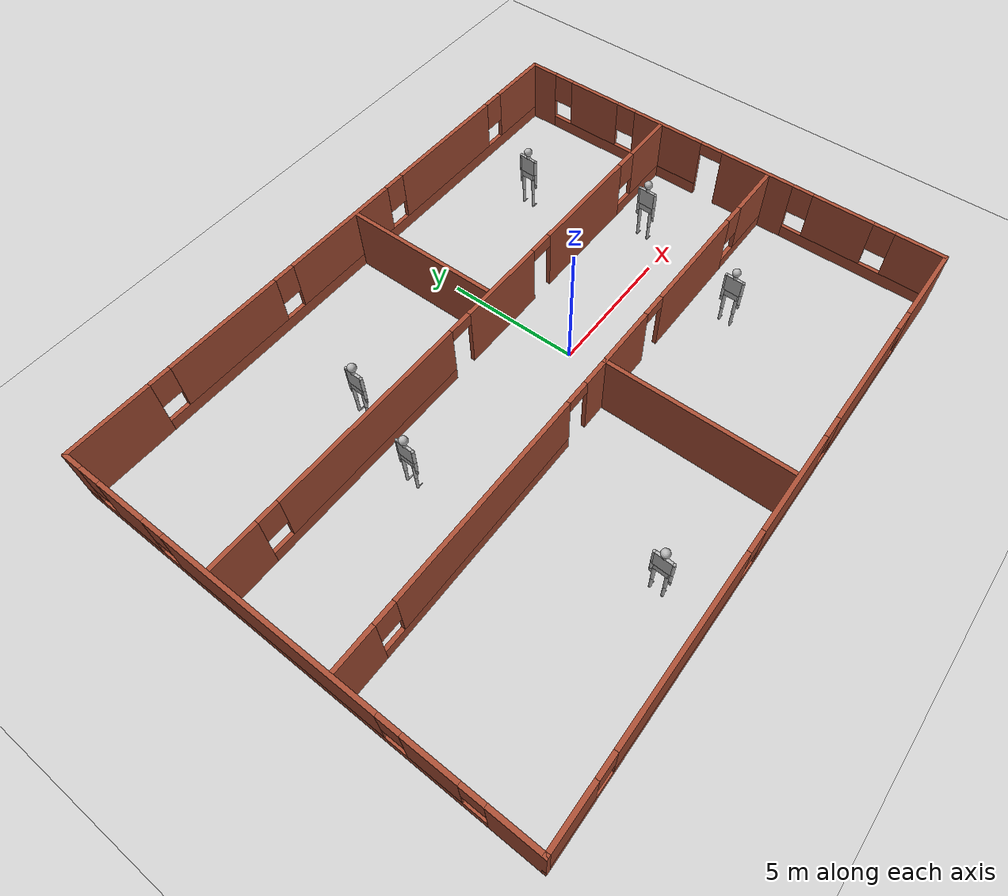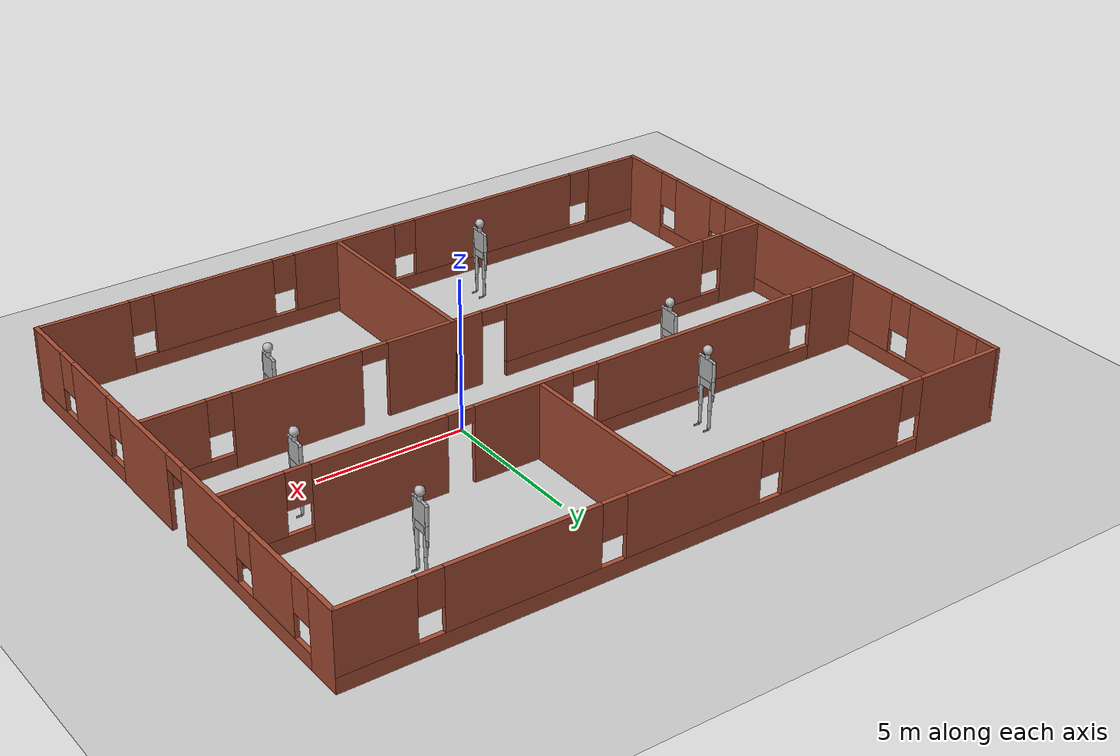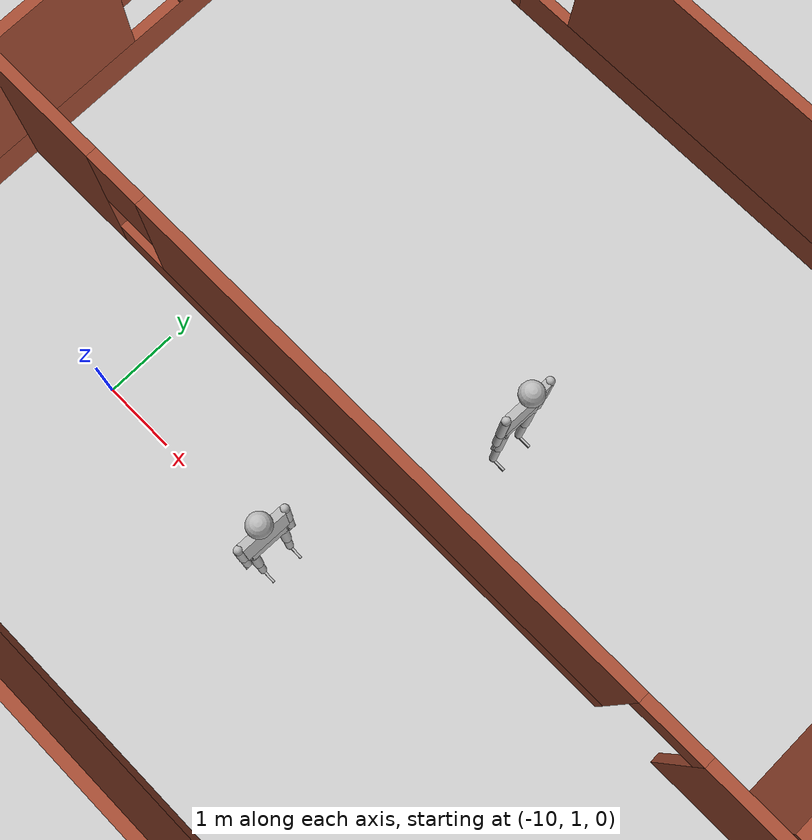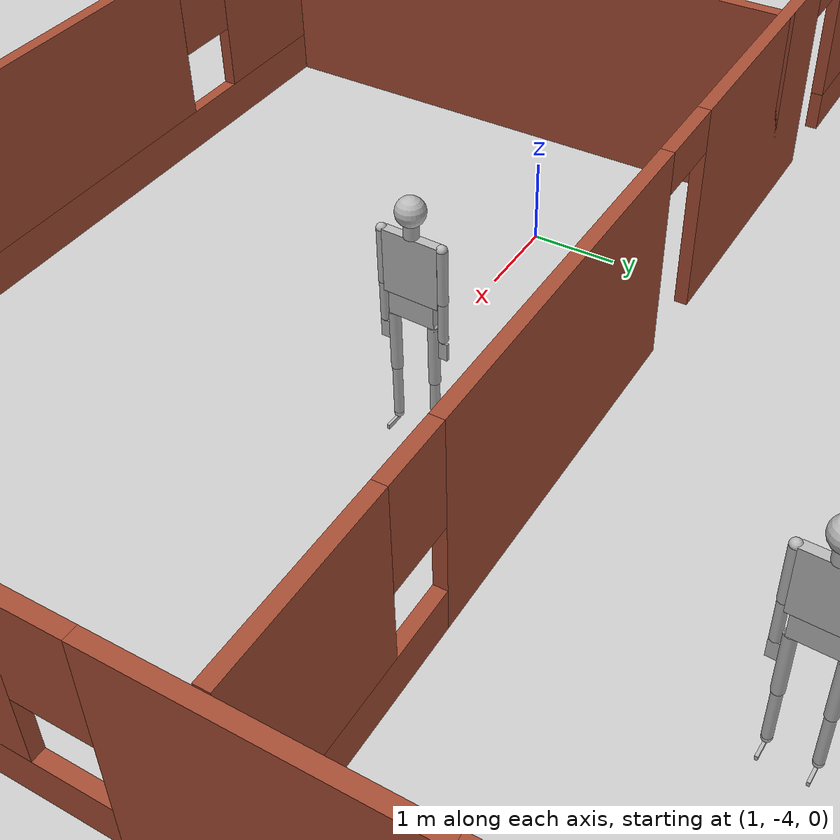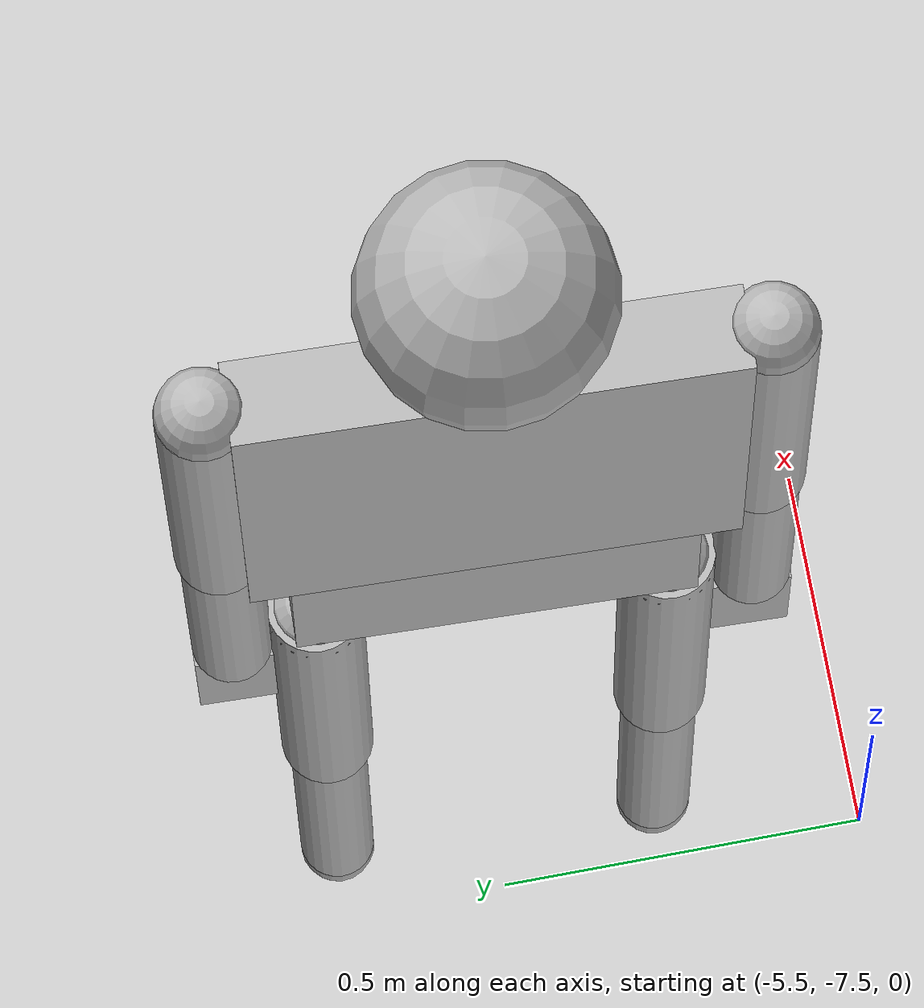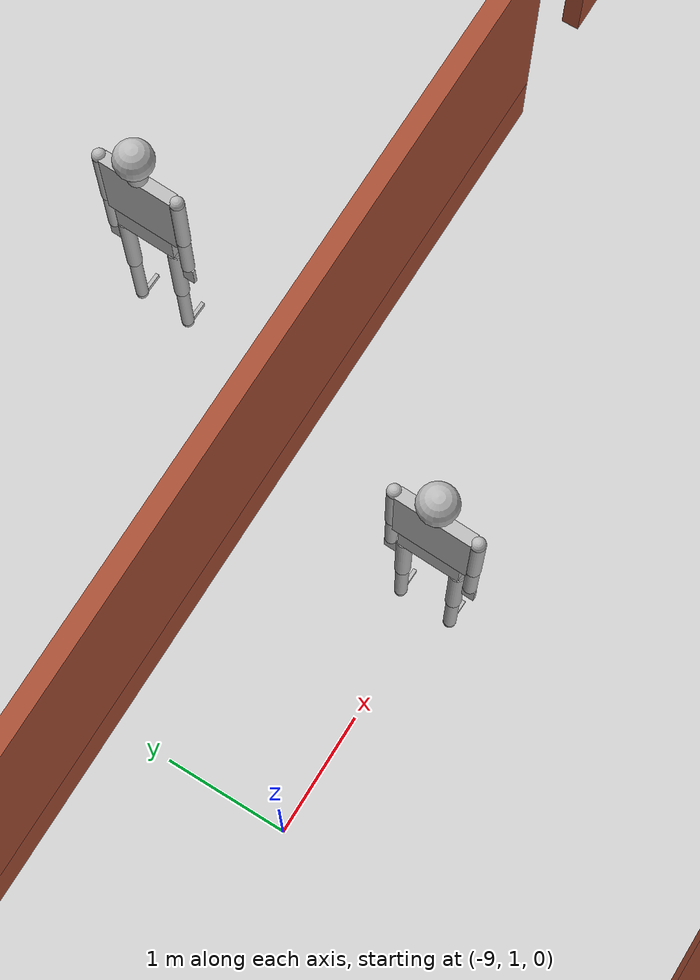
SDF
<sdf version="1.6">
 <world name="default">
  <light name="sun" type="directional">
   <pose>0 0 10 0 -0 0</pose>
   <diffuse>0.8 0.8 0.8 1</diffuse>
   <specular>0.2 0.2 0.2 1</specular>
   <attenuation>
    <range>1000</range>
    <constant>0.9</constant>
    <linear>0.01</linear>
    <quadratic>0.001</quadratic>
   </attenuation>
   <direction>-0.5 0.1 -0.9</direction>
  </light>
  <model name="ground_plane">
   <static>1</static>
   <link name="link">
    <collision name="collision">
     <geometry><plane><normal>0 0 1</normal><size>100 100</size></plane></geometry>
     <surface><friction><ode><mu>100</mu><mu2>50</mu2></ode></friction></surface>
    </collision>
    <visual name="visual">
     <cast_shadows>0</cast_shadows>
     <geometry><plane><normal>0 0 1</normal><size>100 100</size></plane></geometry>
     <material>
      <script><uri>file://media/materials/scripts/gazebo.material</uri><name>Gazebo/Grey</name></script>
     </material>
    </visual>
   </link>
  </model>
  <gravity>0 0 -9.8</gravity>
  <magnetic_field>6e-06 2.3e-05 -4.2e-05</magnetic_field>
  <atmosphere type="adiabatic"/>
  <physics name="default_physics" default="0" type="ode">
   <max_step_size>0.001</max_step_size>
   <real_time_factor>1</real_time_factor>
   <real_time_update_rate>1000</real_time_update_rate>
  </physics>
  <scene><ambient>0.4 0.4 0.4 1</ambient><background>0.7 0.7 0.7 1</background><shadows>1</shadows></scene>
  <spherical_coordinates>
   <surface_model>EARTH_WGS84</surface_model>
   <latitude_deg>0</latitude_deg>
   <longitude_deg>0</longitude_deg>
   <elevation>0</elevation>
   <heading_deg>0</heading_deg>
  </spherical_coordinates>
  <model name="HOTEL_SK">
   <pose>-1.88313 -0.090722 0 0 -0 0</pose>
   <link name="Wall_10">
    <pose>-0.035498 -1.92449 0 0 -0 0</pose>
    <visual name="Wall_10_Visual_0">
     <pose>-10.4451 0 1.25 0 -0 0</pose>
     <geometry><box><size>1.60983 0.15 2.5</size></box></geometry>
     <material>
      <script><uri>file://media/materials/scripts/gazebo.material</uri><name>Gazebo/Bricks</name></script>
      <ambient>1 1 1 1</ambient>
     </material>
    </visual>
    <collision name="Wall_10_Collision_0">
     <geometry><box><size>1.60983 0.15 2.5</size></box></geometry>
     <pose>-10.4451 0 1.25 0 -0 0</pose>
    </collision>
    <visual name="Wall_10_Visual_1">
     <pose>1.53547 0 1.25 0 -0 0</pose>
     <geometry><box><size>3.36994 0.15 2.5</size></box></geometry>
     <material>
      <script><uri>file://media/materials/scripts/gazebo.material</uri><name>Gazebo/Bricks</name></script>
      <ambient>1 1 1 1</ambient>
     </material>
    </visual>
    <collision name="Wall_10_Collision_1">
     <geometry><box><size>3.36994 0.15 2.5</size></box></geometry>
     <pose>1.53547 0 1.25 0 -0 0</pose>
    </collision>
    <visual name="Wall_10_Visual_2">
     <pose>6.26349 0 1.25 0 -0 0</pose>
     <geometry><box><size>4.2861 0.15 2.5</size></box></geometry>
     <material>
      <script><uri>file://media/materials/scripts/gazebo.material</uri><name>Gazebo/Bricks</name></script>
      <ambient>1 1 1 1</ambient>
     </material>
    </visual>
    <collision name="Wall_10_Collision_2">
     <geometry><box><size>4.2861 0.15 2.5</size></box></geometry>
     <pose>6.26349 0 1.25 0 -0 0</pose>
    </collision>
    <visual name="Wall_10_Visual_3">
     <pose>-5.34484 0 0.25 0 -0 0</pose>
     <geometry><box><size>8.59066 0.15 0.5</size></box></geometry>
     <material>
      <script><uri>file://media/materials/scripts/gazebo.material</uri><name>Gazebo/Bricks</name></script>
      <ambient>1 1 1 1</ambient>
     </material>
    </visual>
    <collision name="Wall_10_Collision_3">
     <geometry><box><size>8.59066 0.15 0.5</size></box></geometry>
     <pose>-5.34484 0 0.25 0 -0 0</pose>
    </collision>
    <visual name="Wall_10_Visual_4">
     <pose>9.82827 0 0.25 0 -0 0</pose>
     <geometry><box><size>2.84346 0.15 0.5</size></box></geometry>
     <material>
      <script><uri>file://media/materials/scripts/gazebo.material</uri><name>Gazebo/Bricks</name></script>
      <ambient>1 1 1 1</ambient>
     </material>
    </visual>
    <collision name="Wall_10_Collision_4">
     <geometry><box><size>2.84346 0.15 0.5</size></box></geometry>
     <pose>9.82827 0 0.25 0 -0 0</pose>
    </collision>
    <visual name="Wall_10_Visual_5">
     <pose>-4.94484 0 1.5 0 -0 0</pose>
     <geometry><box><size>7.79066 0.15 2</size></box></geometry>
     <material>
      <script><uri>file://media/materials/scripts/gazebo.material</uri><name>Gazebo/Bricks</name></script>
      <ambient>1 1 1 1</ambient>
     </material>
    </visual>
    <collision name="Wall_10_Collision_5">
     <geometry><box><size>7.79066 0.15 2</size></box></geometry>
     <pose>-4.94484 0 1.5 0 -0 0</pose>
    </collision>
    <visual name="Wall_10_Visual_6">
     <pose>-4.94484 0 1.5 0 -0 0</pose>
     <geometry><box><size>7.79066 0.15 2</size></box></geometry>
     <material>
      <script><uri>file://media/materials/scripts/gazebo.material</uri><name>Gazebo/Bricks</name></script>
      <ambient>1 1 1 1</ambient>
     </material>
    </visual>
    <collision name="Wall_10_Collision_6">
     <geometry><box><size>7.79066 0.15 2</size></box></geometry>
     <pose>-4.94484 0 1.5 0 -0 0</pose>
    </collision>
    <visual name="Wall_10_Visual_7">
     <pose>10.2283 0 1.5 0 -0 0</pose>
     <geometry><box><size>2.04346 0.15 2</size></box></geometry>
     <material>
      <script><uri>file://media/materials/scripts/gazebo.material</uri><name>Gazebo/Bricks</name></script>
      <ambient>1 1 1 1</ambient>
     </material>
    </visual>
    <collision name="Wall_10_Collision_7">
     <geometry><box><size>2.04346 0.15 2</size></box></geometry>
     <pose>10.2283 0 1.5 0 -0 0</pose>
    </collision>
    <visual name="Wall_10_Visual_8">
     <pose>-9.24017 0 1.9 0 -0 0</pose>
     <geometry><box><size>0.8 0.15 1.2</size></box></geometry>
     <material>
      <script><uri>file://media/materials/scripts/gazebo.material</uri><name>Gazebo/Bricks</name></script>
      <ambient>1 1 1 1</ambient>
     </material>
    </visual>
    <collision name="Wall_10_Collision_8">
     <geometry><box><size>0.8 0.15 1.2</size></box></geometry>
     <pose>-9.24017 0 1.9 0 -0 0</pose>
    </collision>
    <visual name="Wall_10_Visual_9">
     <pose>8.80654 0 1.9 0 -0 0</pose>
     <geometry><box><size>0.8 0.15 1.2</size></box></geometry>
     <material>
      <script><uri>file://media/materials/scripts/gazebo.material</uri><name>Gazebo/Bricks</name></script>
      <ambient>1 1 1 1</ambient>
     </material>
    </visual>
    <collision name="Wall_10_Collision_9">
     <geometry><box><size>0.8 0.15 1.2</size></box></geometry>
     <pose>8.80654 0 1.9 0 -0 0</pose>
    </collision>
    <visual name="Wall_10_Visual_10">
     <pose>3.67044 0 2.25 0 -0 0</pose>
     <geometry><box><size>0.9 0.15 0.5</size></box></geometry>
     <material>
      <script><uri>file://media/materials/scripts/gazebo.material</uri><name>Gazebo/Bricks</name></script>
      <ambient>1 1 1 1</ambient>
     </material>
    </visual>
    <collision name="Wall_10_Collision_10">
     <geometry><box><size>0.9 0.15 0.5</size></box></geometry>
     <pose>3.67044 0 2.25 0 -0 0</pose>
    </collision>
    <visual name="Wall_10_Visual_11">
     <pose>-0.599507 0 2.25 0 -0 0</pose>
     <geometry><box><size>0.9 0.15 0.5</size></box></geometry>
     <material>
      <script><uri>file://media/materials/scripts/gazebo.material</uri><name>Gazebo/Bricks</name></script>
      <ambient>1 1 1 1</ambient>
     </material>
    </visual>
    <collision name="Wall_10_Collision_11">
     <geometry><box><size>0.9 0.15 0.5</size></box></geometry>
     <pose>-0.599507 0 2.25 0 -0 0</pose>
    </collision>
    <visual name="Wall_10_Visual_12">
     <pose>-0.599507 0 2.25 0 -0 0</pose>
     <geometry><box><size>0.9 0.15 0.5</size></box></geometry>
     <material>
      <script><uri>file://media/materials/scripts/gazebo.material</uri><name>Gazebo/Bricks</name></script>
      <ambient>1 1 1 1</ambient>
     </material>
    </visual>
    <collision name="Wall_10_Collision_12">
     <geometry><box><size>0.9 0.15 0.5</size></box></geometry>
     <pose>-0.599507 0 2.25 0 -0 0</pose>
    </collision>
   </link>
   <link name="Wall_12">
    <collision name="Wall_12_Collision">
     <geometry><box><size>6 0.15 2.5</size></box></geometry>
     <pose>0 0 1.25 0 -0 0</pose>
    </collision>
    <visual name="Wall_12_Visual">
     <pose>0 0 1.25 0 -0 0</pose>
     <geometry><box><size>6 0.15 2.5</size></box></geometry>
     <material>
      <script><uri>file://media/materials/scripts/gazebo.material</uri><name>Gazebo/Bricks</name></script>
      <ambient>1 1 1 1</ambient>
     </material>
    </visual>
    <pose>0.890996 5.73932 0 0 0 -1.5708</pose>
   </link>
   <link name="Wall_14">
    <collision name="Wall_14_Collision">
     <geometry><box><size>6.75 0.15 2.5</size></box></geometry>
     <pose>0 0 1.25 0 -0 0</pose>
    </collision>
    <visual name="Wall_14_Visual">
     <pose>0 0 1.25 0 -0 0</pose>
     <geometry><box><size>6.75 0.15 2.5</size></box></geometry>
     <material>
      <script><uri>file://media/materials/scripts/gazebo.material</uri><name>Gazebo/Bricks</name></script>
      <ambient>1 1 1 1</ambient>
     </material>
    </visual>
    <pose>0.855817 -5.22449 0 0 0 -1.5708</pose>
   </link>
   <link name="Wall_2">
    <pose>11.3 0 0 0 0 -1.5708</pose>
    <visual name="Wall_2_Visual_0">
     <pose>-8.1684 0 1.25 0 -0 0</pose>
     <geometry><box><size>1.16319 0.15 2.5</size></box></geometry>
     <material>
      <script><uri>file://media/materials/scripts/gazebo.material</uri><name>Gazebo/Bricks</name></script>
      <ambient>1 1 1 1</ambient>
     </material>
    </visual>
    <collision name="Wall_2_Collision_0">
     <geometry><box><size>1.16319 0.15 2.5</size></box></geometry>
     <pose>-8.1684 0 1.25 0 -0 0</pose>
    </collision>
    <visual name="Wall_2_Visual_1">
     <pose>1.47458 0 1.25 0 -0 0</pose>
     <geometry><box><size>2.91413 0.15 2.5</size></box></geometry>
     <material>
      <script><uri>file://media/materials/scripts/gazebo.material</uri><name>Gazebo/Bricks</name></script>
      <ambient>1 1 1 1</ambient>
     </material>
    </visual>
    <collision name="Wall_2_Collision_1">
     <geometry><box><size>2.91413 0.15 2.5</size></box></geometry>
     <pose>1.47458 0 1.25 0 -0 0</pose>
    </collision>
    <visual name="Wall_2_Visual_2">
     <pose>-4.23465 0 0.25 0 -0 0</pose>
     <geometry><box><size>6.70432 0.15 0.5</size></box></geometry>
     <material>
      <script><uri>file://media/materials/scripts/gazebo.material</uri><name>Gazebo/Bricks</name></script>
      <ambient>1 1 1 1</ambient>
     </material>
    </visual>
    <collision name="Wall_2_Collision_2">
     <geometry><box><size>6.70432 0.15 0.5</size></box></geometry>
     <pose>-4.23465 0 0.25 0 -0 0</pose>
    </collision>
    <visual name="Wall_2_Visual_3">
     <pose>5.84082 0 0.25 0 -0 0</pose>
     <geometry><box><size>5.81836 0.15 0.5</size></box></geometry>
     <material>
      <script><uri>file://media/materials/scripts/gazebo.material</uri><name>Gazebo/Bricks</name></script>
      <ambient>1 1 1 1</ambient>
     </material>
    </visual>
    <collision name="Wall_2_Collision_3">
     <geometry><box><size>5.81836 0.15 0.5</size></box></geometry>
     <pose>5.84082 0 0.25 0 -0 0</pose>
    </collision>
    <visual name="Wall_2_Visual_4">
     <pose>-5.7093 0 1.5 0 -0 0</pose>
     <geometry><box><size>2.15502 0.15 2</size></box></geometry>
     <material>
      <script><uri>file://media/materials/scripts/gazebo.material</uri><name>Gazebo/Bricks</name></script>
      <ambient>1 1 1 1</ambient>
     </material>
    </visual>
    <collision name="Wall_2_Collision_4">
     <geometry><box><size>2.15502 0.15 2</size></box></geometry>
     <pose>-5.7093 0 1.5 0 -0 0</pose>
    </collision>
    <visual name="Wall_2_Visual_5">
     <pose>-2.35714 0 1.5 0 -0 0</pose>
     <geometry><box><size>2.94931 0.15 2</size></box></geometry>
     <material>
      <script><uri>file://media/materials/scripts/gazebo.material</uri><name>Gazebo/Bricks</name></script>
      <ambient>1 1 1 1</ambient>
     </material>
    </visual>
    <collision name="Wall_2_Collision_5">
     <geometry><box><size>2.94931 0.15 2</size></box></geometry>
     <pose>-2.35714 0 1.5 0 -0 0</pose>
    </collision>
    <visual name="Wall_2_Visual_6">
     <pose>-2.35714 0 1.5 0 -0 0</pose>
     <geometry><box><size>2.94931 0.15 2</size></box></geometry>
     <material>
      <script><uri>file://media/materials/scripts/gazebo.material</uri><name>Gazebo/Bricks</name></script>
      <ambient>1 1 1 1</ambient>
     </material>
    </visual>
    <collision name="Wall_2_Collision_6">
     <geometry><box><size>2.94931 0.15 2</size></box></geometry>
     <pose>-2.35714 0 1.5 0 -0 0</pose>
    </collision>
    <visual name="Wall_2_Visual_7">
     <pose>4.8971 0 1.5 0 -0 0</pose>
     <geometry><box><size>2.33091 0.15 2</size></box></geometry>
     <material>
      <script><uri>file://media/materials/scripts/gazebo.material</uri><name>Gazebo/Bricks</name></script>
      <ambient>1 1 1 1</ambient>
     </material>
    </visual>
    <collision name="Wall_2_Collision_7">
     <geometry><box><size>2.33091 0.15 2</size></box></geometry>
     <pose>4.8971 0 1.5 0 -0 0</pose>
    </collision>
    <visual name="Wall_2_Visual_8">
     <pose>7.80628 0 1.5 0 -0 0</pose>
     <geometry><box><size>1.88745 0.15 2</size></box></geometry>
     <material>
      <script><uri>file://media/materials/scripts/gazebo.material</uri><name>Gazebo/Bricks</name></script>
      <ambient>1 1 1 1</ambient>
     </material>
    </visual>
    <collision name="Wall_2_Collision_8">
     <geometry><box><size>1.88745 0.15 2</size></box></geometry>
     <pose>7.80628 0 1.5 0 -0 0</pose>
    </collision>
    <visual name="Wall_2_Visual_9">
     <pose>-7.18681 0 1.9 0 -0 0</pose>
     <geometry><box><size>0.8 0.15 1.2</size></box></geometry>
     <material>
      <script><uri>file://media/materials/scripts/gazebo.material</uri><name>Gazebo/Bricks</name></script>
      <ambient>1 1 1 1</ambient>
     </material>
    </visual>
    <collision name="Wall_2_Collision_9">
     <geometry><box><size>0.8 0.15 1.2</size></box></geometry>
     <pose>-7.18681 0 1.9 0 -0 0</pose>
    </collision>
    <visual name="Wall_2_Visual_10">
     <pose>3.33164 0 1.9 0 -0 0</pose>
     <geometry><box><size>0.8 0.15 1.2</size></box></geometry>
     <material>
      <script><uri>file://media/materials/scripts/gazebo.material</uri><name>Gazebo/Bricks</name></script>
      <ambient>1 1 1 1</ambient>
     </material>
    </visual>
    <collision name="Wall_2_Collision_10">
     <geometry><box><size>0.8 0.15 1.2</size></box></geometry>
     <pose>3.33164 0 1.9 0 -0 0</pose>
    </collision>
    <visual name="Wall_2_Visual_11">
     <pose>-4.23179 0 1.9 0 -0 0</pose>
     <geometry><box><size>0.8 0.15 1.2</size></box></geometry>
     <material>
      <script><uri>file://media/materials/scripts/gazebo.material</uri><name>Gazebo/Bricks</name></script>
      <ambient>1 1 1 1</ambient>
     </material>
    </visual>
    <collision name="Wall_2_Collision_11">
     <geometry><box><size>0.8 0.15 1.2</size></box></geometry>
     <pose>-4.23179 0 1.9 0 -0 0</pose>
    </collision>
    <visual name="Wall_2_Visual_12">
     <pose>6.46255 0 1.9 0 -0 0</pose>
     <geometry><box><size>0.8 0.15 1.2</size></box></geometry>
     <material>
      <script><uri>file://media/materials/scripts/gazebo.material</uri><name>Gazebo/Bricks</name></script>
      <ambient>1 1 1 1</ambient>
     </material>
    </visual>
    <collision name="Wall_2_Collision_12">
     <geometry><box><size>0.8 0.15 1.2</size></box></geometry>
     <pose>6.46255 0 1.9 0 -0 0</pose>
    </collision>
    <visual name="Wall_2_Visual_13">
     <pose>-0.432485 0 2.25 0 -0 0</pose>
     <geometry><box><size>0.9 0.15 0.5</size></box></geometry>
     <material>
      <script><uri>file://media/materials/scripts/gazebo.material</uri><name>Gazebo/Bricks</name></script>
      <ambient>1 1 1 1</ambient>
     </material>
    </visual>
    <collision name="Wall_2_Collision_13">
     <geometry><box><size>0.9 0.15 0.5</size></box></geometry>
     <pose>-0.432485 0 2.25 0 -0 0</pose>
    </collision>
    <visual name="Wall_2_Visual_14">
     <pose>-0.432485 0 2.25 0 -0 0</pose>
     <geometry><box><size>0.9 0.15 0.5</size></box></geometry>
     <material>
      <script><uri>file://media/materials/scripts/gazebo.material</uri><name>Gazebo/Bricks</name></script>
      <ambient>1 1 1 1</ambient>
     </material>
    </visual>
    <collision name="Wall_2_Collision_14">
     <geometry><box><size>0.9 0.15 0.5</size></box></geometry>
     <pose>-0.432485 0 2.25 0 -0 0</pose>
    </collision>
   </link>
   <link name="Wall_3">
    <pose>0 -8.675 0 0 -0 3.14159</pose>
    <visual name="Wall_3_Visual_0">
     <pose>-9.83329 0 1.25 0 -0 0</pose>
     <geometry><box><size>3.08343 0.15 2.5</size></box></geometry>
     <material>
      <script><uri>file://media/materials/scripts/gazebo.material</uri><name>Gazebo/Bricks</name></script>
      <ambient>1 1 1 1</ambient>
     </material>
    </visual>
    <collision name="Wall_3_Collision_0">
     <geometry><box><size>3.08343 0.15 2.5</size></box></geometry>
     <pose>-9.83329 0 1.25 0 -0 0</pose>
    </collision>
    <visual name="Wall_3_Visual_1">
     <pose>1.54171 0 0.25 0 -0 0</pose>
     <geometry><box><size>19.6666 0.15 0.5</size></box></geometry>
     <material>
      <script><uri>file://media/materials/scripts/gazebo.material</uri><name>Gazebo/Bricks</name></script>
      <ambient>1 1 1 1</ambient>
     </material>
    </visual>
    <collision name="Wall_3_Collision_1">
     <geometry><box><size>19.6666 0.15 0.5</size></box></geometry>
     <pose>1.54171 0 0.25 0 -0 0</pose>
    </collision>
    <visual name="Wall_3_Visual_2">
     <pose>-5.39388 0 1.5 0 -0 0</pose>
     <geometry><box><size>4.19538 0.15 2</size></box></geometry>
     <material>
      <script><uri>file://media/materials/scripts/gazebo.material</uri><name>Gazebo/Bricks</name></script>
      <ambient>1 1 1 1</ambient>
     </material>
    </visual>
    <collision name="Wall_3_Collision_2">
     <geometry><box><size>4.19538 0.15 2</size></box></geometry>
     <pose>-5.39388 0 1.5 0 -0 0</pose>
    </collision>
    <visual name="Wall_3_Visual_3">
     <pose>-0.609566 0 1.5 0 -0 0</pose>
     <geometry><box><size>3.77324 0.15 2</size></box></geometry>
     <material>
      <script><uri>file://media/materials/scripts/gazebo.material</uri><name>Gazebo/Bricks</name></script>
      <ambient>1 1 1 1</ambient>
     </material>
    </visual>
    <collision name="Wall_3_Collision_3">
     <geometry><box><size>3.77324 0.15 2</size></box></geometry>
     <pose>-0.609566 0 1.5 0 -0 0</pose>
    </collision>
    <visual name="Wall_3_Visual_4">
     <pose>5.28288 0 1.5 0 -0 0</pose>
     <geometry><box><size>6.41165 0.15 2</size></box></geometry>
     <material>
      <script><uri>file://media/materials/scripts/gazebo.material</uri><name>Gazebo/Bricks</name></script>
      <ambient>1 1 1 1</ambient>
     </material>
    </visual>
    <collision name="Wall_3_Collision_4">
     <geometry><box><size>6.41165 0.15 2</size></box></geometry>
     <pose>5.28288 0 1.5 0 -0 0</pose>
    </collision>
    <visual name="Wall_3_Visual_5">
     <pose>10.3318 0 1.5 0 -0 0</pose>
     <geometry><box><size>2.0863 0.15 2</size></box></geometry>
     <material>
      <script><uri>file://media/materials/scripts/gazebo.material</uri><name>Gazebo/Bricks</name></script>
      <ambient>1 1 1 1</ambient>
     </material>
    </visual>
    <collision name="Wall_3_Collision_5">
     <geometry><box><size>2.0863 0.15 2</size></box></geometry>
     <pose>10.3318 0 1.5 0 -0 0</pose>
    </collision>
    <visual name="Wall_3_Visual_6">
     <pose>-7.89157 0 1.9 0 -0 0</pose>
     <geometry><box><size>0.8 0.15 1.2</size></box></geometry>
     <material>
      <script><uri>file://media/materials/scripts/gazebo.material</uri><name>Gazebo/Bricks</name></script>
      <ambient>1 1 1 1</ambient>
     </material>
    </visual>
    <collision name="Wall_3_Collision_6">
     <geometry><box><size>0.8 0.15 1.2</size></box></geometry>
     <pose>-7.89157 0 1.9 0 -0 0</pose>
    </collision>
    <visual name="Wall_3_Visual_7">
     <pose>-2.89619 0 1.9 0 -0 0</pose>
     <geometry><box><size>0.8 0.15 1.2</size></box></geometry>
     <material>
      <script><uri>file://media/materials/scripts/gazebo.material</uri><name>Gazebo/Bricks</name></script>
      <ambient>1 1 1 1</ambient>
     </material>
    </visual>
    <collision name="Wall_3_Collision_7">
     <geometry><box><size>0.8 0.15 1.2</size></box></geometry>
     <pose>-2.89619 0 1.9 0 -0 0</pose>
    </collision>
    <visual name="Wall_3_Visual_8">
     <pose>1.67705 0 1.9 0 -0 0</pose>
     <geometry><box><size>0.8 0.15 1.2</size></box></geometry>
     <material>
      <script><uri>file://media/materials/scripts/gazebo.material</uri><name>Gazebo/Bricks</name></script>
      <ambient>1 1 1 1</ambient>
     </material>
    </visual>
    <collision name="Wall_3_Collision_8">
     <geometry><box><size>0.8 0.15 1.2</size></box></geometry>
     <pose>1.67705 0 1.9 0 -0 0</pose>
    </collision>
    <visual name="Wall_3_Visual_9">
     <pose>8.8887 0 1.9 0 -0 0</pose>
     <geometry><box><size>0.8 0.15 1.2</size></box></geometry>
     <material>
      <script><uri>file://media/materials/scripts/gazebo.material</uri><name>Gazebo/Bricks</name></script>
      <ambient>1 1 1 1</ambient>
     </material>
    </visual>
    <collision name="Wall_3_Collision_9">
     <geometry><box><size>0.8 0.15 1.2</size></box></geometry>
     <pose>8.8887 0 1.9 0 -0 0</pose>
    </collision>
   </link>
   <link name="Wall_4">
    <pose>-11.3 0 0 0 -0 1.5708</pose>
    <visual name="Wall_4_Visual_0">
     <pose>-7.84145 0 1.25 0 -0 0</pose>
     <geometry><box><size>1.81709 0.15 2.5</size></box></geometry>
     <material>
      <script><uri>file://media/materials/scripts/gazebo.material</uri><name>Gazebo/Bricks</name></script>
      <ambient>1 1 1 1</ambient>
     </material>
    </visual>
    <collision name="Wall_4_Collision_0">
     <geometry><box><size>1.81709 0.15 2.5</size></box></geometry>
     <pose>-7.84145 0 1.25 0 -0 0</pose>
    </collision>
    <visual name="Wall_4_Visual_1">
     <pose>0.908545 0 0.25 0 -0 0</pose>
     <geometry><box><size>15.6829 0.15 0.5</size></box></geometry>
     <material>
      <script><uri>file://media/materials/scripts/gazebo.material</uri><name>Gazebo/Bricks</name></script>
      <ambient>1 1 1 1</ambient>
     </material>
    </visual>
    <collision name="Wall_4_Collision_1">
     <geometry><box><size>15.6829 0.15 0.5</size></box></geometry>
     <pose>0.908545 0 0.25 0 -0 0</pose>
    </collision>
    <visual name="Wall_4_Visual_2">
     <pose>-5.21371 0 1.5 0 -0 0</pose>
     <geometry><box><size>1.83841 0.15 2</size></box></geometry>
     <material>
      <script><uri>file://media/materials/scripts/gazebo.material</uri><name>Gazebo/Bricks</name></script>
      <ambient>1 1 1 1</ambient>
     </material>
    </visual>
    <collision name="Wall_4_Collision_2">
     <geometry><box><size>1.83841 0.15 2</size></box></geometry>
     <pose>-5.21371 0 1.5 0 -0 0</pose>
    </collision>
    <visual name="Wall_4_Visual_3">
     <pose>0.467664 0 1.5 0 -0 0</pose>
     <geometry><box><size>7.92433 0.15 2</size></box></geometry>
     <material>
      <script><uri>file://media/materials/scripts/gazebo.material</uri><name>Gazebo/Bricks</name></script>
      <ambient>1 1 1 1</ambient>
     </material>
    </visual>
    <collision name="Wall_4_Collision_3">
     <geometry><box><size>7.92433 0.15 2</size></box></geometry>
     <pose>0.467664 0 1.5 0 -0 0</pose>
    </collision>
    <visual name="Wall_4_Visual_4">
     <pose>6.2018 0 1.5 0 -0 0</pose>
     <geometry><box><size>1.94394 0.15 2</size></box></geometry>
     <material>
      <script><uri>file://media/materials/scripts/gazebo.material</uri><name>Gazebo/Bricks</name></script>
      <ambient>1 1 1 1</ambient>
     </material>
    </visual>
    <collision name="Wall_4_Collision_4">
     <geometry><box><size>1.94394 0.15 2</size></box></geometry>
     <pose>6.2018 0 1.5 0 -0 0</pose>
    </collision>
    <visual name="Wall_4_Visual_5">
     <pose>8.36189 0 1.5 0 -0 0</pose>
     <geometry><box><size>0.776226 0.15 2</size></box></geometry>
     <material>
      <script><uri>file://media/materials/scripts/gazebo.material</uri><name>Gazebo/Bricks</name></script>
      <ambient>1 1 1 1</ambient>
     </material>
    </visual>
    <collision name="Wall_4_Collision_5">
     <geometry><box><size>0.776226 0.15 2</size></box></geometry>
     <pose>8.36189 0 1.5 0 -0 0</pose>
    </collision>
    <visual name="Wall_4_Visual_6">
     <pose>-6.53291 0 1.9 0 -0 0</pose>
     <geometry><box><size>0.8 0.15 1.2</size></box></geometry>
     <material>
      <script><uri>file://media/materials/scripts/gazebo.material</uri><name>Gazebo/Bricks</name></script>
      <ambient>1 1 1 1</ambient>
     </material>
    </visual>
    <collision name="Wall_4_Collision_6">
     <geometry><box><size>0.8 0.15 1.2</size></box></geometry>
     <pose>-6.53291 0 1.9 0 -0 0</pose>
    </collision>
    <visual name="Wall_4_Visual_7">
     <pose>-3.8945 0 1.9 0 -0 0</pose>
     <geometry><box><size>0.8 0.15 1.2</size></box></geometry>
     <material>
      <script><uri>file://media/materials/scripts/gazebo.material</uri><name>Gazebo/Bricks</name></script>
      <ambient>1 1 1 1</ambient>
     </material>
    </visual>
    <collision name="Wall_4_Collision_7">
     <geometry><box><size>0.8 0.15 1.2</size></box></geometry>
     <pose>-3.8945 0 1.9 0 -0 0</pose>
    </collision>
    <visual name="Wall_4_Visual_8">
     <pose>4.82983 0 1.9 0 -0 0</pose>
     <geometry><box><size>0.8 0.15 1.2</size></box></geometry>
     <material>
      <script><uri>file://media/materials/scripts/gazebo.material</uri><name>Gazebo/Bricks</name></script>
      <ambient>1 1 1 1</ambient>
     </material>
    </visual>
    <collision name="Wall_4_Collision_8">
     <geometry><box><size>0.8 0.15 1.2</size></box></geometry>
     <pose>4.82983 0 1.9 0 -0 0</pose>
    </collision>
    <visual name="Wall_4_Visual_9">
     <pose>7.57377 0 1.9 0 -0 0</pose>
     <geometry><box><size>0.8 0.15 1.2</size></box></geometry>
     <material>
      <script><uri>file://media/materials/scripts/gazebo.material</uri><name>Gazebo/Bricks</name></script>
      <ambient>1 1 1 1</ambient>
     </material>
    </visual>
    <collision name="Wall_4_Collision_9">
     <geometry><box><size>0.8 0.15 1.2</size></box></geometry>
     <pose>7.57377 0 1.9 0 -0 0</pose>
    </collision>
   </link>
   <link name="Wall_6">
    <pose>0 8.675 0 0 -0 0</pose>
    <visual name="Wall_6_Visual_0">
     <pose>-9.80417 0 1.25 0 -0 0</pose>
     <geometry><box><size>3.14166 0.15 2.5</size></box></geometry>
     <material>
      <script><uri>file://media/materials/scripts/gazebo.material</uri><name>Gazebo/Bricks</name></script>
      <ambient>1 1 1 1</ambient>
     </material>
    </visual>
    <collision name="Wall_6_Collision_0">
     <geometry><box><size>3.14166 0.15 2.5</size></box></geometry>
     <pose>-9.80417 0 1.25 0 -0 0</pose>
    </collision>
    <visual name="Wall_6_Visual_1">
     <pose>1.57083 0 0.25 0 -0 0</pose>
     <geometry><box><size>19.6083 0.15 0.5</size></box></geometry>
     <material>
      <script><uri>file://media/materials/scripts/gazebo.material</uri><name>Gazebo/Bricks</name></script>
      <ambient>1 1 1 1</ambient>
     </material>
    </visual>
    <collision name="Wall_6_Collision_1">
     <geometry><box><size>19.6083 0.15 0.5</size></box></geometry>
     <pose>1.57083 0 0.25 0 -0 0</pose>
    </collision>
    <visual name="Wall_6_Visual_2">
     <pose>-5.21252 0 1.5 0 -0 0</pose>
     <geometry><box><size>4.44163 0.15 2</size></box></geometry>
     <material>
      <script><uri>file://media/materials/scripts/gazebo.material</uri><name>Gazebo/Bricks</name></script>
      <ambient>1 1 1 1</ambient>
     </material>
    </visual>
    <collision name="Wall_6_Collision_2">
     <geometry><box><size>4.44163 0.15 2</size></box></geometry>
     <pose>-5.21252 0 1.5 0 -0 0</pose>
    </collision>
    <visual name="Wall_6_Visual_3">
     <pose>0.134653 0 1.5 0 -0 0</pose>
     <geometry><box><size>4.65271 0.15 2</size></box></geometry>
     <material>
      <script><uri>file://media/materials/scripts/gazebo.material</uri><name>Gazebo/Bricks</name></script>
      <ambient>1 1 1 1</ambient>
     </material>
    </visual>
    <collision name="Wall_6_Collision_3">
     <geometry><box><size>4.65271 0.15 2</size></box></geometry>
     <pose>0.134653 0 1.5 0 -0 0</pose>
    </collision>
    <visual name="Wall_6_Visual_4">
     <pose>5.71049 0 1.5 0 -0 0</pose>
     <geometry><box><size>4.89896 0.15 2</size></box></geometry>
     <material>
      <script><uri>file://media/materials/scripts/gazebo.material</uri><name>Gazebo/Bricks</name></script>
      <ambient>1 1 1 1</ambient>
     </material>
    </visual>
    <collision name="Wall_6_Collision_4">
     <geometry><box><size>4.89896 0.15 2</size></box></geometry>
     <pose>5.71049 0 1.5 0 -0 0</pose>
    </collision>
    <visual name="Wall_6_Visual_5">
     <pose>10.1675 0 1.5 0 -0 0</pose>
     <geometry><box><size>2.41503 0.15 2</size></box></geometry>
     <material>
      <script><uri>file://media/materials/scripts/gazebo.material</uri><name>Gazebo/Bricks</name></script>
      <ambient>1 1 1 1</ambient>
     </material>
    </visual>
    <collision name="Wall_6_Collision_5">
     <geometry><box><size>2.41503 0.15 2</size></box></geometry>
     <pose>10.1675 0 1.5 0 -0 0</pose>
    </collision>
    <visual name="Wall_6_Visual_6">
     <pose>-7.83334 0 1.9 0 -0 0</pose>
     <geometry><box><size>0.8 0.15 1.2</size></box></geometry>
     <material>
      <script><uri>file://media/materials/scripts/gazebo.material</uri><name>Gazebo/Bricks</name></script>
      <ambient>1 1 1 1</ambient>
     </material>
    </visual>
    <collision name="Wall_6_Collision_6">
     <geometry><box><size>0.8 0.15 1.2</size></box></geometry>
     <pose>-7.83334 0 1.9 0 -0 0</pose>
    </collision>
    <visual name="Wall_6_Visual_7">
     <pose>-2.5917 0 1.9 0 -0 0</pose>
     <geometry><box><size>0.8 0.15 1.2</size></box></geometry>
     <material>
      <script><uri>file://media/materials/scripts/gazebo.material</uri><name>Gazebo/Bricks</name></script>
      <ambient>1 1 1 1</ambient>
     </material>
    </visual>
    <collision name="Wall_6_Collision_7">
     <geometry><box><size>0.8 0.15 1.2</size></box></geometry>
     <pose>-2.5917 0 1.9 0 -0 0</pose>
    </collision>
    <visual name="Wall_6_Visual_8">
     <pose>2.86101 0 1.9 0 -0 0</pose>
     <geometry><box><size>0.8 0.15 1.2</size></box></geometry>
     <material>
      <script><uri>file://media/materials/scripts/gazebo.material</uri><name>Gazebo/Bricks</name></script>
      <ambient>1 1 1 1</ambient>
     </material>
    </visual>
    <collision name="Wall_6_Collision_8">
     <geometry><box><size>0.8 0.15 1.2</size></box></geometry>
     <pose>2.86101 0 1.9 0 -0 0</pose>
    </collision>
    <visual name="Wall_6_Visual_9">
     <pose>8.55997 0 1.9 0 -0 0</pose>
     <geometry><box><size>0.8 0.15 1.2</size></box></geometry>
     <material>
      <script><uri>file://media/materials/scripts/gazebo.material</uri><name>Gazebo/Bricks</name></script>
      <ambient>1 1 1 1</ambient>
     </material>
    </visual>
    <collision name="Wall_6_Collision_9">
     <geometry><box><size>0.8 0.15 1.2</size></box></geometry>
     <pose>8.55997 0 1.9 0 -0 0</pose>
    </collision>
   </link>
   <link name="Wall_8">
    <pose>-0.00032 2.64875 0 0 -0 0</pose>
    <visual name="Wall_8_Visual_0">
     <pose>-10.3571 0 1.25 0 -0 0</pose>
     <geometry><box><size>1.78573 0.15 2.5</size></box></geometry>
     <material>
      <script><uri>file://media/materials/scripts/gazebo.material</uri><name>Gazebo/Bricks</name></script>
      <ambient>1 1 1 1</ambient>
     </material>
    </visual>
    <collision name="Wall_8_Collision_0">
     <geometry><box><size>1.78573 0.15 2.5</size></box></geometry>
     <pose>-10.3571 0 1.25 0 -0 0</pose>
    </collision>
    <visual name="Wall_8_Visual_1">
     <pose>1.47369 0 1.25 0 -0 0</pose>
     <geometry><box><size>3.42315 0.15 2.5</size></box></geometry>
     <material>
      <script><uri>file://media/materials/scripts/gazebo.material</uri><name>Gazebo/Bricks</name></script>
      <ambient>1 1 1 1</ambient>
     </material>
    </visual>
    <collision name="Wall_8_Collision_1">
     <geometry><box><size>3.42315 0.15 2.5</size></box></geometry>
     <pose>1.47369 0 1.25 0 -0 0</pose>
    </collision>
    <visual name="Wall_8_Visual_2">
     <pose>6.26349 0 1.25 0 -0 0</pose>
     <geometry><box><size>4.35646 0.15 2.5</size></box></geometry>
     <material>
      <script><uri>file://media/materials/scripts/gazebo.material</uri><name>Gazebo/Bricks</name></script>
      <ambient>1 1 1 1</ambient>
     </material>
    </visual>
    <collision name="Wall_8_Collision_2">
     <geometry><box><size>4.35646 0.15 2.5</size></box></geometry>
     <pose>6.26349 0 1.25 0 -0 0</pose>
    </collision>
    <visual name="Wall_8_Visual_3">
     <pose>-5.30108 0 0.25 0 -0 0</pose>
     <geometry><box><size>8.32639 0.15 0.5</size></box></geometry>
     <material>
      <script><uri>file://media/materials/scripts/gazebo.material</uri><name>Gazebo/Bricks</name></script>
      <ambient>1 1 1 1</ambient>
     </material>
    </visual>
    <collision name="Wall_8_Collision_3">
     <geometry><box><size>8.32639 0.15 0.5</size></box></geometry>
     <pose>-5.30108 0 0.25 0 -0 0</pose>
    </collision>
    <visual name="Wall_8_Visual_4">
     <pose>9.84586 0 0.25 0 -0 0</pose>
     <geometry><box><size>2.80828 0.15 0.5</size></box></geometry>
     <material>
      <script><uri>file://media/materials/scripts/gazebo.material</uri><name>Gazebo/Bricks</name></script>
      <ambient>1 1 1 1</ambient>
     </material>
    </visual>
    <collision name="Wall_8_Collision_4">
     <geometry><box><size>2.80828 0.15 0.5</size></box></geometry>
     <pose>9.84586 0 0.25 0 -0 0</pose>
    </collision>
    <visual name="Wall_8_Visual_5">
     <pose>-4.90108 0 1.5 0 -0 0</pose>
     <geometry><box><size>7.52639 0.15 2</size></box></geometry>
     <material>
      <script><uri>file://media/materials/scripts/gazebo.material</uri><name>Gazebo/Bricks</name></script>
      <ambient>1 1 1 1</ambient>
     </material>
    </visual>
    <collision name="Wall_8_Collision_5">
     <geometry><box><size>7.52639 0.15 2</size></box></geometry>
     <pose>-4.90108 0 1.5 0 -0 0</pose>
    </collision>
    <visual name="Wall_8_Visual_6">
     <pose>-4.90108 0 1.5 0 -0 0</pose>
     <geometry><box><size>7.52639 0.15 2</size></box></geometry>
     <material>
      <script><uri>file://media/materials/scripts/gazebo.material</uri><name>Gazebo/Bricks</name></script>
      <ambient>1 1 1 1</ambient>
     </material>
    </visual>
    <collision name="Wall_8_Collision_6">
     <geometry><box><size>7.52639 0.15 2</size></box></geometry>
     <pose>-4.90108 0 1.5 0 -0 0</pose>
    </collision>
    <visual name="Wall_8_Visual_7">
     <pose>10.2459 0 1.5 0 -0 0</pose>
     <geometry><box><size>2.00828 0.15 2</size></box></geometry>
     <material>
      <script><uri>file://media/materials/scripts/gazebo.material</uri><name>Gazebo/Bricks</name></script>
      <ambient>1 1 1 1</ambient>
     </material>
    </visual>
    <collision name="Wall_8_Collision_7">
     <geometry><box><size>2.00828 0.15 2</size></box></geometry>
     <pose>10.2459 0 1.5 0 -0 0</pose>
    </collision>
    <visual name="Wall_8_Visual_8">
     <pose>-9.06427 0 1.9 0 -0 0</pose>
     <geometry><box><size>0.8 0.15 1.2</size></box></geometry>
     <material>
      <script><uri>file://media/materials/scripts/gazebo.material</uri><name>Gazebo/Bricks</name></script>
      <ambient>1 1 1 1</ambient>
     </material>
    </visual>
    <collision name="Wall_8_Collision_8">
     <geometry><box><size>0.8 0.15 1.2</size></box></geometry>
     <pose>-9.06427 0 1.9 0 -0 0</pose>
    </collision>
    <visual name="Wall_8_Visual_9">
     <pose>8.84172 0 1.9 0 -0 0</pose>
     <geometry><box><size>0.8 0.15 1.2</size></box></geometry>
     <material>
      <script><uri>file://media/materials/scripts/gazebo.material</uri><name>Gazebo/Bricks</name></script>
      <ambient>1 1 1 1</ambient>
     </material>
    </visual>
    <collision name="Wall_8_Collision_9">
     <geometry><box><size>0.8 0.15 1.2</size></box></geometry>
     <pose>8.84172 0 1.9 0 -0 0</pose>
    </collision>
    <visual name="Wall_8_Visual_10">
     <pose>3.63526 0 2.25 0 -0 0</pose>
     <geometry><box><size>0.9 0.15 0.5</size></box></geometry>
     <material>
      <script><uri>file://media/materials/scripts/gazebo.material</uri><name>Gazebo/Bricks</name></script>
      <ambient>1 1 1 1</ambient>
     </material>
    </visual>
    <collision name="Wall_8_Collision_10">
     <geometry><box><size>0.9 0.15 0.5</size></box></geometry>
     <pose>3.63526 0 2.25 0 -0 0</pose>
    </collision>
    <visual name="Wall_8_Visual_11">
     <pose>-0.687886 0 2.25 0 -0 0</pose>
     <geometry><box><size>0.9 0.15 0.5</size></box></geometry>
     <material>
      <script><uri>file://media/materials/scripts/gazebo.material</uri><name>Gazebo/Bricks</name></script>
      <ambient>1 1 1 1</ambient>
     </material>
    </visual>
    <collision name="Wall_8_Collision_11">
     <geometry><box><size>0.9 0.15 0.5</size></box></geometry>
     <pose>-0.687886 0 2.25 0 -0 0</pose>
    </collision>
    <visual name="Wall_8_Visual_12">
     <pose>-0.687886 0 2.25 0 -0 0</pose>
     <geometry><box><size>0.9 0.15 0.5</size></box></geometry>
     <material>
      <script><uri>file://media/materials/scripts/gazebo.material</uri><name>Gazebo/Bricks</name></script>
      <ambient>1 1 1 1</ambient>
     </material>
    </visual>
    <collision name="Wall_8_Collision_12">
     <geometry><box><size>0.9 0.15 0.5</size></box></geometry>
     <pose>-0.687886 0 2.25 0 -0 0</pose>
    </collision>
   </link>
   <static>1</static>
  </model>
  <model name="ragdoll">
   <pose>6.18961 1.07862 1.39996 1.2e-05 0.00056 -0.036903</pose>
   <link name="hip">
    <inertial>
     <inertia><ixx>0.1</ixx><ixy>0</ixy><ixz>0</ixz><iyy>0.1</iyy><iyz>0</iyz><izz>0.1</izz></inertia>
     <mass>10</mass>
    </inertial>
    <collision name="hip_geom">
     <pose>0 0 0.125 0 -0 0</pose>
     <geometry><box><size>0.1 0.5 0.25</size></box></geometry>
     <surface>
      <friction><ode><mu>-1</mu><mu2>-1</mu2><fdir1>0 0 0</fdir1><slip1>0</slip1><slip2>0</slip2></ode></friction>
      <bounce><restitution_coefficient>0</restitution_coefficient><threshold>100000</threshold></bounce>
      <contact>
       <ode>
        <soft_cfm>0</soft_cfm>
        <soft_erp>0.2</soft_erp>
        <kp>1e+12</kp>
        <kd>1</kd>
        <max_vel>0</max_vel>
        <min_depth>0.001</min_depth>
       </ode>
      </contact>
     </surface>
    </collision>
    <visual name="hip_geom_visual">
     <pose>0 0 0.125 0 -0 0</pose>
     <geometry><box><size>0.1 0.5 0.25</size></box></geometry>
    </visual>
    <gravity>0</gravity>
   </link>
   <link name="l_thigh_pan">
    <pose>0 0.22 0 0 -0 0</pose>
    <inertial>
     <inertia><ixx>0.01</ixx><ixy>0</ixy><ixz>0</ixz><iyy>0.01</iyy><iyz>0</iyz><izz>0.01</izz></inertia>
     <mass>1</mass>
    </inertial>
    <collision name="l_thigh_pan_geom">
     <pose>0 0 -0.03 0 -0 0</pose>
     <geometry><sphere><radius>0.06</radius></sphere></geometry>
     <surface>
      <friction><ode><mu>-1</mu><mu2>-1</mu2><fdir1>0 0 0</fdir1><slip1>0</slip1><slip2>0</slip2></ode></friction>
      <bounce><restitution_coefficient>0</restitution_coefficient><threshold>100000</threshold></bounce>
      <contact>
       <ode>
        <soft_cfm>0</soft_cfm>
        <soft_erp>0.2</soft_erp>
        <kp>1e+12</kp>
        <kd>1</kd>
        <max_vel>0</max_vel>
        <min_depth>0.001</min_depth>
       </ode>
      </contact>
     </surface>
    </collision>
    <visual name="l_thigh_pan_geom_visual">
     <pose>0 0 -0.03 0 -0 0</pose>
     <geometry><sphere><radius>0.06</radius></sphere></geometry>
    </visual>
    <gravity>0</gravity>
   </link>
   <link name="l_thigh_lift">
    <pose>0 0.22 0 0 -0 0</pose>
    <inertial>
     <inertia><ixx>0.05</ixx><ixy>0</ixy><ixz>0</ixz><iyy>0.05</iyy><iyz>0</iyz><izz>0.05</izz></inertia>
     <mass>5</mass>
    </inertial>
    <collision name="l_thigh_lift_geom">
     <pose>0 0 -0.35 0 -0 0</pose>
     <geometry><cylinder><radius>0.06</radius><length>0.7</length></cylinder></geometry>
     <surface>
      <friction><ode><mu>-1</mu><mu2>-1</mu2><fdir1>0 0 0</fdir1><slip1>0</slip1><slip2>0</slip2></ode></friction>
      <bounce><restitution_coefficient>0</restitution_coefficient><threshold>100000</threshold></bounce>
      <contact>
       <ode>
        <soft_cfm>0</soft_cfm>
        <soft_erp>0.2</soft_erp>
        <kp>1e+12</kp>
        <kd>1</kd>
        <max_vel>0</max_vel>
        <min_depth>0.001</min_depth>
       </ode>
      </contact>
     </surface>
    </collision>
    <visual name="l_thigh_lift_geom_visual">
     <pose>0 0 -0.35 0 -0 0</pose>
     <geometry><cylinder><radius>0.06</radius><length>0.7</length></cylinder></geometry>
    </visual>
    <gravity>0</gravity>
   </link>
   <link name="l_calf">
    <pose>0 0.22 -0.7 0 -0 0</pose>
    <inertial>
     <inertia><ixx>0.02</ixx><ixy>0</ixy><ixz>0</ixz><iyy>0.02</iyy><iyz>0</iyz><izz>0.02</izz></inertia>
     <mass>2</mass>
    </inertial>
    <collision name="l_calf_geom">
     <pose>0 0 -0.3 0 -0 0</pose>
     <geometry><cylinder><radius>0.05</radius><length>0.6</length></cylinder></geometry>
     <surface>
      <friction><ode><mu>-1</mu><mu2>-1</mu2><fdir1>0 0 0</fdir1><slip1>0</slip1><slip2>0</slip2></ode></friction>
      <bounce><restitution_coefficient>0</restitution_coefficient><threshold>100000</threshold></bounce>
      <contact>
       <ode>
        <soft_cfm>0</soft_cfm>
        <soft_erp>0.2</soft_erp>
        <kp>1e+12</kp>
        <kd>1</kd>
        <max_vel>0</max_vel>
        <min_depth>0.001</min_depth>
       </ode>
      </contact>
     </surface>
    </collision>
    <visual name="l_calf_geom_visual">
     <pose>0 0 -0.3 0 -0 0</pose>
     <geometry><cylinder><radius>0.05</radius><length>0.6</length></cylinder></geometry>
    </visual>
    <gravity>0</gravity>
   </link>
   <link name="l_ankle">
    <pose>0 0.22 -1.325 0 -0 0</pose>
    <inertial>
     <inertia><ixx>0.01</ixx><ixy>0</ixy><ixz>0</ixz><iyy>0.01</iyy><iyz>0</iyz><izz>0.01</izz></inertia>
     <mass>1</mass>
    </inertial>
    <collision name="l_ankle_geom">
     <geometry><sphere><radius>0.05</radius></sphere></geometry>
     <surface>
      <friction><ode><mu>-1</mu><mu2>-1</mu2><fdir1>0 0 0</fdir1><slip1>0</slip1><slip2>0</slip2></ode></friction>
      <bounce><restitution_coefficient>0</restitution_coefficient><threshold>100000</threshold></bounce>
      <contact>
       <ode>
        <soft_cfm>0</soft_cfm>
        <soft_erp>0.2</soft_erp>
        <kp>1e+12</kp>
        <kd>1</kd>
        <max_vel>0</max_vel>
        <min_depth>0.001</min_depth>
       </ode>
      </contact>
     </surface>
    </collision>
    <visual name="l_ankle_geom_visual"><geometry><sphere><radius>0.05</radius></sphere></geometry></visual>
    <gravity>0</gravity>
   </link>
   <link name="l_foot">
    <pose>0 0.22 -1.35 0 -0 0</pose>
    <inertial>
     <pose>0.1 0 0 0 -0 0</pose>
     <inertia><ixx>0.01</ixx><ixy>0</ixy><ixz>0</ixz><iyy>0.01</iyy><iyz>0</iyz><izz>0.01</izz></inertia>
     <mass>1</mass>
    </inertial>
    <collision name="l_foot_geom">
     <pose>0.1 0 -0.025 0 -0 0</pose>
     <geometry><box><size>0.2 0.03 0.05</size></box></geometry>
     <surface>
      <friction><ode><mu>-1</mu><mu2>-1</mu2><fdir1>0 0 0</fdir1><slip1>0</slip1><slip2>0</slip2></ode></friction>
      <bounce><restitution_coefficient>0</restitution_coefficient><threshold>100000</threshold></bounce>
      <contact>
       <ode>
        <soft_cfm>0</soft_cfm>
        <soft_erp>0.2</soft_erp>
        <kp>1e+12</kp>
        <kd>1</kd>
        <max_vel>0</max_vel>
        <min_depth>0.001</min_depth>
       </ode>
      </contact>
     </surface>
    </collision>
    <visual name="l_foot_geom_visual">
     <pose>0.1 0 -0.025 0 -0 0</pose>
     <geometry><box><size>0.2 0.03 0.05</size></box></geometry>
    </visual>
   </link>
   <link name="r_thigh_pan">
    <pose>0 -0.22 0 0 -0 0</pose>
    <inertial>
     <inertia><ixx>0.01</ixx><ixy>0</ixy><ixz>0</ixz><iyy>0.01</iyy><iyz>0</iyz><izz>0.01</izz></inertia>
     <mass>1</mass>
    </inertial>
    <collision name="r_thigh_pan_geom">
     <pose>0 0 -0.03 0 -0 0</pose>
     <geometry><sphere><radius>0.06</radius></sphere></geometry>
     <surface>
      <friction><ode><mu>-1</mu><mu2>-1</mu2><fdir1>0 0 0</fdir1><slip1>0</slip1><slip2>0</slip2></ode></friction>
      <bounce><restitution_coefficient>0</restitution_coefficient><threshold>100000</threshold></bounce>
      <contact>
       <ode>
        <soft_cfm>0</soft_cfm>
        <soft_erp>0.2</soft_erp>
        <kp>1e+12</kp>
        <kd>1</kd>
        <max_vel>0</max_vel>
        <min_depth>0.001</min_depth>
       </ode>
      </contact>
     </surface>
    </collision>
    <visual name="r_thigh_pan_geom_visual">
     <pose>0 0 -0.03 0 -0 0</pose>
     <geometry><sphere><radius>0.06</radius></sphere></geometry>
    </visual>
    <gravity>0</gravity>
   </link>
   <link name="r_thigh_lift">
    <pose>0 -0.22 0 0 -0 0</pose>
    <inertial>
     <inertia><ixx>0.05</ixx><ixy>0</ixy><ixz>0</ixz><iyy>0.05</iyy><iyz>0</iyz><izz>0.05</izz></inertia>
     <mass>5</mass>
    </inertial>
    <collision name="r_thigh_lift_geom">
     <pose>0 0 -0.35 0 -0 0</pose>
     <geometry><cylinder><radius>0.06</radius><length>0.7</length></cylinder></geometry>
     <surface>
      <friction><ode><mu>-1</mu><mu2>-1</mu2><fdir1>0 0 0</fdir1><slip1>0</slip1><slip2>0</slip2></ode></friction>
      <bounce><restitution_coefficient>0</restitution_coefficient><threshold>100000</threshold></bounce>
      <contact>
       <ode>
        <soft_cfm>0</soft_cfm>
        <soft_erp>0.2</soft_erp>
        <kp>1e+12</kp>
        <kd>1</kd>
        <max_vel>0</max_vel>
        <min_depth>0.001</min_depth>
       </ode>
      </contact>
     </surface>
    </collision>
    <visual name="r_thigh_lift_geom_visual">
     <pose>0 0 -0.35 0 -0 0</pose>
     <geometry><cylinder><radius>0.06</radius><length>0.7</length></cylinder></geometry>
    </visual>
    <gravity>0</gravity>
   </link>
   <link name="r_calf">
    <pose>0 -0.22 -0.7 0 -0 0</pose>
    <inertial>
     <inertia><ixx>0.02</ixx><ixy>0</ixy><ixz>0</ixz><iyy>0.02</iyy><iyz>0</iyz><izz>0.02</izz></inertia>
     <mass>2</mass>
    </inertial>
    <collision name="r_calf_geom">
     <pose>0 0 -0.3 0 -0 0</pose>
     <geometry><cylinder><radius>0.05</radius><length>0.6</length></cylinder></geometry>
     <surface>
      <friction><ode><mu>-1</mu><mu2>-1</mu2><fdir1>0 0 0</fdir1><slip1>0</slip1><slip2>0</slip2></ode></friction>
      <bounce><restitution_coefficient>0</restitution_coefficient><threshold>100000</threshold></bounce>
      <contact>
       <ode>
        <soft_cfm>0</soft_cfm>
        <soft_erp>0.2</soft_erp>
        <kp>1e+12</kp>
        <kd>1</kd>
        <max_vel>0</max_vel>
        <min_depth>0.001</min_depth>
       </ode>
      </contact>
     </surface>
    </collision>
    <visual name="r_calf_geom_visual">
     <pose>0 0 -0.3 0 -0 0</pose>
     <geometry><cylinder><radius>0.05</radius><length>0.6</length></cylinder></geometry>
    </visual>
    <gravity>0</gravity>
   </link>
   <link name="r_ankle">
    <pose>0 -0.22 -1.325 0 -0 0</pose>
    <inertial>
     <inertia><ixx>0.01</ixx><ixy>0</ixy><ixz>0</ixz><iyy>0.01</iyy><iyz>0</iyz><izz>0.01</izz></inertia>
     <mass>1</mass>
    </inertial>
    <collision name="r_ankle_geom">
     <geometry><sphere><radius>0.05</radius></sphere></geometry>
     <surface>
      <friction><ode><mu>-1</mu><mu2>-1</mu2><fdir1>0 0 0</fdir1><slip1>0</slip1><slip2>0</slip2></ode></friction>
      <bounce><restitution_coefficient>0</restitution_coefficient><threshold>100000</threshold></bounce>
      <contact>
       <ode>
        <soft_cfm>0</soft_cfm>
        <soft_erp>0.2</soft_erp>
        <kp>1e+12</kp>
        <kd>1</kd>
        <max_vel>0</max_vel>
        <min_depth>0.001</min_depth>
       </ode>
      </contact>
     </surface>
    </collision>
    <visual name="r_ankle_geom_visual"><geometry><sphere><radius>0.05</radius></sphere></geometry></visual>
    <gravity>0</gravity>
   </link>
   <link name="r_foot">
    <pose>0 -0.22 -1.35 0 -0 0</pose>
    <inertial>
     <pose>0.1 0 0 0 -0 0</pose>
     <inertia><ixx>0.01</ixx><ixy>0</ixy><ixz>0</ixz><iyy>0.01</iyy><iyz>0</iyz><izz>0.01</izz></inertia>
     <mass>1</mass>
    </inertial>
    <collision name="r_foot_geom">
     <pose>0.1 0 -0.025 0 -0 0</pose>
     <geometry><box><size>0.2 0.03 0.05</size></box></geometry>
     <surface>
      <friction><ode><mu>-1</mu><mu2>-1</mu2><fdir1>0 0 0</fdir1><slip1>0</slip1><slip2>0</slip2></ode></friction>
      <bounce><restitution_coefficient>0</restitution_coefficient><threshold>100000</threshold></bounce>
      <contact>
       <ode>
        <soft_cfm>0</soft_cfm>
        <soft_erp>0.2</soft_erp>
        <kp>1e+12</kp>
        <kd>1</kd>
        <max_vel>0</max_vel>
        <min_depth>0.001</min_depth>
       </ode>
      </contact>
     </surface>
    </collision>
    <visual name="r_foot_geom_visual">
     <pose>0.1 0 -0.025 0 -0 0</pose>
     <geometry><box><size>0.2 0.03 0.05</size></box></geometry>
    </visual>
   </link>
   <link name="torso">
    <pose>0 0 0.25 0 -0 0</pose>
    <inertial>
     <inertia><ixx>0.3</ixx><ixy>0</ixy><ixz>0</ixz><iyy>0.3</iyy><iyz>0</iyz><izz>0.3</izz></inertia>
     <mass>30</mass>
    </inertial>
    <collision name="torso_geom">
     <pose>0 0 0.35 0 -0 0</pose>
     <geometry><box><size>0.1 0.6 0.7</size></box></geometry>
     <surface>
      <friction><ode><mu>-1</mu><mu2>-1</mu2><fdir1>0 0 0</fdir1><slip1>0</slip1><slip2>0</slip2></ode></friction>
      <bounce><restitution_coefficient>0</restitution_coefficient><threshold>100000</threshold></bounce>
      <contact>
       <ode>
        <soft_cfm>0</soft_cfm>
        <soft_erp>0.2</soft_erp>
        <kp>1e+12</kp>
        <kd>1</kd>
        <max_vel>0</max_vel>
        <min_depth>0.001</min_depth>
       </ode>
      </contact>
     </surface>
    </collision>
    <visual name="torso_geom_visual">
     <pose>0 0 0.35 0 -0 0</pose>
     <geometry><box><size>0.1 0.6 0.7</size></box></geometry>
    </visual>
    <gravity>0</gravity>
   </link>
   <link name="l_shoulder">
    <pose>0 0.3275 0.9225 0 -0 0</pose>
    <inertial>
     <inertia><ixx>0.01</ixx><ixy>0</ixy><ixz>0</ixz><iyy>0.01</iyy><iyz>0</iyz><izz>0.01</izz></inertia>
     <mass>1</mass>
    </inertial>
    <collision name="l_shoulder_geom">
     <geometry><sphere><radius>0.055</radius></sphere></geometry>
     <surface>
      <friction><ode><mu>-1</mu><mu2>-1</mu2><fdir1>0 0 0</fdir1><slip1>0</slip1><slip2>0</slip2></ode></friction>
      <bounce><restitution_coefficient>0</restitution_coefficient><threshold>100000</threshold></bounce>
      <contact>
       <ode>
        <soft_cfm>0</soft_cfm>
        <soft_erp>0.2</soft_erp>
        <kp>1e+12</kp>
        <kd>1</kd>
        <max_vel>0</max_vel>
        <min_depth>0.001</min_depth>
       </ode>
      </contact>
     </surface>
    </collision>
    <visual name="l_shoulder_geom_visual"><geometry><sphere><radius>0.055</radius></sphere></geometry></visual>
    <gravity>0</gravity>
   </link>
   <link name="l_upper_arm">
    <pose>0 0.3275 0.9225 0 -0 0</pose>
    <inertial>
     <inertia><ixx>0.02</ixx><ixy>0</ixy><ixz>0</ixz><iyy>0.02</iyy><iyz>0</iyz><izz>0.02</izz></inertia>
     <mass>2</mass>
    </inertial>
    <collision name="l_upper_arm_geom">
     <pose>0 0 -0.3 0 -0 0</pose>
     <geometry><cylinder><radius>0.055</radius><length>0.6</length></cylinder></geometry>
     <surface>
      <friction><ode><mu>-1</mu><mu2>-1</mu2><fdir1>0 0 0</fdir1><slip1>0</slip1><slip2>0</slip2></ode></friction>
      <bounce><restitution_coefficient>0</restitution_coefficient><threshold>100000</threshold></bounce>
      <contact>
       <ode>
        <soft_cfm>0</soft_cfm>
        <soft_erp>0.2</soft_erp>
        <kp>1e+12</kp>
        <kd>1</kd>
        <max_vel>0</max_vel>
        <min_depth>0.001</min_depth>
       </ode>
      </contact>
     </surface>
    </collision>
    <visual name="l_upper_arm_geom_visual">
     <pose>0 0 -0.3 0 -0 0</pose>
     <geometry><cylinder><radius>0.055</radius><length>0.6</length></cylinder></geometry>
    </visual>
    <gravity>0</gravity>
   </link>
   <link name="l_forearm">
    <pose>0 0.3275 0.3225 0 -0 0</pose>
    <inertial>
     <inertia><ixx>0.01</ixx><ixy>0</ixy><ixz>0</ixz><iyy>0.01</iyy><iyz>0</iyz><izz>0.01</izz></inertia>
     <mass>1</mass>
    </inertial>
    <collision name="l_forearm_geom">
     <pose>0 0 -0.225 0 -0 0</pose>
     <geometry><cylinder><radius>0.05</radius><length>0.45</length></cylinder></geometry>
     <surface>
      <friction><ode><mu>-1</mu><mu2>-1</mu2><fdir1>0 0 0</fdir1><slip1>0</slip1><slip2>0</slip2></ode></friction>
      <bounce><restitution_coefficient>0</restitution_coefficient><threshold>100000</threshold></bounce>
      <contact>
       <ode>
        <soft_cfm>0</soft_cfm>
        <soft_erp>0.2</soft_erp>
        <kp>1e+12</kp>
        <kd>1</kd>
        <max_vel>0</max_vel>
        <min_depth>0.001</min_depth>
       </ode>
      </contact>
     </surface>
    </collision>
    <visual name="l_forearm_geom_visual">
     <pose>0 0 -0.225 0 -0 0</pose>
     <geometry><cylinder><radius>0.05</radius><length>0.45</length></cylinder></geometry>
    </visual>
    <gravity>0</gravity>
   </link>
   <link name="l_wrist">
    <pose>0 0.3275 -0.1425 0 -0 0</pose>
    <inertial>
     <inertia><ixx>0.01</ixx><ixy>0</ixy><ixz>0</ixz><iyy>0.01</iyy><iyz>0</iyz><izz>0.01</izz></inertia>
     <mass>1</mass>
    </inertial>
    <collision name="l_wrist_geom">
     <geometry><sphere><radius>0.03</radius></sphere></geometry>
     <surface>
      <friction><ode><mu>-1</mu><mu2>-1</mu2><fdir1>0 0 0</fdir1><slip1>0</slip1><slip2>0</slip2></ode></friction>
      <bounce><restitution_coefficient>0</restitution_coefficient><threshold>100000</threshold></bounce>
      <contact>
       <ode>
        <soft_cfm>0</soft_cfm>
        <soft_erp>0.2</soft_erp>
        <kp>1e+12</kp>
        <kd>1</kd>
        <max_vel>0</max_vel>
        <min_depth>0.001</min_depth>
       </ode>
      </contact>
     </surface>
    </collision>
    <visual name="l_wrist_geom_visual"><geometry><sphere><radius>0.03</radius></sphere></geometry></visual>
    <gravity>0</gravity>
   </link>
   <link name="l_hand">
    <pose>0 0.3275 -0.1575 0 -0 0</pose>
    <inertial>
     <inertia><ixx>0.01</ixx><ixy>0</ixy><ixz>0</ixz><iyy>0.01</iyy><iyz>0</iyz><izz>0.01</izz></inertia>
     <mass>1</mass>
    </inertial>
    <collision name="l_hand_geom">
     <pose>0 0 -0.1 0 -0 0</pose>
     <geometry><box><size>0.03 0.1 0.2</size></box></geometry>
     <surface>
      <friction><ode><mu>-1</mu><mu2>-1</mu2><fdir1>0 0 0</fdir1><slip1>0</slip1><slip2>0</slip2></ode></friction>
      <bounce><restitution_coefficient>0</restitution_coefficient><threshold>100000</threshold></bounce>
      <contact>
       <ode>
        <soft_cfm>0</soft_cfm>
        <soft_erp>0.2</soft_erp>
        <kp>1e+12</kp>
        <kd>1</kd>
        <max_vel>0</max_vel>
        <min_depth>0.001</min_depth>
       </ode>
      </contact>
     </surface>
    </collision>
    <visual name="l_hand_geom_visual">
     <pose>0 0 -0.1 0 -0 0</pose>
     <geometry><box><size>0.03 0.1 0.2</size></box></geometry>
    </visual>
    <gravity>0</gravity>
   </link>
   <link name="neck">
    <pose>0 0 0.95 0 -0 0</pose>
    <inertial>
     <inertia><ixx>0.01</ixx><ixy>0</ixy><ixz>0</ixz><iyy>0.01</iyy><iyz>0</iyz><izz>0.01</izz></inertia>
     <mass>1</mass>
    </inertial>
    <collision name="neck_geom">
     <pose>0 0 0.1 0 -0 0</pose>
     <geometry><cylinder><radius>0.075</radius><length>0.2</length></cylinder></geometry>
     <surface>
      <friction><ode><mu>-1</mu><mu2>-1</mu2><fdir1>0 0 0</fdir1><slip1>0</slip1><slip2>0</slip2></ode></friction>
      <bounce><restitution_coefficient>0</restitution_coefficient><threshold>100000</threshold></bounce>
      <contact>
       <ode>
        <soft_cfm>0</soft_cfm>
        <soft_erp>0.2</soft_erp>
        <kp>1e+12</kp>
        <kd>1</kd>
        <max_vel>0</max_vel>
        <min_depth>0.001</min_depth>
       </ode>
      </contact>
     </surface>
    </collision>
    <visual name="neck_geom_visual">
     <pose>0 0 0.1 0 -0 0</pose>
     <geometry><cylinder><radius>0.075</radius><length>0.2</length></cylinder></geometry>
    </visual>
    <gravity>0</gravity>
   </link>
   <link name="head">
    <pose>0 0 1.225 0 -0 0</pose>
    <inertial>
     <inertia><ixx>0.1</ixx><ixy>0</ixy><ixz>0</ixz><iyy>0.1</iyy><iyz>0</iyz><izz>0.1</izz></inertia>
     <mass>10</mass>
    </inertial>
    <collision name="head_geom">
     <geometry><sphere><radius>0.15</radius></sphere></geometry>
     <surface>
      <friction><ode><mu>-1</mu><mu2>-1</mu2><fdir1>0 0 0</fdir1><slip1>0</slip1><slip2>0</slip2></ode></friction>
      <bounce><restitution_coefficient>0</restitution_coefficient><threshold>100000</threshold></bounce>
      <contact>
       <ode>
        <soft_cfm>0</soft_cfm>
        <soft_erp>0.2</soft_erp>
        <kp>1e+12</kp>
        <kd>1</kd>
        <max_vel>0</max_vel>
        <min_depth>0.001</min_depth>
       </ode>
      </contact>
     </surface>
    </collision>
    <visual name="head_geom_visual"><geometry><sphere><radius>0.15</radius></sphere></geometry></visual>
    <gravity>0</gravity>
   </link>
   <link name="r_shoulder">
    <pose>0 -0.3275 0.9225 0 -0 0</pose>
    <inertial>
     <inertia><ixx>0.01</ixx><ixy>0</ixy><ixz>0</ixz><iyy>0.01</iyy><iyz>0</iyz><izz>0.01</izz></inertia>
     <mass>1</mass>
    </inertial>
    <collision name="r_shoulder_geom">
     <geometry><sphere><radius>0.055</radius></sphere></geometry>
     <surface>
      <friction><ode><mu>-1</mu><mu2>-1</mu2><fdir1>0 0 0</fdir1><slip1>0</slip1><slip2>0</slip2></ode></friction>
      <bounce><restitution_coefficient>0</restitution_coefficient><threshold>100000</threshold></bounce>
      <contact>
       <ode>
        <soft_cfm>0</soft_cfm>
        <soft_erp>0.2</soft_erp>
        <kp>1e+12</kp>
        <kd>1</kd>
        <max_vel>0</max_vel>
        <min_depth>0.001</min_depth>
       </ode>
      </contact>
     </surface>
    </collision>
    <visual name="r_shoulder_geom_visual"><geometry><sphere><radius>0.055</radius></sphere></geometry></visual>
    <gravity>0</gravity>
   </link>
   <link name="r_upper_arm">
    <pose>0 -0.3275 0.9225 0 -0 0</pose>
    <inertial>
     <inertia><ixx>0.02</ixx><ixy>0</ixy><ixz>0</ixz><iyy>0.02</iyy><iyz>0</iyz><izz>0.02</izz></inertia>
     <mass>2</mass>
    </inertial>
    <collision name="r_upper_arm_geom">
     <pose>0 0 -0.3 0 -0 0</pose>
     <geometry><cylinder><radius>0.055</radius><length>0.6</length></cylinder></geometry>
     <surface>
      <friction><ode><mu>-1</mu><mu2>-1</mu2><fdir1>0 0 0</fdir1><slip1>0</slip1><slip2>0</slip2></ode></friction>
      <bounce><restitution_coefficient>0</restitution_coefficient><threshold>100000</threshold></bounce>
      <contact>
       <ode>
        <soft_cfm>0</soft_cfm>
        <soft_erp>0.2</soft_erp>
        <kp>1e+12</kp>
        <kd>1</kd>
        <max_vel>0</max_vel>
        <min_depth>0.001</min_depth>
       </ode>
      </contact>
     </surface>
    </collision>
    <visual name="r_upper_arm_geom_visual">
     <pose>0 0 -0.3 0 -0 0</pose>
     <geometry><cylinder><radius>0.055</radius><length>0.6</length></cylinder></geometry>
    </visual>
    <gravity>0</gravity>
   </link>
   <link name="r_forearm">
    <pose>0 -0.3275 0.3225 0 -0 0</pose>
    <inertial>
     <inertia><ixx>0.01</ixx><ixy>0</ixy><ixz>0</ixz><iyy>0.01</iyy><iyz>0</iyz><izz>0.01</izz></inertia>
     <mass>1</mass>
    </inertial>
    <collision name="r_forearm_geom">
     <pose>0 0 -0.225 0 -0 0</pose>
     <geometry><cylinder><radius>0.05</radius><length>0.45</length></cylinder></geometry>
     <surface>
      <friction><ode><mu>-1</mu><mu2>-1</mu2><fdir1>0 0 0</fdir1><slip1>0</slip1><slip2>0</slip2></ode></friction>
      <bounce><restitution_coefficient>0</restitution_coefficient><threshold>100000</threshold></bounce>
      <contact>
       <ode>
        <soft_cfm>0</soft_cfm>
        <soft_erp>0.2</soft_erp>
        <kp>1e+12</kp>
        <kd>1</kd>
        <max_vel>0</max_vel>
        <min_depth>0.001</min_depth>
       </ode>
      </contact>
     </surface>
    </collision>
    <visual name="r_forearm_geom_visual">
     <pose>0 0 -0.225 0 -0 0</pose>
     <geometry><cylinder><radius>0.05</radius><length>0.45</length></cylinder></geometry>
    </visual>
    <gravity>0</gravity>
   </link>
   <link name="r_wrist">
    <pose>0 -0.3275 -0.1425 0 -0 0</pose>
    <inertial>
     <inertia><ixx>0.01</ixx><ixy>0</ixy><ixz>0</ixz><iyy>0.01</iyy><iyz>0</iyz><izz>0.01</izz></inertia>
     <mass>1</mass>
    </inertial>
    <collision name="r_wrist_geom">
     <geometry><sphere><radius>0.03</radius></sphere></geometry>
     <surface>
      <friction><ode><mu>-1</mu><mu2>-1</mu2><fdir1>0 0 0</fdir1><slip1>0</slip1><slip2>0</slip2></ode></friction>
      <bounce><restitution_coefficient>0</restitution_coefficient><threshold>100000</threshold></bounce>
      <contact>
       <ode>
        <soft_cfm>0</soft_cfm>
        <soft_erp>0.2</soft_erp>
        <kp>1e+12</kp>
        <kd>1</kd>
        <max_vel>0</max_vel>
        <min_depth>0.001</min_depth>
       </ode>
      </contact>
     </surface>
    </collision>
    <visual name="r_wrist_geom_visual"><geometry><sphere><radius>0.03</radius></sphere></geometry></visual>
    <gravity>0</gravity>
   </link>
   <link name="r_hand">
    <pose>0 -0.3275 -0.1575 0 -0 0</pose>
    <inertial>
     <inertia><ixx>0.01</ixx><ixy>0</ixy><ixz>0</ixz><iyy>0.01</iyy><iyz>0</iyz><izz>0.01</izz></inertia>
     <mass>1</mass>
    </inertial>
    <collision name="r_hand_geom">
     <pose>0 0 -0.1 0 -0 0</pose>
     <geometry><box><size>0.03 0.1 0.2</size></box></geometry>
     <surface>
      <friction><ode><mu>-1</mu><mu2>-1</mu2><fdir1>0 0 0</fdir1><slip1>0</slip1><slip2>0</slip2></ode></friction>
      <bounce><restitution_coefficient>0</restitution_coefficient><threshold>100000</threshold></bounce>
      <contact>
       <ode>
        <soft_cfm>0</soft_cfm>
        <soft_erp>0.2</soft_erp>
        <kp>1e+12</kp>
        <kd>1</kd>
        <max_vel>0</max_vel>
        <min_depth>0.001</min_depth>
       </ode>
      </contact>
     </surface>
    </collision>
    <visual name="r_hand_geom_visual">
     <pose>0 0 -0.1 0 -0 0</pose>
     <geometry><box><size>0.03 0.1 0.2</size></box></geometry>
    </visual>
    <gravity>0</gravity>
   </link>
   <joint name="l_thigh_pan_joint" type="revolute">
    <parent>hip</parent>
    <child>l_thigh_pan</child>
    <axis>
     <dynamics>
      <damping>0</damping>
      <friction>0</friction>
      <spring_reference>0</spring_reference>
      <spring_stiffness>0</spring_stiffness>
     </dynamics>
     <limit><lower>-1.5708</lower><upper>1.5708</upper><effort>0</effort><velocity>0</velocity></limit>
     <xyz>0 0 1</xyz>
     <use_parent_model_frame>1</use_parent_model_frame>
    </axis>
   </joint>
   <joint name="l_thigh_lift_joint" type="revolute">
    <parent>l_thigh_pan</parent>
    <child>l_thigh_lift</child>
    <axis>
     <dynamics>
      <damping>0</damping>
      <friction>0</friction>
      <spring_reference>0</spring_reference>
      <spring_stiffness>0</spring_stiffness>
     </dynamics>
     <limit><lower>-1.5708</lower><upper>1.5708</upper><effort>0</effort><velocity>0</velocity></limit>
     <xyz>0 1 0</xyz>
     <use_parent_model_frame>1</use_parent_model_frame>
    </axis>
   </joint>
   <joint name="l_calf_joint" type="revolute">
    <parent>l_thigh_lift</parent>
    <child>l_calf</child>
    <axis>
     <dynamics>
      <damping>0</damping>
      <friction>0</friction>
      <spring_reference>0</spring_reference>
      <spring_stiffness>0</spring_stiffness>
     </dynamics>
     <limit><lower>-1.5708</lower><upper>1.5708</upper><effort>0</effort><velocity>0</velocity></limit>
     <xyz>0 1 0</xyz>
     <use_parent_model_frame>1</use_parent_model_frame>
    </axis>
   </joint>
   <joint name="l_ankle_joint" type="revolute">
    <parent>l_calf</parent>
    <child>l_ankle</child>
    <axis>
     <dynamics>
      <damping>0</damping>
      <friction>0</friction>
      <spring_reference>0</spring_reference>
      <spring_stiffness>0</spring_stiffness>
     </dynamics>
     <limit><lower>-1.5708</lower><upper>1.5708</upper><effort>0</effort><velocity>0</velocity></limit>
     <xyz>0 1 0</xyz>
     <use_parent_model_frame>1</use_parent_model_frame>
    </axis>
   </joint>
   <joint name="l_foot_joint" type="revolute">
    <parent>l_ankle</parent>
    <child>l_foot</child>
    <axis>
     <dynamics>
      <damping>0</damping>
      <friction>0</friction>
      <spring_reference>0</spring_reference>
      <spring_stiffness>0</spring_stiffness>
     </dynamics>
     <limit><lower>-1.5708</lower><upper>1.5708</upper><effort>0</effort><velocity>0</velocity></limit>
     <xyz>1 0 0</xyz>
     <use_parent_model_frame>1</use_parent_model_frame>
    </axis>
   </joint>
   <joint name="r_thigh_pan_joint" type="revolute">
    <parent>hip</parent>
    <child>r_thigh_pan</child>
    <axis>
     <dynamics>
      <damping>0</damping>
      <friction>0</friction>
      <spring_reference>0</spring_reference>
      <spring_stiffness>0</spring_stiffness>
     </dynamics>
     <limit><lower>-1.5708</lower><upper>1.5708</upper><effort>0</effort><velocity>0</velocity></limit>
     <xyz>0 0 1</xyz>
     <use_parent_model_frame>1</use_parent_model_frame>
    </axis>
   </joint>
   <joint name="r_thigh_lift_joint" type="revolute">
    <parent>r_thigh_pan</parent>
    <child>r_thigh_lift</child>
    <axis>
     <dynamics>
      <damping>0</damping>
      <friction>0</friction>
      <spring_reference>0</spring_reference>
      <spring_stiffness>0</spring_stiffness>
     </dynamics>
     <limit><lower>-1.5708</lower><upper>1.5708</upper><effort>0</effort><velocity>0</velocity></limit>
     <xyz>0 1 0</xyz>
     <use_parent_model_frame>1</use_parent_model_frame>
    </axis>
   </joint>
   <joint name="r_calf_joint" type="revolute">
    <parent>r_thigh_lift</parent>
    <child>r_calf</child>
    <axis>
     <dynamics>
      <damping>0</damping>
      <friction>0</friction>
      <spring_reference>0</spring_reference>
      <spring_stiffness>0</spring_stiffness>
     </dynamics>
     <limit><lower>-1.5708</lower><upper>1.5708</upper><effort>0</effort><velocity>0</velocity></limit>
     <xyz>0 1 0</xyz>
     <use_parent_model_frame>1</use_parent_model_frame>
    </axis>
   </joint>
   <joint name="r_ankle_joint" type="revolute">
    <parent>r_calf</parent>
    <child>r_ankle</child>
    <axis>
     <dynamics>
      <damping>0</damping>
      <friction>0</friction>
      <spring_reference>0</spring_reference>
      <spring_stiffness>0</spring_stiffness>
     </dynamics>
     <limit><lower>-1.5708</lower><upper>1.5708</upper><effort>0</effort><velocity>0</velocity></limit>
     <xyz>0 1 0</xyz>
     <use_parent_model_frame>1</use_parent_model_frame>
    </axis>
   </joint>
   <joint name="r_foot_joint" type="revolute">
    <parent>r_ankle</parent>
    <child>r_foot</child>
    <axis>
     <dynamics>
      <damping>0</damping>
      <friction>0</friction>
      <spring_reference>0</spring_reference>
      <spring_stiffness>0</spring_stiffness>
     </dynamics>
     <limit><lower>-1.5708</lower><upper>1.5708</upper><effort>0</effort><velocity>0</velocity></limit>
     <xyz>1 0 0</xyz>
     <use_parent_model_frame>1</use_parent_model_frame>
    </axis>
   </joint>
   <joint name="torso_joint" type="revolute">
    <parent>hip</parent>
    <child>torso</child>
    <axis>
     <dynamics>
      <damping>0</damping>
      <friction>0</friction>
      <spring_reference>0</spring_reference>
      <spring_stiffness>0</spring_stiffness>
     </dynamics>
     <limit><lower>-1.5708</lower><upper>1.5708</upper><effort>0</effort><velocity>0</velocity></limit>
     <xyz>0 1 0</xyz>
     <use_parent_model_frame>1</use_parent_model_frame>
    </axis>
   </joint>
   <joint name="l_shoulder_joint" type="revolute">
    <parent>torso</parent>
    <child>l_shoulder</child>
    <axis>
     <dynamics>
      <damping>0</damping>
      <friction>0</friction>
      <spring_reference>0</spring_reference>
      <spring_stiffness>0</spring_stiffness>
     </dynamics>
     <limit><lower>-1.5708</lower><upper>1.5708</upper><effort>0</effort><velocity>0</velocity></limit>
     <xyz>1 0 0</xyz>
     <use_parent_model_frame>1</use_parent_model_frame>
    </axis>
   </joint>
   <joint name="l_upper_arm_joint" type="revolute">
    <parent>l_shoulder</parent>
    <child>l_upper_arm</child>
    <axis>
     <dynamics>
      <damping>0</damping>
      <friction>0</friction>
      <spring_reference>0</spring_reference>
      <spring_stiffness>0</spring_stiffness>
     </dynamics>
     <limit><lower>-1.5708</lower><upper>1.5708</upper><effort>0</effort><velocity>0</velocity></limit>
     <xyz>0 1 0</xyz>
     <use_parent_model_frame>1</use_parent_model_frame>
    </axis>
   </joint>
   <joint name="l_forearm_joint" type="revolute">
    <parent>l_upper_arm</parent>
    <child>l_forearm</child>
    <axis>
     <dynamics>
      <damping>0</damping>
      <friction>0</friction>
      <spring_reference>0</spring_reference>
      <spring_stiffness>0</spring_stiffness>
     </dynamics>
     <limit><lower>-1.5708</lower><upper>1.5708</upper><effort>0</effort><velocity>0</velocity></limit>
     <xyz>0 1 0</xyz>
     <use_parent_model_frame>1</use_parent_model_frame>
    </axis>
   </joint>
   <joint name="l_wrist_joint" type="revolute">
    <parent>l_forearm</parent>
    <child>l_wrist</child>
    <axis>
     <dynamics>
      <damping>0</damping>
      <friction>0</friction>
      <spring_reference>0</spring_reference>
      <spring_stiffness>0</spring_stiffness>
     </dynamics>
     <limit><lower>-1.5708</lower><upper>1.5708</upper><effort>0</effort><velocity>0</velocity></limit>
     <xyz>0 1 0</xyz>
     <use_parent_model_frame>1</use_parent_model_frame>
    </axis>
   </joint>
   <joint name="l_hand_joint" type="revolute">
    <parent>l_wrist</parent>
    <child>l_hand</child>
    <axis>
     <dynamics>
      <damping>0</damping>
      <friction>0</friction>
      <spring_reference>0</spring_reference>
      <spring_stiffness>0</spring_stiffness>
     </dynamics>
     <limit><lower>-1.5708</lower><upper>1.5708</upper><effort>0</effort><velocity>0</velocity></limit>
     <xyz>0 1 0</xyz>
     <use_parent_model_frame>1</use_parent_model_frame>
    </axis>
   </joint>
   <joint name="neck_joint" type="revolute">
    <parent>torso</parent>
    <child>neck</child>
    <axis>
     <dynamics>
      <damping>0</damping>
      <friction>0</friction>
      <spring_reference>0</spring_reference>
      <spring_stiffness>0</spring_stiffness>
     </dynamics>
     <limit><lower>-1.5708</lower><upper>1.5708</upper><effort>0</effort><velocity>0</velocity></limit>
     <xyz>0 0 1</xyz>
     <use_parent_model_frame>1</use_parent_model_frame>
    </axis>
   </joint>
   <joint name="head_joint" type="revolute">
    <parent>neck</parent>
    <child>head</child>
    <axis>
     <dynamics>
      <damping>0</damping>
      <friction>0</friction>
      <spring_reference>0</spring_reference>
      <spring_stiffness>0</spring_stiffness>
     </dynamics>
     <limit><lower>-1.5708</lower><upper>1.5708</upper><effort>0</effort><velocity>0</velocity></limit>
     <xyz>0 1 0</xyz>
     <use_parent_model_frame>1</use_parent_model_frame>
    </axis>
   </joint>
   <joint name="r_shoulder_joint" type="revolute">
    <parent>torso</parent>
    <child>r_shoulder</child>
    <axis>
     <dynamics>
      <damping>0</damping>
      <friction>0</friction>
      <spring_reference>0</spring_reference>
      <spring_stiffness>0</spring_stiffness>
     </dynamics>
     <limit><lower>-1.5708</lower><upper>1.5708</upper><effort>0</effort><velocity>0</velocity></limit>
     <xyz>1 0 0</xyz>
     <use_parent_model_frame>1</use_parent_model_frame>
    </axis>
   </joint>
   <joint name="r_upper_arm_joint" type="revolute">
    <parent>r_shoulder</parent>
    <child>r_upper_arm</child>
    <axis>
     <dynamics>
      <damping>0</damping>
      <friction>0</friction>
      <spring_reference>0</spring_reference>
      <spring_stiffness>0</spring_stiffness>
     </dynamics>
     <limit><lower>-1.5708</lower><upper>1.5708</upper><effort>0</effort><velocity>0</velocity></limit>
     <xyz>0 1 0</xyz>
     <use_parent_model_frame>1</use_parent_model_frame>
    </axis>
   </joint>
   <joint name="r_forearm_joint" type="revolute">
    <parent>r_upper_arm</parent>
    <child>r_forearm</child>
    <axis>
     <dynamics>
      <damping>0</damping>
      <friction>0</friction>
      <spring_reference>0</spring_reference>
      <spring_stiffness>0</spring_stiffness>
     </dynamics>
     <limit><lower>-1.5708</lower><upper>1.5708</upper><effort>0</effort><velocity>0</velocity></limit>
     <xyz>0 1 0</xyz>
     <use_parent_model_frame>1</use_parent_model_frame>
    </axis>
   </joint>
   <joint name="r_wrist_joint" type="revolute">
    <parent>r_forearm</parent>
    <child>r_wrist</child>
    <axis>
     <dynamics>
      <damping>0</damping>
      <friction>0</friction>
      <spring_reference>0</spring_reference>
      <spring_stiffness>0</spring_stiffness>
     </dynamics>
     <limit><lower>-1.5708</lower><upper>1.5708</upper><effort>0</effort><velocity>0</velocity></limit>
     <xyz>0 1 0</xyz>
     <use_parent_model_frame>1</use_parent_model_frame>
    </axis>
   </joint>
   <joint name="r_hand_joint" type="revolute">
    <parent>r_wrist</parent>
    <child>r_hand</child>
    <axis>
     <dynamics>
      <damping>0</damping>
      <friction>0</friction>
      <spring_reference>0</spring_reference>
      <spring_stiffness>0</spring_stiffness>
     </dynamics>
     <limit><lower>-1.5708</lower><upper>1.5708</upper><effort>0</effort><velocity>0</velocity></limit>
     <xyz>0 1 0</xyz>
     <use_parent_model_frame>1</use_parent_model_frame>
    </axis>
   </joint>
   <static>0</static>
  </model>
  <model name="ragdoll_clone">
   <pose>4.4518 -3.51587 1.39996 1.9e-05 0.001702 -0.036015</pose>
   <link name="hip">
    <inertial>
     <inertia><ixx>0.1</ixx><ixy>0</ixy><ixz>0</ixz><iyy>0.1</iyy><iyz>0</iyz><izz>0.1</izz></inertia>
     <mass>10</mass>
    </inertial>
    <collision name="hip_geom">
     <pose>0 0 0.125 0 -0 0</pose>
     <geometry><box><size>0.1 0.5 0.25</size></box></geometry>
     <surface>
      <friction><ode><mu>-1</mu><mu2>-1</mu2><fdir1>0 0 0</fdir1><slip1>0</slip1><slip2>0</slip2></ode></friction>
      <bounce><restitution_coefficient>0</restitution_coefficient><threshold>100000</threshold></bounce>
      <contact>
       <ode>
        <soft_cfm>0</soft_cfm>
        <soft_erp>0.2</soft_erp>
        <kp>1e+12</kp>
        <kd>1</kd>
        <max_vel>0</max_vel>
        <min_depth>0.001</min_depth>
       </ode>
      </contact>
     </surface>
    </collision>
    <visual name="hip_geom_visual">
     <pose>0 0 0.125 0 -0 0</pose>
     <geometry><box><size>0.1 0.5 0.25</size></box></geometry>
    </visual>
    <gravity>0</gravity>
   </link>
   <link name="l_thigh_pan">
    <pose>0 0.22 0 0 -0 0</pose>
    <inertial>
     <inertia><ixx>0.01</ixx><ixy>0</ixy><ixz>0</ixz><iyy>0.01</iyy><iyz>0</iyz><izz>0.01</izz></inertia>
     <mass>1</mass>
    </inertial>
    <collision name="l_thigh_pan_geom">
     <pose>0 0 -0.03 0 -0 0</pose>
     <geometry><sphere><radius>0.06</radius></sphere></geometry>
     <surface>
      <friction><ode><mu>-1</mu><mu2>-1</mu2><fdir1>0 0 0</fdir1><slip1>0</slip1><slip2>0</slip2></ode></friction>
      <bounce><restitution_coefficient>0</restitution_coefficient><threshold>100000</threshold></bounce>
      <contact>
       <ode>
        <soft_cfm>0</soft_cfm>
        <soft_erp>0.2</soft_erp>
        <kp>1e+12</kp>
        <kd>1</kd>
        <max_vel>0</max_vel>
        <min_depth>0.001</min_depth>
       </ode>
      </contact>
     </surface>
    </collision>
    <visual name="l_thigh_pan_geom_visual">
     <pose>0 0 -0.03 0 -0 0</pose>
     <geometry><sphere><radius>0.06</radius></sphere></geometry>
    </visual>
    <gravity>0</gravity>
   </link>
   <link name="l_thigh_lift">
    <pose>0 0.22 0 0 -0 0</pose>
    <inertial>
     <inertia><ixx>0.05</ixx><ixy>0</ixy><ixz>0</ixz><iyy>0.05</iyy><iyz>0</iyz><izz>0.05</izz></inertia>
     <mass>5</mass>
    </inertial>
    <collision name="l_thigh_lift_geom">
     <pose>0 0 -0.35 0 -0 0</pose>
     <geometry><cylinder><radius>0.06</radius><length>0.7</length></cylinder></geometry>
     <surface>
      <friction><ode><mu>-1</mu><mu2>-1</mu2><fdir1>0 0 0</fdir1><slip1>0</slip1><slip2>0</slip2></ode></friction>
      <bounce><restitution_coefficient>0</restitution_coefficient><threshold>100000</threshold></bounce>
      <contact>
       <ode>
        <soft_cfm>0</soft_cfm>
        <soft_erp>0.2</soft_erp>
        <kp>1e+12</kp>
        <kd>1</kd>
        <max_vel>0</max_vel>
        <min_depth>0.001</min_depth>
       </ode>
      </contact>
     </surface>
    </collision>
    <visual name="l_thigh_lift_geom_visual">
     <pose>0 0 -0.35 0 -0 0</pose>
     <geometry><cylinder><radius>0.06</radius><length>0.7</length></cylinder></geometry>
    </visual>
    <gravity>0</gravity>
   </link>
   <link name="l_calf">
    <pose>0 0.22 -0.7 0 -0 0</pose>
    <inertial>
     <inertia><ixx>0.02</ixx><ixy>0</ixy><ixz>0</ixz><iyy>0.02</iyy><iyz>0</iyz><izz>0.02</izz></inertia>
     <mass>2</mass>
    </inertial>
    <collision name="l_calf_geom">
     <pose>0 0 -0.3 0 -0 0</pose>
     <geometry><cylinder><radius>0.05</radius><length>0.6</length></cylinder></geometry>
     <surface>
      <friction><ode><mu>-1</mu><mu2>-1</mu2><fdir1>0 0 0</fdir1><slip1>0</slip1><slip2>0</slip2></ode></friction>
      <bounce><restitution_coefficient>0</restitution_coefficient><threshold>100000</threshold></bounce>
      <contact>
       <ode>
        <soft_cfm>0</soft_cfm>
        <soft_erp>0.2</soft_erp>
        <kp>1e+12</kp>
        <kd>1</kd>
        <max_vel>0</max_vel>
        <min_depth>0.001</min_depth>
       </ode>
      </contact>
     </surface>
    </collision>
    <visual name="l_calf_geom_visual">
     <pose>0 0 -0.3 0 -0 0</pose>
     <geometry><cylinder><radius>0.05</radius><length>0.6</length></cylinder></geometry>
    </visual>
    <gravity>0</gravity>
   </link>
   <link name="l_ankle">
    <pose>0 0.22 -1.325 0 -0 0</pose>
    <inertial>
     <inertia><ixx>0.01</ixx><ixy>0</ixy><ixz>0</ixz><iyy>0.01</iyy><iyz>0</iyz><izz>0.01</izz></inertia>
     <mass>1</mass>
    </inertial>
    <collision name="l_ankle_geom">
     <geometry><sphere><radius>0.05</radius></sphere></geometry>
     <surface>
      <friction><ode><mu>-1</mu><mu2>-1</mu2><fdir1>0 0 0</fdir1><slip1>0</slip1><slip2>0</slip2></ode></friction>
      <bounce><restitution_coefficient>0</restitution_coefficient><threshold>100000</threshold></bounce>
      <contact>
       <ode>
        <soft_cfm>0</soft_cfm>
        <soft_erp>0.2</soft_erp>
        <kp>1e+12</kp>
        <kd>1</kd>
        <max_vel>0</max_vel>
        <min_depth>0.001</min_depth>
       </ode>
      </contact>
     </surface>
    </collision>
    <visual name="l_ankle_geom_visual"><geometry><sphere><radius>0.05</radius></sphere></geometry></visual>
    <gravity>0</gravity>
   </link>
   <link name="l_foot">
    <pose>0 0.22 -1.35 0 -0 0</pose>
    <inertial>
     <pose>0.1 0 0 0 -0 0</pose>
     <inertia><ixx>0.01</ixx><ixy>0</ixy><ixz>0</ixz><iyy>0.01</iyy><iyz>0</iyz><izz>0.01</izz></inertia>
     <mass>1</mass>
    </inertial>
    <collision name="l_foot_geom">
     <pose>0.1 0 -0.025 0 -0 0</pose>
     <geometry><box><size>0.2 0.03 0.05</size></box></geometry>
     <surface>
      <friction><ode><mu>-1</mu><mu2>-1</mu2><fdir1>0 0 0</fdir1><slip1>0</slip1><slip2>0</slip2></ode></friction>
      <bounce><restitution_coefficient>0</restitution_coefficient><threshold>100000</threshold></bounce>
      <contact>
       <ode>
        <soft_cfm>0</soft_cfm>
        <soft_erp>0.2</soft_erp>
        <kp>1e+12</kp>
        <kd>1</kd>
        <max_vel>0</max_vel>
        <min_depth>0.001</min_depth>
       </ode>
      </contact>
     </surface>
    </collision>
    <visual name="l_foot_geom_visual">
     <pose>0.1 0 -0.025 0 -0 0</pose>
     <geometry><box><size>0.2 0.03 0.05</size></box></geometry>
    </visual>
   </link>
   <link name="r_thigh_pan">
    <pose>0 -0.22 0 0 -0 0</pose>
    <inertial>
     <inertia><ixx>0.01</ixx><ixy>0</ixy><ixz>0</ixz><iyy>0.01</iyy><iyz>0</iyz><izz>0.01</izz></inertia>
     <mass>1</mass>
    </inertial>
    <collision name="r_thigh_pan_geom">
     <pose>0 0 -0.03 0 -0 0</pose>
     <geometry><sphere><radius>0.06</radius></sphere></geometry>
     <surface>
      <friction><ode><mu>-1</mu><mu2>-1</mu2><fdir1>0 0 0</fdir1><slip1>0</slip1><slip2>0</slip2></ode></friction>
      <bounce><restitution_coefficient>0</restitution_coefficient><threshold>100000</threshold></bounce>
      <contact>
       <ode>
        <soft_cfm>0</soft_cfm>
        <soft_erp>0.2</soft_erp>
        <kp>1e+12</kp>
        <kd>1</kd>
        <max_vel>0</max_vel>
        <min_depth>0.001</min_depth>
       </ode>
      </contact>
     </surface>
    </collision>
    <visual name="r_thigh_pan_geom_visual">
     <pose>0 0 -0.03 0 -0 0</pose>
     <geometry><sphere><radius>0.06</radius></sphere></geometry>
    </visual>
    <gravity>0</gravity>
   </link>
   <link name="r_thigh_lift">
    <pose>0 -0.22 0 0 -0 0</pose>
    <inertial>
     <inertia><ixx>0.05</ixx><ixy>0</ixy><ixz>0</ixz><iyy>0.05</iyy><iyz>0</iyz><izz>0.05</izz></inertia>
     <mass>5</mass>
    </inertial>
    <collision name="r_thigh_lift_geom">
     <pose>0 0 -0.35 0 -0 0</pose>
     <geometry><cylinder><radius>0.06</radius><length>0.7</length></cylinder></geometry>
     <surface>
      <friction><ode><mu>-1</mu><mu2>-1</mu2><fdir1>0 0 0</fdir1><slip1>0</slip1><slip2>0</slip2></ode></friction>
      <bounce><restitution_coefficient>0</restitution_coefficient><threshold>100000</threshold></bounce>
      <contact>
       <ode>
        <soft_cfm>0</soft_cfm>
        <soft_erp>0.2</soft_erp>
        <kp>1e+12</kp>
        <kd>1</kd>
        <max_vel>0</max_vel>
        <min_depth>0.001</min_depth>
       </ode>
      </contact>
     </surface>
    </collision>
    <visual name="r_thigh_lift_geom_visual">
     <pose>0 0 -0.35 0 -0 0</pose>
     <geometry><cylinder><radius>0.06</radius><length>0.7</length></cylinder></geometry>
    </visual>
    <gravity>0</gravity>
   </link>
   <link name="r_calf">
    <pose>0 -0.22 -0.7 0 -0 0</pose>
    <inertial>
     <inertia><ixx>0.02</ixx><ixy>0</ixy><ixz>0</ixz><iyy>0.02</iyy><iyz>0</iyz><izz>0.02</izz></inertia>
     <mass>2</mass>
    </inertial>
    <collision name="r_calf_geom">
     <pose>0 0 -0.3 0 -0 0</pose>
     <geometry><cylinder><radius>0.05</radius><length>0.6</length></cylinder></geometry>
     <surface>
      <friction><ode><mu>-1</mu><mu2>-1</mu2><fdir1>0 0 0</fdir1><slip1>0</slip1><slip2>0</slip2></ode></friction>
      <bounce><restitution_coefficient>0</restitution_coefficient><threshold>100000</threshold></bounce>
      <contact>
       <ode>
        <soft_cfm>0</soft_cfm>
        <soft_erp>0.2</soft_erp>
        <kp>1e+12</kp>
        <kd>1</kd>
        <max_vel>0</max_vel>
        <min_depth>0.001</min_depth>
       </ode>
      </contact>
     </surface>
    </collision>
    <visual name="r_calf_geom_visual">
     <pose>0 0 -0.3 0 -0 0</pose>
     <geometry><cylinder><radius>0.05</radius><length>0.6</length></cylinder></geometry>
    </visual>
    <gravity>0</gravity>
   </link>
   <link name="r_ankle">
    <pose>0 -0.22 -1.325 0 -0 0</pose>
    <inertial>
     <inertia><ixx>0.01</ixx><ixy>0</ixy><ixz>0</ixz><iyy>0.01</iyy><iyz>0</iyz><izz>0.01</izz></inertia>
     <mass>1</mass>
    </inertial>
    <collision name="r_ankle_geom">
     <geometry><sphere><radius>0.05</radius></sphere></geometry>
     <surface>
      <friction><ode><mu>-1</mu><mu2>-1</mu2><fdir1>0 0 0</fdir1><slip1>0</slip1><slip2>0</slip2></ode></friction>
      <bounce><restitution_coefficient>0</restitution_coefficient><threshold>100000</threshold></bounce>
      <contact>
       <ode>
        <soft_cfm>0</soft_cfm>
        <soft_erp>0.2</soft_erp>
        <kp>1e+12</kp>
        <kd>1</kd>
        <max_vel>0</max_vel>
        <min_depth>0.001</min_depth>
       </ode>
      </contact>
     </surface>
    </collision>
    <visual name="r_ankle_geom_visual"><geometry><sphere><radius>0.05</radius></sphere></geometry></visual>
    <gravity>0</gravity>
   </link>
   <link name="r_foot">
    <pose>0 -0.22 -1.35 0 -0 0</pose>
    <inertial>
     <pose>0.1 0 0 0 -0 0</pose>
     <inertia><ixx>0.01</ixx><ixy>0</ixy><ixz>0</ixz><iyy>0.01</iyy><iyz>0</iyz><izz>0.01</izz></inertia>
     <mass>1</mass>
    </inertial>
    <collision name="r_foot_geom">
     <pose>0.1 0 -0.025 0 -0 0</pose>
     <geometry><box><size>0.2 0.03 0.05</size></box></geometry>
     <surface>
      <friction><ode><mu>-1</mu><mu2>-1</mu2><fdir1>0 0 0</fdir1><slip1>0</slip1><slip2>0</slip2></ode></friction>
      <bounce><restitution_coefficient>0</restitution_coefficient><threshold>100000</threshold></bounce>
      <contact>
       <ode>
        <soft_cfm>0</soft_cfm>
        <soft_erp>0.2</soft_erp>
        <kp>1e+12</kp>
        <kd>1</kd>
        <max_vel>0</max_vel>
        <min_depth>0.001</min_depth>
       </ode>
      </contact>
     </surface>
    </collision>
    <visual name="r_foot_geom_visual">
     <pose>0.1 0 -0.025 0 -0 0</pose>
     <geometry><box><size>0.2 0.03 0.05</size></box></geometry>
    </visual>
   </link>
   <link name="torso">
    <pose>0 0 0.25 0 -0 0</pose>
    <inertial>
     <inertia><ixx>0.3</ixx><ixy>0</ixy><ixz>0</ixz><iyy>0.3</iyy><iyz>0</iyz><izz>0.3</izz></inertia>
     <mass>30</mass>
    </inertial>
    <collision name="torso_geom">
     <pose>0 0 0.35 0 -0 0</pose>
     <geometry><box><size>0.1 0.6 0.7</size></box></geometry>
     <surface>
      <friction><ode><mu>-1</mu><mu2>-1</mu2><fdir1>0 0 0</fdir1><slip1>0</slip1><slip2>0</slip2></ode></friction>
      <bounce><restitution_coefficient>0</restitution_coefficient><threshold>100000</threshold></bounce>
      <contact>
       <ode>
        <soft_cfm>0</soft_cfm>
        <soft_erp>0.2</soft_erp>
        <kp>1e+12</kp>
        <kd>1</kd>
        <max_vel>0</max_vel>
        <min_depth>0.001</min_depth>
       </ode>
      </contact>
     </surface>
    </collision>
    <visual name="torso_geom_visual">
     <pose>0 0 0.35 0 -0 0</pose>
     <geometry><box><size>0.1 0.6 0.7</size></box></geometry>
    </visual>
    <gravity>0</gravity>
   </link>
   <link name="l_shoulder">
    <pose>0 0.3275 0.9225 0 -0 0</pose>
    <inertial>
     <inertia><ixx>0.01</ixx><ixy>0</ixy><ixz>0</ixz><iyy>0.01</iyy><iyz>0</iyz><izz>0.01</izz></inertia>
     <mass>1</mass>
    </inertial>
    <collision name="l_shoulder_geom">
     <geometry><sphere><radius>0.055</radius></sphere></geometry>
     <surface>
      <friction><ode><mu>-1</mu><mu2>-1</mu2><fdir1>0 0 0</fdir1><slip1>0</slip1><slip2>0</slip2></ode></friction>
      <bounce><restitution_coefficient>0</restitution_coefficient><threshold>100000</threshold></bounce>
      <contact>
       <ode>
        <soft_cfm>0</soft_cfm>
        <soft_erp>0.2</soft_erp>
        <kp>1e+12</kp>
        <kd>1</kd>
        <max_vel>0</max_vel>
        <min_depth>0.001</min_depth>
       </ode>
      </contact>
     </surface>
    </collision>
    <visual name="l_shoulder_geom_visual"><geometry><sphere><radius>0.055</radius></sphere></geometry></visual>
    <gravity>0</gravity>
   </link>
   <link name="l_upper_arm">
    <pose>0 0.3275 0.9225 0 -0 0</pose>
    <inertial>
     <inertia><ixx>0.02</ixx><ixy>0</ixy><ixz>0</ixz><iyy>0.02</iyy><iyz>0</iyz><izz>0.02</izz></inertia>
     <mass>2</mass>
    </inertial>
    <collision name="l_upper_arm_geom">
     <pose>0 0 -0.3 0 -0 0</pose>
     <geometry><cylinder><radius>0.055</radius><length>0.6</length></cylinder></geometry>
     <surface>
      <friction><ode><mu>-1</mu><mu2>-1</mu2><fdir1>0 0 0</fdir1><slip1>0</slip1><slip2>0</slip2></ode></friction>
      <bounce><restitution_coefficient>0</restitution_coefficient><threshold>100000</threshold></bounce>
      <contact>
       <ode>
        <soft_cfm>0</soft_cfm>
        <soft_erp>0.2</soft_erp>
        <kp>1e+12</kp>
        <kd>1</kd>
        <max_vel>0</max_vel>
        <min_depth>0.001</min_depth>
       </ode>
      </contact>
     </surface>
    </collision>
    <visual name="l_upper_arm_geom_visual">
     <pose>0 0 -0.3 0 -0 0</pose>
     <geometry><cylinder><radius>0.055</radius><length>0.6</length></cylinder></geometry>
    </visual>
    <gravity>0</gravity>
   </link>
   <link name="l_forearm">
    <pose>0 0.3275 0.3225 0 -0 0</pose>
    <inertial>
     <inertia><ixx>0.01</ixx><ixy>0</ixy><ixz>0</ixz><iyy>0.01</iyy><iyz>0</iyz><izz>0.01</izz></inertia>
     <mass>1</mass>
    </inertial>
    <collision name="l_forearm_geom">
     <pose>0 0 -0.225 0 -0 0</pose>
     <geometry><cylinder><radius>0.05</radius><length>0.45</length></cylinder></geometry>
     <surface>
      <friction><ode><mu>-1</mu><mu2>-1</mu2><fdir1>0 0 0</fdir1><slip1>0</slip1><slip2>0</slip2></ode></friction>
      <bounce><restitution_coefficient>0</restitution_coefficient><threshold>100000</threshold></bounce>
      <contact>
       <ode>
        <soft_cfm>0</soft_cfm>
        <soft_erp>0.2</soft_erp>
        <kp>1e+12</kp>
        <kd>1</kd>
        <max_vel>0</max_vel>
        <min_depth>0.001</min_depth>
       </ode>
      </contact>
     </surface>
    </collision>
    <visual name="l_forearm_geom_visual">
     <pose>0 0 -0.225 0 -0 0</pose>
     <geometry><cylinder><radius>0.05</radius><length>0.45</length></cylinder></geometry>
    </visual>
    <gravity>0</gravity>
   </link>
   <link name="l_wrist">
    <pose>0 0.3275 -0.1425 0 -0 0</pose>
    <inertial>
     <inertia><ixx>0.01</ixx><ixy>0</ixy><ixz>0</ixz><iyy>0.01</iyy><iyz>0</iyz><izz>0.01</izz></inertia>
     <mass>1</mass>
    </inertial>
    <collision name="l_wrist_geom">
     <geometry><sphere><radius>0.03</radius></sphere></geometry>
     <surface>
      <friction><ode><mu>-1</mu><mu2>-1</mu2><fdir1>0 0 0</fdir1><slip1>0</slip1><slip2>0</slip2></ode></friction>
      <bounce><restitution_coefficient>0</restitution_coefficient><threshold>100000</threshold></bounce>
      <contact>
       <ode>
        <soft_cfm>0</soft_cfm>
        <soft_erp>0.2</soft_erp>
        <kp>1e+12</kp>
        <kd>1</kd>
        <max_vel>0</max_vel>
        <min_depth>0.001</min_depth>
       </ode>
      </contact>
     </surface>
    </collision>
    <visual name="l_wrist_geom_visual"><geometry><sphere><radius>0.03</radius></sphere></geometry></visual>
    <gravity>0</gravity>
   </link>
   <link name="l_hand">
    <pose>0 0.3275 -0.1575 0 -0 0</pose>
    <inertial>
     <inertia><ixx>0.01</ixx><ixy>0</ixy><ixz>0</ixz><iyy>0.01</iyy><iyz>0</iyz><izz>0.01</izz></inertia>
     <mass>1</mass>
    </inertial>
    <collision name="l_hand_geom">
     <pose>0 0 -0.1 0 -0 0</pose>
     <geometry><box><size>0.03 0.1 0.2</size></box></geometry>
     <surface>
      <friction><ode><mu>-1</mu><mu2>-1</mu2><fdir1>0 0 0</fdir1><slip1>0</slip1><slip2>0</slip2></ode></friction>
      <bounce><restitution_coefficient>0</restitution_coefficient><threshold>100000</threshold></bounce>
      <contact>
       <ode>
        <soft_cfm>0</soft_cfm>
        <soft_erp>0.2</soft_erp>
        <kp>1e+12</kp>
        <kd>1</kd>
        <max_vel>0</max_vel>
        <min_depth>0.001</min_depth>
       </ode>
      </contact>
     </surface>
    </collision>
    <visual name="l_hand_geom_visual">
     <pose>0 0 -0.1 0 -0 0</pose>
     <geometry><box><size>0.03 0.1 0.2</size></box></geometry>
    </visual>
    <gravity>0</gravity>
   </link>
   <link name="neck">
    <pose>0 0 0.95 0 -0 0</pose>
    <inertial>
     <inertia><ixx>0.01</ixx><ixy>0</ixy><ixz>0</ixz><iyy>0.01</iyy><iyz>0</iyz><izz>0.01</izz></inertia>
     <mass>1</mass>
    </inertial>
    <collision name="neck_geom">
     <pose>0 0 0.1 0 -0 0</pose>
     <geometry><cylinder><radius>0.075</radius><length>0.2</length></cylinder></geometry>
     <surface>
      <friction><ode><mu>-1</mu><mu2>-1</mu2><fdir1>0 0 0</fdir1><slip1>0</slip1><slip2>0</slip2></ode></friction>
      <bounce><restitution_coefficient>0</restitution_coefficient><threshold>100000</threshold></bounce>
      <contact>
       <ode>
        <soft_cfm>0</soft_cfm>
        <soft_erp>0.2</soft_erp>
        <kp>1e+12</kp>
        <kd>1</kd>
        <max_vel>0</max_vel>
        <min_depth>0.001</min_depth>
       </ode>
      </contact>
     </surface>
    </collision>
    <visual name="neck_geom_visual">
     <pose>0 0 0.1 0 -0 0</pose>
     <geometry><cylinder><radius>0.075</radius><length>0.2</length></cylinder></geometry>
    </visual>
    <gravity>0</gravity>
   </link>
   <link name="head">
    <pose>0 0 1.225 0 -0 0</pose>
    <inertial>
     <inertia><ixx>0.1</ixx><ixy>0</ixy><ixz>0</ixz><iyy>0.1</iyy><iyz>0</iyz><izz>0.1</izz></inertia>
     <mass>10</mass>
    </inertial>
    <collision name="head_geom">
     <geometry><sphere><radius>0.15</radius></sphere></geometry>
     <surface>
      <friction><ode><mu>-1</mu><mu2>-1</mu2><fdir1>0 0 0</fdir1><slip1>0</slip1><slip2>0</slip2></ode></friction>
      <bounce><restitution_coefficient>0</restitution_coefficient><threshold>100000</threshold></bounce>
      <contact>
       <ode>
        <soft_cfm>0</soft_cfm>
        <soft_erp>0.2</soft_erp>
        <kp>1e+12</kp>
        <kd>1</kd>
        <max_vel>0</max_vel>
        <min_depth>0.001</min_depth>
       </ode>
      </contact>
     </surface>
    </collision>
    <visual name="head_geom_visual"><geometry><sphere><radius>0.15</radius></sphere></geometry></visual>
    <gravity>0</gravity>
   </link>
   <link name="r_shoulder">
    <pose>0 -0.3275 0.9225 0 -0 0</pose>
    <inertial>
     <inertia><ixx>0.01</ixx><ixy>0</ixy><ixz>0</ixz><iyy>0.01</iyy><iyz>0</iyz><izz>0.01</izz></inertia>
     <mass>1</mass>
    </inertial>
    <collision name="r_shoulder_geom">
     <geometry><sphere><radius>0.055</radius></sphere></geometry>
     <surface>
      <friction><ode><mu>-1</mu><mu2>-1</mu2><fdir1>0 0 0</fdir1><slip1>0</slip1><slip2>0</slip2></ode></friction>
      <bounce><restitution_coefficient>0</restitution_coefficient><threshold>100000</threshold></bounce>
      <contact>
       <ode>
        <soft_cfm>0</soft_cfm>
        <soft_erp>0.2</soft_erp>
        <kp>1e+12</kp>
        <kd>1</kd>
        <max_vel>0</max_vel>
        <min_depth>0.001</min_depth>
       </ode>
      </contact>
     </surface>
    </collision>
    <visual name="r_shoulder_geom_visual"><geometry><sphere><radius>0.055</radius></sphere></geometry></visual>
    <gravity>0</gravity>
   </link>
   <link name="r_upper_arm">
    <pose>0 -0.3275 0.9225 0 -0 0</pose>
    <inertial>
     <inertia><ixx>0.02</ixx><ixy>0</ixy><ixz>0</ixz><iyy>0.02</iyy><iyz>0</iyz><izz>0.02</izz></inertia>
     <mass>2</mass>
    </inertial>
    <collision name="r_upper_arm_geom">
     <pose>0 0 -0.3 0 -0 0</pose>
     <geometry><cylinder><radius>0.055</radius><length>0.6</length></cylinder></geometry>
     <surface>
      <friction><ode><mu>-1</mu><mu2>-1</mu2><fdir1>0 0 0</fdir1><slip1>0</slip1><slip2>0</slip2></ode></friction>
      <bounce><restitution_coefficient>0</restitution_coefficient><threshold>100000</threshold></bounce>
      <contact>
       <ode>
        <soft_cfm>0</soft_cfm>
        <soft_erp>0.2</soft_erp>
        <kp>1e+12</kp>
        <kd>1</kd>
        <max_vel>0</max_vel>
        <min_depth>0.001</min_depth>
       </ode>
      </contact>
     </surface>
    </collision>
    <visual name="r_upper_arm_geom_visual">
     <pose>0 0 -0.3 0 -0 0</pose>
     <geometry><cylinder><radius>0.055</radius><length>0.6</length></cylinder></geometry>
    </visual>
    <gravity>0</gravity>
   </link>
   <link name="r_forearm">
    <pose>0 -0.3275 0.3225 0 -0 0</pose>
    <inertial>
     <inertia><ixx>0.01</ixx><ixy>0</ixy><ixz>0</ixz><iyy>0.01</iyy><iyz>0</iyz><izz>0.01</izz></inertia>
     <mass>1</mass>
    </inertial>
    <collision name="r_forearm_geom">
     <pose>0 0 -0.225 0 -0 0</pose>
     <geometry><cylinder><radius>0.05</radius><length>0.45</length></cylinder></geometry>
     <surface>
      <friction><ode><mu>-1</mu><mu2>-1</mu2><fdir1>0 0 0</fdir1><slip1>0</slip1><slip2>0</slip2></ode></friction>
      <bounce><restitution_coefficient>0</restitution_coefficient><threshold>100000</threshold></bounce>
      <contact>
       <ode>
        <soft_cfm>0</soft_cfm>
        <soft_erp>0.2</soft_erp>
        <kp>1e+12</kp>
        <kd>1</kd>
        <max_vel>0</max_vel>
        <min_depth>0.001</min_depth>
       </ode>
      </contact>
     </surface>
    </collision>
    <visual name="r_forearm_geom_visual">
     <pose>0 0 -0.225 0 -0 0</pose>
     <geometry><cylinder><radius>0.05</radius><length>0.45</length></cylinder></geometry>
    </visual>
    <gravity>0</gravity>
   </link>
   <link name="r_wrist">
    <pose>0 -0.3275 -0.1425 0 -0 0</pose>
    <inertial>
     <inertia><ixx>0.01</ixx><ixy>0</ixy><ixz>0</ixz><iyy>0.01</iyy><iyz>0</iyz><izz>0.01</izz></inertia>
     <mass>1</mass>
    </inertial>
    <collision name="r_wrist_geom">
     <geometry><sphere><radius>0.03</radius></sphere></geometry>
     <surface>
      <friction><ode><mu>-1</mu><mu2>-1</mu2><fdir1>0 0 0</fdir1><slip1>0</slip1><slip2>0</slip2></ode></friction>
      <bounce><restitution_coefficient>0</restitution_coefficient><threshold>100000</threshold></bounce>
      <contact>
       <ode>
        <soft_cfm>0</soft_cfm>
        <soft_erp>0.2</soft_erp>
        <kp>1e+12</kp>
        <kd>1</kd>
        <max_vel>0</max_vel>
        <min_depth>0.001</min_depth>
       </ode>
      </contact>
     </surface>
    </collision>
    <visual name="r_wrist_geom_visual"><geometry><sphere><radius>0.03</radius></sphere></geometry></visual>
    <gravity>0</gravity>
   </link>
   <link name="r_hand">
    <pose>0 -0.3275 -0.1575 0 -0 0</pose>
    <inertial>
     <inertia><ixx>0.01</ixx><ixy>0</ixy><ixz>0</ixz><iyy>0.01</iyy><iyz>0</iyz><izz>0.01</izz></inertia>
     <mass>1</mass>
    </inertial>
    <collision name="r_hand_geom">
     <pose>0 0 -0.1 0 -0 0</pose>
     <geometry><box><size>0.03 0.1 0.2</size></box></geometry>
     <surface>
      <friction><ode><mu>-1</mu><mu2>-1</mu2><fdir1>0 0 0</fdir1><slip1>0</slip1><slip2>0</slip2></ode></friction>
      <bounce><restitution_coefficient>0</restitution_coefficient><threshold>100000</threshold></bounce>
      <contact>
       <ode>
        <soft_cfm>0</soft_cfm>
        <soft_erp>0.2</soft_erp>
        <kp>1e+12</kp>
        <kd>1</kd>
        <max_vel>0</max_vel>
        <min_depth>0.001</min_depth>
       </ode>
      </contact>
     </surface>
    </collision>
    <visual name="r_hand_geom_visual">
     <pose>0 0 -0.1 0 -0 0</pose>
     <geometry><box><size>0.03 0.1 0.2</size></box></geometry>
    </visual>
    <gravity>0</gravity>
   </link>
   <joint name="l_thigh_pan_joint" type="revolute">
    <parent>hip</parent>
    <child>l_thigh_pan</child>
    <axis>
     <dynamics>
      <damping>0</damping>
      <friction>0</friction>
      <spring_reference>0</spring_reference>
      <spring_stiffness>0</spring_stiffness>
     </dynamics>
     <limit><lower>-1.5708</lower><upper>1.5708</upper><effort>0</effort><velocity>0</velocity></limit>
     <xyz>0 0 1</xyz>
     <use_parent_model_frame>1</use_parent_model_frame>
    </axis>
   </joint>
   <joint name="l_thigh_lift_joint" type="revolute">
    <parent>l_thigh_pan</parent>
    <child>l_thigh_lift</child>
    <axis>
     <dynamics>
      <damping>0</damping>
      <friction>0</friction>
      <spring_reference>0</spring_reference>
      <spring_stiffness>0</spring_stiffness>
     </dynamics>
     <limit><lower>-1.5708</lower><upper>1.5708</upper><effort>0</effort><velocity>0</velocity></limit>
     <xyz>0 1 0</xyz>
     <use_parent_model_frame>1</use_parent_model_frame>
    </axis>
   </joint>
   <joint name="l_calf_joint" type="revolute">
    <parent>l_thigh_lift</parent>
    <child>l_calf</child>
    <axis>
     <dynamics>
      <damping>0</damping>
      <friction>0</friction>
      <spring_reference>0</spring_reference>
      <spring_stiffness>0</spring_stiffness>
     </dynamics>
     <limit><lower>-1.5708</lower><upper>1.5708</upper><effort>0</effort><velocity>0</velocity></limit>
     <xyz>0 1 0</xyz>
     <use_parent_model_frame>1</use_parent_model_frame>
    </axis>
   </joint>
   <joint name="l_ankle_joint" type="revolute">
    <parent>l_calf</parent>
    <child>l_ankle</child>
    <axis>
     <dynamics>
      <damping>0</damping>
      <friction>0</friction>
      <spring_reference>0</spring_reference>
      <spring_stiffness>0</spring_stiffness>
     </dynamics>
     <limit><lower>-1.5708</lower><upper>1.5708</upper><effort>0</effort><velocity>0</velocity></limit>
     <xyz>0 1 0</xyz>
     <use_parent_model_frame>1</use_parent_model_frame>
    </axis>
   </joint>
   <joint name="l_foot_joint" type="revolute">
    <parent>l_ankle</parent>
    <child>l_foot</child>
    <axis>
     <dynamics>
      <damping>0</damping>
      <friction>0</friction>
      <spring_reference>0</spring_reference>
      <spring_stiffness>0</spring_stiffness>
     </dynamics>
     <limit><lower>-1.5708</lower><upper>1.5708</upper><effort>0</effort><velocity>0</velocity></limit>
     <xyz>1 0 0</xyz>
     <use_parent_model_frame>1</use_parent_model_frame>
    </axis>
   </joint>
   <joint name="r_thigh_pan_joint" type="revolute">
    <parent>hip</parent>
    <child>r_thigh_pan</child>
    <axis>
     <dynamics>
      <damping>0</damping>
      <friction>0</friction>
      <spring_reference>0</spring_reference>
      <spring_stiffness>0</spring_stiffness>
     </dynamics>
     <limit><lower>-1.5708</lower><upper>1.5708</upper><effort>0</effort><velocity>0</velocity></limit>
     <xyz>0 0 1</xyz>
     <use_parent_model_frame>1</use_parent_model_frame>
    </axis>
   </joint>
   <joint name="r_thigh_lift_joint" type="revolute">
    <parent>r_thigh_pan</parent>
    <child>r_thigh_lift</child>
    <axis>
     <dynamics>
      <damping>0</damping>
      <friction>0</friction>
      <spring_reference>0</spring_reference>
      <spring_stiffness>0</spring_stiffness>
     </dynamics>
     <limit><lower>-1.5708</lower><upper>1.5708</upper><effort>0</effort><velocity>0</velocity></limit>
     <xyz>0 1 0</xyz>
     <use_parent_model_frame>1</use_parent_model_frame>
    </axis>
   </joint>
   <joint name="r_calf_joint" type="revolute">
    <parent>r_thigh_lift</parent>
    <child>r_calf</child>
    <axis>
     <dynamics>
      <damping>0</damping>
      <friction>0</friction>
      <spring_reference>0</spring_reference>
      <spring_stiffness>0</spring_stiffness>
     </dynamics>
     <limit><lower>-1.5708</lower><upper>1.5708</upper><effort>0</effort><velocity>0</velocity></limit>
     <xyz>0 1 0</xyz>
     <use_parent_model_frame>1</use_parent_model_frame>
    </axis>
   </joint>
   <joint name="r_ankle_joint" type="revolute">
    <parent>r_calf</parent>
    <child>r_ankle</child>
    <axis>
     <dynamics>
      <damping>0</damping>
      <friction>0</friction>
      <spring_reference>0</spring_reference>
      <spring_stiffness>0</spring_stiffness>
     </dynamics>
     <limit><lower>-1.5708</lower><upper>1.5708</upper><effort>0</effort><velocity>0</velocity></limit>
     <xyz>0 1 0</xyz>
     <use_parent_model_frame>1</use_parent_model_frame>
    </axis>
   </joint>
   <joint name="r_foot_joint" type="revolute">
    <parent>r_ankle</parent>
    <child>r_foot</child>
    <axis>
     <dynamics>
      <damping>0</damping>
      <friction>0</friction>
      <spring_reference>0</spring_reference>
      <spring_stiffness>0</spring_stiffness>
     </dynamics>
     <limit><lower>-1.5708</lower><upper>1.5708</upper><effort>0</effort><velocity>0</velocity></limit>
     <xyz>1 0 0</xyz>
     <use_parent_model_frame>1</use_parent_model_frame>
    </axis>
   </joint>
   <joint name="torso_joint" type="revolute">
    <parent>hip</parent>
    <child>torso</child>
    <axis>
     <dynamics>
      <damping>0</damping>
      <friction>0</friction>
      <spring_reference>0</spring_reference>
      <spring_stiffness>0</spring_stiffness>
     </dynamics>
     <limit><lower>-1.5708</lower><upper>1.5708</upper><effort>0</effort><velocity>0</velocity></limit>
     <xyz>0 1 0</xyz>
     <use_parent_model_frame>1</use_parent_model_frame>
    </axis>
   </joint>
   <joint name="l_shoulder_joint" type="revolute">
    <parent>torso</parent>
    <child>l_shoulder</child>
    <axis>
     <dynamics>
      <damping>0</damping>
      <friction>0</friction>
      <spring_reference>0</spring_reference>
      <spring_stiffness>0</spring_stiffness>
     </dynamics>
     <limit><lower>-1.5708</lower><upper>1.5708</upper><effort>0</effort><velocity>0</velocity></limit>
     <xyz>1 0 0</xyz>
     <use_parent_model_frame>1</use_parent_model_frame>
    </axis>
   </joint>
   <joint name="l_upper_arm_joint" type="revolute">
    <parent>l_shoulder</parent>
    <child>l_upper_arm</child>
    <axis>
     <dynamics>
      <damping>0</damping>
      <friction>0</friction>
      <spring_reference>0</spring_reference>
      <spring_stiffness>0</spring_stiffness>
     </dynamics>
     <limit><lower>-1.5708</lower><upper>1.5708</upper><effort>0</effort><velocity>0</velocity></limit>
     <xyz>0 1 0</xyz>
     <use_parent_model_frame>1</use_parent_model_frame>
    </axis>
   </joint>
   <joint name="l_forearm_joint" type="revolute">
    <parent>l_upper_arm</parent>
    <child>l_forearm</child>
    <axis>
     <dynamics>
      <damping>0</damping>
      <friction>0</friction>
      <spring_reference>0</spring_reference>
      <spring_stiffness>0</spring_stiffness>
     </dynamics>
     <limit><lower>-1.5708</lower><upper>1.5708</upper><effort>0</effort><velocity>0</velocity></limit>
     <xyz>0 1 0</xyz>
     <use_parent_model_frame>1</use_parent_model_frame>
    </axis>
   </joint>
   <joint name="l_wrist_joint" type="revolute">
    <parent>l_forearm</parent>
    <child>l_wrist</child>
    <axis>
     <dynamics>
      <damping>0</damping>
      <friction>0</friction>
      <spring_reference>0</spring_reference>
      <spring_stiffness>0</spring_stiffness>
     </dynamics>
     <limit><lower>-1.5708</lower><upper>1.5708</upper><effort>0</effort><velocity>0</velocity></limit>
     <xyz>0 1 0</xyz>
     <use_parent_model_frame>1</use_parent_model_frame>
    </axis>
   </joint>
   <joint name="l_hand_joint" type="revolute">
    <parent>l_wrist</parent>
    <child>l_hand</child>
    <axis>
     <dynamics>
      <damping>0</damping>
      <friction>0</friction>
      <spring_reference>0</spring_reference>
      <spring_stiffness>0</spring_stiffness>
     </dynamics>
     <limit><lower>-1.5708</lower><upper>1.5708</upper><effort>0</effort><velocity>0</velocity></limit>
     <xyz>0 1 0</xyz>
     <use_parent_model_frame>1</use_parent_model_frame>
    </axis>
   </joint>
   <joint name="neck_joint" type="revolute">
    <parent>torso</parent>
    <child>neck</child>
    <axis>
     <dynamics>
      <damping>0</damping>
      <friction>0</friction>
      <spring_reference>0</spring_reference>
      <spring_stiffness>0</spring_stiffness>
     </dynamics>
     <limit><lower>-1.5708</lower><upper>1.5708</upper><effort>0</effort><velocity>0</velocity></limit>
     <xyz>0 0 1</xyz>
     <use_parent_model_frame>1</use_parent_model_frame>
    </axis>
   </joint>
   <joint name="head_joint" type="revolute">
    <parent>neck</parent>
    <child>head</child>
    <axis>
     <dynamics>
      <damping>0</damping>
      <friction>0</friction>
      <spring_reference>0</spring_reference>
      <spring_stiffness>0</spring_stiffness>
     </dynamics>
     <limit><lower>-1.5708</lower><upper>1.5708</upper><effort>0</effort><velocity>0</velocity></limit>
     <xyz>0 1 0</xyz>
     <use_parent_model_frame>1</use_parent_model_frame>
    </axis>
   </joint>
   <joint name="r_shoulder_joint" type="revolute">
    <parent>torso</parent>
    <child>r_shoulder</child>
    <axis>
     <dynamics>
      <damping>0</damping>
      <friction>0</friction>
      <spring_reference>0</spring_reference>
      <spring_stiffness>0</spring_stiffness>
     </dynamics>
     <limit><lower>-1.5708</lower><upper>1.5708</upper><effort>0</effort><velocity>0</velocity></limit>
     <xyz>1 0 0</xyz>
     <use_parent_model_frame>1</use_parent_model_frame>
    </axis>
   </joint>
   <joint name="r_upper_arm_joint" type="revolute">
    <parent>r_shoulder</parent>
    <child>r_upper_arm</child>
    <axis>
     <dynamics>
      <damping>0</damping>
      <friction>0</friction>
      <spring_reference>0</spring_reference>
      <spring_stiffness>0</spring_stiffness>
     </dynamics>
     <limit><lower>-1.5708</lower><upper>1.5708</upper><effort>0</effort><velocity>0</velocity></limit>
     <xyz>0 1 0</xyz>
     <use_parent_model_frame>1</use_parent_model_frame>
    </axis>
   </joint>
   <joint name="r_forearm_joint" type="revolute">
    <parent>r_upper_arm</parent>
    <child>r_forearm</child>
    <axis>
     <dynamics>
      <damping>0</damping>
      <friction>0</friction>
      <spring_reference>0</spring_reference>
      <spring_stiffness>0</spring_stiffness>
     </dynamics>
     <limit><lower>-1.5708</lower><upper>1.5708</upper><effort>0</effort><velocity>0</velocity></limit>
     <xyz>0 1 0</xyz>
     <use_parent_model_frame>1</use_parent_model_frame>
    </axis>
   </joint>
   <joint name="r_wrist_joint" type="revolute">
    <parent>r_forearm</parent>
    <child>r_wrist</child>
    <axis>
     <dynamics>
      <damping>0</damping>
      <friction>0</friction>
      <spring_reference>0</spring_reference>
      <spring_stiffness>0</spring_stiffness>
     </dynamics>
     <limit><lower>-1.5708</lower><upper>1.5708</upper><effort>0</effort><velocity>0</velocity></limit>
     <xyz>0 1 0</xyz>
     <use_parent_model_frame>1</use_parent_model_frame>
    </axis>
   </joint>
   <joint name="r_hand_joint" type="revolute">
    <parent>r_wrist</parent>
    <child>r_hand</child>
    <axis>
     <dynamics>
      <damping>0</damping>
      <friction>0</friction>
      <spring_reference>0</spring_reference>
      <spring_stiffness>0</spring_stiffness>
     </dynamics>
     <limit><lower>-1.5708</lower><upper>1.5708</upper><effort>0</effort><velocity>0</velocity></limit>
     <xyz>0 1 0</xyz>
     <use_parent_model_frame>1</use_parent_model_frame>
    </axis>
   </joint>
   <static>0</static>
  </model>
  <model name="ragdoll_clone_0">
   <pose>4.99976 5.55683 1.39996 1.8e-05 0.001576 -0.035516</pose>
   <link name="hip">
    <inertial>
     <inertia><ixx>0.1</ixx><ixy>0</ixy><ixz>0</ixz><iyy>0.1</iyy><iyz>0</iyz><izz>0.1</izz></inertia>
     <mass>10</mass>
    </inertial>
    <collision name="hip_geom">
     <pose>0 0 0.125 0 -0 0</pose>
     <geometry><box><size>0.1 0.5 0.25</size></box></geometry>
     <surface>
      <friction><ode><mu>-1</mu><mu2>-1</mu2><fdir1>0 0 0</fdir1><slip1>0</slip1><slip2>0</slip2></ode></friction>
      <bounce><restitution_coefficient>0</restitution_coefficient><threshold>100000</threshold></bounce>
      <contact>
       <ode>
        <soft_cfm>0</soft_cfm>
        <soft_erp>0.2</soft_erp>
        <kp>1e+12</kp>
        <kd>1</kd>
        <max_vel>0</max_vel>
        <min_depth>0.001</min_depth>
       </ode>
      </contact>
     </surface>
    </collision>
    <visual name="hip_geom_visual">
     <pose>0 0 0.125 0 -0 0</pose>
     <geometry><box><size>0.1 0.5 0.25</size></box></geometry>
    </visual>
    <gravity>0</gravity>
   </link>
   <link name="l_thigh_pan">
    <pose>0 0.22 0 0 -0 0</pose>
    <inertial>
     <inertia><ixx>0.01</ixx><ixy>0</ixy><ixz>0</ixz><iyy>0.01</iyy><iyz>0</iyz><izz>0.01</izz></inertia>
     <mass>1</mass>
    </inertial>
    <collision name="l_thigh_pan_geom">
     <pose>0 0 -0.03 0 -0 0</pose>
     <geometry><sphere><radius>0.06</radius></sphere></geometry>
     <surface>
      <friction><ode><mu>-1</mu><mu2>-1</mu2><fdir1>0 0 0</fdir1><slip1>0</slip1><slip2>0</slip2></ode></friction>
      <bounce><restitution_coefficient>0</restitution_coefficient><threshold>100000</threshold></bounce>
      <contact>
       <ode>
        <soft_cfm>0</soft_cfm>
        <soft_erp>0.2</soft_erp>
        <kp>1e+12</kp>
        <kd>1</kd>
        <max_vel>0</max_vel>
        <min_depth>0.001</min_depth>
       </ode>
      </contact>
     </surface>
    </collision>
    <visual name="l_thigh_pan_geom_visual">
     <pose>0 0 -0.03 0 -0 0</pose>
     <geometry><sphere><radius>0.06</radius></sphere></geometry>
    </visual>
    <gravity>0</gravity>
   </link>
   <link name="l_thigh_lift">
    <pose>0 0.22 0 0 -0 0</pose>
    <inertial>
     <inertia><ixx>0.05</ixx><ixy>0</ixy><ixz>0</ixz><iyy>0.05</iyy><iyz>0</iyz><izz>0.05</izz></inertia>
     <mass>5</mass>
    </inertial>
    <collision name="l_thigh_lift_geom">
     <pose>0 0 -0.35 0 -0 0</pose>
     <geometry><cylinder><radius>0.06</radius><length>0.7</length></cylinder></geometry>
     <surface>
      <friction><ode><mu>-1</mu><mu2>-1</mu2><fdir1>0 0 0</fdir1><slip1>0</slip1><slip2>0</slip2></ode></friction>
      <bounce><restitution_coefficient>0</restitution_coefficient><threshold>100000</threshold></bounce>
      <contact>
       <ode>
        <soft_cfm>0</soft_cfm>
        <soft_erp>0.2</soft_erp>
        <kp>1e+12</kp>
        <kd>1</kd>
        <max_vel>0</max_vel>
        <min_depth>0.001</min_depth>
       </ode>
      </contact>
     </surface>
    </collision>
    <visual name="l_thigh_lift_geom_visual">
     <pose>0 0 -0.35 0 -0 0</pose>
     <geometry><cylinder><radius>0.06</radius><length>0.7</length></cylinder></geometry>
    </visual>
    <gravity>0</gravity>
   </link>
   <link name="l_calf">
    <pose>0 0.22 -0.7 0 -0 0</pose>
    <inertial>
     <inertia><ixx>0.02</ixx><ixy>0</ixy><ixz>0</ixz><iyy>0.02</iyy><iyz>0</iyz><izz>0.02</izz></inertia>
     <mass>2</mass>
    </inertial>
    <collision name="l_calf_geom">
     <pose>0 0 -0.3 0 -0 0</pose>
     <geometry><cylinder><radius>0.05</radius><length>0.6</length></cylinder></geometry>
     <surface>
      <friction><ode><mu>-1</mu><mu2>-1</mu2><fdir1>0 0 0</fdir1><slip1>0</slip1><slip2>0</slip2></ode></friction>
      <bounce><restitution_coefficient>0</restitution_coefficient><threshold>100000</threshold></bounce>
      <contact>
       <ode>
        <soft_cfm>0</soft_cfm>
        <soft_erp>0.2</soft_erp>
        <kp>1e+12</kp>
        <kd>1</kd>
        <max_vel>0</max_vel>
        <min_depth>0.001</min_depth>
       </ode>
      </contact>
     </surface>
    </collision>
    <visual name="l_calf_geom_visual">
     <pose>0 0 -0.3 0 -0 0</pose>
     <geometry><cylinder><radius>0.05</radius><length>0.6</length></cylinder></geometry>
    </visual>
    <gravity>0</gravity>
   </link>
   <link name="l_ankle">
    <pose>0 0.22 -1.325 0 -0 0</pose>
    <inertial>
     <inertia><ixx>0.01</ixx><ixy>0</ixy><ixz>0</ixz><iyy>0.01</iyy><iyz>0</iyz><izz>0.01</izz></inertia>
     <mass>1</mass>
    </inertial>
    <collision name="l_ankle_geom">
     <geometry><sphere><radius>0.05</radius></sphere></geometry>
     <surface>
      <friction><ode><mu>-1</mu><mu2>-1</mu2><fdir1>0 0 0</fdir1><slip1>0</slip1><slip2>0</slip2></ode></friction>
      <bounce><restitution_coefficient>0</restitution_coefficient><threshold>100000</threshold></bounce>
      <contact>
       <ode>
        <soft_cfm>0</soft_cfm>
        <soft_erp>0.2</soft_erp>
        <kp>1e+12</kp>
        <kd>1</kd>
        <max_vel>0</max_vel>
        <min_depth>0.001</min_depth>
       </ode>
      </contact>
     </surface>
    </collision>
    <visual name="l_ankle_geom_visual"><geometry><sphere><radius>0.05</radius></sphere></geometry></visual>
    <gravity>0</gravity>
   </link>
   <link name="l_foot">
    <pose>0 0.22 -1.35 0 -0 0</pose>
    <inertial>
     <pose>0.1 0 0 0 -0 0</pose>
     <inertia><ixx>0.01</ixx><ixy>0</ixy><ixz>0</ixz><iyy>0.01</iyy><iyz>0</iyz><izz>0.01</izz></inertia>
     <mass>1</mass>
    </inertial>
    <collision name="l_foot_geom">
     <pose>0.1 0 -0.025 0 -0 0</pose>
     <geometry><box><size>0.2 0.03 0.05</size></box></geometry>
     <surface>
      <friction><ode><mu>-1</mu><mu2>-1</mu2><fdir1>0 0 0</fdir1><slip1>0</slip1><slip2>0</slip2></ode></friction>
      <bounce><restitution_coefficient>0</restitution_coefficient><threshold>100000</threshold></bounce>
      <contact>
       <ode>
        <soft_cfm>0</soft_cfm>
        <soft_erp>0.2</soft_erp>
        <kp>1e+12</kp>
        <kd>1</kd>
        <max_vel>0</max_vel>
        <min_depth>0.001</min_depth>
       </ode>
      </contact>
     </surface>
    </collision>
    <visual name="l_foot_geom_visual">
     <pose>0.1 0 -0.025 0 -0 0</pose>
     <geometry><box><size>0.2 0.03 0.05</size></box></geometry>
    </visual>
   </link>
   <link name="r_thigh_pan">
    <pose>0 -0.22 0 0 -0 0</pose>
    <inertial>
     <inertia><ixx>0.01</ixx><ixy>0</ixy><ixz>0</ixz><iyy>0.01</iyy><iyz>0</iyz><izz>0.01</izz></inertia>
     <mass>1</mass>
    </inertial>
    <collision name="r_thigh_pan_geom">
     <pose>0 0 -0.03 0 -0 0</pose>
     <geometry><sphere><radius>0.06</radius></sphere></geometry>
     <surface>
      <friction><ode><mu>-1</mu><mu2>-1</mu2><fdir1>0 0 0</fdir1><slip1>0</slip1><slip2>0</slip2></ode></friction>
      <bounce><restitution_coefficient>0</restitution_coefficient><threshold>100000</threshold></bounce>
      <contact>
       <ode>
        <soft_cfm>0</soft_cfm>
        <soft_erp>0.2</soft_erp>
        <kp>1e+12</kp>
        <kd>1</kd>
        <max_vel>0</max_vel>
        <min_depth>0.001</min_depth>
       </ode>
      </contact>
     </surface>
    </collision>
    <visual name="r_thigh_pan_geom_visual">
     <pose>0 0 -0.03 0 -0 0</pose>
     <geometry><sphere><radius>0.06</radius></sphere></geometry>
    </visual>
    <gravity>0</gravity>
   </link>
   <link name="r_thigh_lift">
    <pose>0 -0.22 0 0 -0 0</pose>
    <inertial>
     <inertia><ixx>0.05</ixx><ixy>0</ixy><ixz>0</ixz><iyy>0.05</iyy><iyz>0</iyz><izz>0.05</izz></inertia>
     <mass>5</mass>
    </inertial>
    <collision name="r_thigh_lift_geom">
     <pose>0 0 -0.35 0 -0 0</pose>
     <geometry><cylinder><radius>0.06</radius><length>0.7</length></cylinder></geometry>
     <surface>
      <friction><ode><mu>-1</mu><mu2>-1</mu2><fdir1>0 0 0</fdir1><slip1>0</slip1><slip2>0</slip2></ode></friction>
      <bounce><restitution_coefficient>0</restitution_coefficient><threshold>100000</threshold></bounce>
      <contact>
       <ode>
        <soft_cfm>0</soft_cfm>
        <soft_erp>0.2</soft_erp>
        <kp>1e+12</kp>
        <kd>1</kd>
        <max_vel>0</max_vel>
        <min_depth>0.001</min_depth>
       </ode>
      </contact>
     </surface>
    </collision>
    <visual name="r_thigh_lift_geom_visual">
     <pose>0 0 -0.35 0 -0 0</pose>
     <geometry><cylinder><radius>0.06</radius><length>0.7</length></cylinder></geometry>
    </visual>
    <gravity>0</gravity>
   </link>
   <link name="r_calf">
    <pose>0 -0.22 -0.7 0 -0 0</pose>
    <inertial>
     <inertia><ixx>0.02</ixx><ixy>0</ixy><ixz>0</ixz><iyy>0.02</iyy><iyz>0</iyz><izz>0.02</izz></inertia>
     <mass>2</mass>
    </inertial>
    <collision name="r_calf_geom">
     <pose>0 0 -0.3 0 -0 0</pose>
     <geometry><cylinder><radius>0.05</radius><length>0.6</length></cylinder></geometry>
     <surface>
      <friction><ode><mu>-1</mu><mu2>-1</mu2><fdir1>0 0 0</fdir1><slip1>0</slip1><slip2>0</slip2></ode></friction>
      <bounce><restitution_coefficient>0</restitution_coefficient><threshold>100000</threshold></bounce>
      <contact>
       <ode>
        <soft_cfm>0</soft_cfm>
        <soft_erp>0.2</soft_erp>
        <kp>1e+12</kp>
        <kd>1</kd>
        <max_vel>0</max_vel>
        <min_depth>0.001</min_depth>
       </ode>
      </contact>
     </surface>
    </collision>
    <visual name="r_calf_geom_visual">
     <pose>0 0 -0.3 0 -0 0</pose>
     <geometry><cylinder><radius>0.05</radius><length>0.6</length></cylinder></geometry>
    </visual>
    <gravity>0</gravity>
   </link>
   <link name="r_ankle">
    <pose>0 -0.22 -1.325 0 -0 0</pose>
    <inertial>
     <inertia><ixx>0.01</ixx><ixy>0</ixy><ixz>0</ixz><iyy>0.01</iyy><iyz>0</iyz><izz>0.01</izz></inertia>
     <mass>1</mass>
    </inertial>
    <collision name="r_ankle_geom">
     <geometry><sphere><radius>0.05</radius></sphere></geometry>
     <surface>
      <friction><ode><mu>-1</mu><mu2>-1</mu2><fdir1>0 0 0</fdir1><slip1>0</slip1><slip2>0</slip2></ode></friction>
      <bounce><restitution_coefficient>0</restitution_coefficient><threshold>100000</threshold></bounce>
      <contact>
       <ode>
        <soft_cfm>0</soft_cfm>
        <soft_erp>0.2</soft_erp>
        <kp>1e+12</kp>
        <kd>1</kd>
        <max_vel>0</max_vel>
        <min_depth>0.001</min_depth>
       </ode>
      </contact>
     </surface>
    </collision>
    <visual name="r_ankle_geom_visual"><geometry><sphere><radius>0.05</radius></sphere></geometry></visual>
    <gravity>0</gravity>
   </link>
   <link name="r_foot">
    <pose>0 -0.22 -1.35 0 -0 0</pose>
    <inertial>
     <pose>0.1 0 0 0 -0 0</pose>
     <inertia><ixx>0.01</ixx><ixy>0</ixy><ixz>0</ixz><iyy>0.01</iyy><iyz>0</iyz><izz>0.01</izz></inertia>
     <mass>1</mass>
    </inertial>
    <collision name="r_foot_geom">
     <pose>0.1 0 -0.025 0 -0 0</pose>
     <geometry><box><size>0.2 0.03 0.05</size></box></geometry>
     <surface>
      <friction><ode><mu>-1</mu><mu2>-1</mu2><fdir1>0 0 0</fdir1><slip1>0</slip1><slip2>0</slip2></ode></friction>
      <bounce><restitution_coefficient>0</restitution_coefficient><threshold>100000</threshold></bounce>
      <contact>
       <ode>
        <soft_cfm>0</soft_cfm>
        <soft_erp>0.2</soft_erp>
        <kp>1e+12</kp>
        <kd>1</kd>
        <max_vel>0</max_vel>
        <min_depth>0.001</min_depth>
       </ode>
      </contact>
     </surface>
    </collision>
    <visual name="r_foot_geom_visual">
     <pose>0.1 0 -0.025 0 -0 0</pose>
     <geometry><box><size>0.2 0.03 0.05</size></box></geometry>
    </visual>
   </link>
   <link name="torso">
    <pose>0 0 0.25 0 -0 0</pose>
    <inertial>
     <inertia><ixx>0.3</ixx><ixy>0</ixy><ixz>0</ixz><iyy>0.3</iyy><iyz>0</iyz><izz>0.3</izz></inertia>
     <mass>30</mass>
    </inertial>
    <collision name="torso_geom">
     <pose>0 0 0.35 0 -0 0</pose>
     <geometry><box><size>0.1 0.6 0.7</size></box></geometry>
     <surface>
      <friction><ode><mu>-1</mu><mu2>-1</mu2><fdir1>0 0 0</fdir1><slip1>0</slip1><slip2>0</slip2></ode></friction>
      <bounce><restitution_coefficient>0</restitution_coefficient><threshold>100000</threshold></bounce>
      <contact>
       <ode>
        <soft_cfm>0</soft_cfm>
        <soft_erp>0.2</soft_erp>
        <kp>1e+12</kp>
        <kd>1</kd>
        <max_vel>0</max_vel>
        <min_depth>0.001</min_depth>
       </ode>
      </contact>
     </surface>
    </collision>
    <visual name="torso_geom_visual">
     <pose>0 0 0.35 0 -0 0</pose>
     <geometry><box><size>0.1 0.6 0.7</size></box></geometry>
    </visual>
    <gravity>0</gravity>
   </link>
   <link name="l_shoulder">
    <pose>0 0.3275 0.9225 0 -0 0</pose>
    <inertial>
     <inertia><ixx>0.01</ixx><ixy>0</ixy><ixz>0</ixz><iyy>0.01</iyy><iyz>0</iyz><izz>0.01</izz></inertia>
     <mass>1</mass>
    </inertial>
    <collision name="l_shoulder_geom">
     <geometry><sphere><radius>0.055</radius></sphere></geometry>
     <surface>
      <friction><ode><mu>-1</mu><mu2>-1</mu2><fdir1>0 0 0</fdir1><slip1>0</slip1><slip2>0</slip2></ode></friction>
      <bounce><restitution_coefficient>0</restitution_coefficient><threshold>100000</threshold></bounce>
      <contact>
       <ode>
        <soft_cfm>0</soft_cfm>
        <soft_erp>0.2</soft_erp>
        <kp>1e+12</kp>
        <kd>1</kd>
        <max_vel>0</max_vel>
        <min_depth>0.001</min_depth>
       </ode>
      </contact>
     </surface>
    </collision>
    <visual name="l_shoulder_geom_visual"><geometry><sphere><radius>0.055</radius></sphere></geometry></visual>
    <gravity>0</gravity>
   </link>
   <link name="l_upper_arm">
    <pose>0 0.3275 0.9225 0 -0 0</pose>
    <inertial>
     <inertia><ixx>0.02</ixx><ixy>0</ixy><ixz>0</ixz><iyy>0.02</iyy><iyz>0</iyz><izz>0.02</izz></inertia>
     <mass>2</mass>
    </inertial>
    <collision name="l_upper_arm_geom">
     <pose>0 0 -0.3 0 -0 0</pose>
     <geometry><cylinder><radius>0.055</radius><length>0.6</length></cylinder></geometry>
     <surface>
      <friction><ode><mu>-1</mu><mu2>-1</mu2><fdir1>0 0 0</fdir1><slip1>0</slip1><slip2>0</slip2></ode></friction>
      <bounce><restitution_coefficient>0</restitution_coefficient><threshold>100000</threshold></bounce>
      <contact>
       <ode>
        <soft_cfm>0</soft_cfm>
        <soft_erp>0.2</soft_erp>
        <kp>1e+12</kp>
        <kd>1</kd>
        <max_vel>0</max_vel>
        <min_depth>0.001</min_depth>
       </ode>
      </contact>
     </surface>
    </collision>
    <visual name="l_upper_arm_geom_visual">
     <pose>0 0 -0.3 0 -0 0</pose>
     <geometry><cylinder><radius>0.055</radius><length>0.6</length></cylinder></geometry>
    </visual>
    <gravity>0</gravity>
   </link>
   <link name="l_forearm">
    <pose>0 0.3275 0.3225 0 -0 0</pose>
    <inertial>
     <inertia><ixx>0.01</ixx><ixy>0</ixy><ixz>0</ixz><iyy>0.01</iyy><iyz>0</iyz><izz>0.01</izz></inertia>
     <mass>1</mass>
    </inertial>
    <collision name="l_forearm_geom">
     <pose>0 0 -0.225 0 -0 0</pose>
     <geometry><cylinder><radius>0.05</radius><length>0.45</length></cylinder></geometry>
     <surface>
      <friction><ode><mu>-1</mu><mu2>-1</mu2><fdir1>0 0 0</fdir1><slip1>0</slip1><slip2>0</slip2></ode></friction>
      <bounce><restitution_coefficient>0</restitution_coefficient><threshold>100000</threshold></bounce>
      <contact>
       <ode>
        <soft_cfm>0</soft_cfm>
        <soft_erp>0.2</soft_erp>
        <kp>1e+12</kp>
        <kd>1</kd>
        <max_vel>0</max_vel>
        <min_depth>0.001</min_depth>
       </ode>
      </contact>
     </surface>
    </collision>
    <visual name="l_forearm_geom_visual">
     <pose>0 0 -0.225 0 -0 0</pose>
     <geometry><cylinder><radius>0.05</radius><length>0.45</length></cylinder></geometry>
    </visual>
    <gravity>0</gravity>
   </link>
   <link name="l_wrist">
    <pose>0 0.3275 -0.1425 0 -0 0</pose>
    <inertial>
     <inertia><ixx>0.01</ixx><ixy>0</ixy><ixz>0</ixz><iyy>0.01</iyy><iyz>0</iyz><izz>0.01</izz></inertia>
     <mass>1</mass>
    </inertial>
    <collision name="l_wrist_geom">
     <geometry><sphere><radius>0.03</radius></sphere></geometry>
     <surface>
      <friction><ode><mu>-1</mu><mu2>-1</mu2><fdir1>0 0 0</fdir1><slip1>0</slip1><slip2>0</slip2></ode></friction>
      <bounce><restitution_coefficient>0</restitution_coefficient><threshold>100000</threshold></bounce>
      <contact>
       <ode>
        <soft_cfm>0</soft_cfm>
        <soft_erp>0.2</soft_erp>
        <kp>1e+12</kp>
        <kd>1</kd>
        <max_vel>0</max_vel>
        <min_depth>0.001</min_depth>
       </ode>
      </contact>
     </surface>
    </collision>
    <visual name="l_wrist_geom_visual"><geometry><sphere><radius>0.03</radius></sphere></geometry></visual>
    <gravity>0</gravity>
   </link>
   <link name="l_hand">
    <pose>0 0.3275 -0.1575 0 -0 0</pose>
    <inertial>
     <inertia><ixx>0.01</ixx><ixy>0</ixy><ixz>0</ixz><iyy>0.01</iyy><iyz>0</iyz><izz>0.01</izz></inertia>
     <mass>1</mass>
    </inertial>
    <collision name="l_hand_geom">
     <pose>0 0 -0.1 0 -0 0</pose>
     <geometry><box><size>0.03 0.1 0.2</size></box></geometry>
     <surface>
      <friction><ode><mu>-1</mu><mu2>-1</mu2><fdir1>0 0 0</fdir1><slip1>0</slip1><slip2>0</slip2></ode></friction>
      <bounce><restitution_coefficient>0</restitution_coefficient><threshold>100000</threshold></bounce>
      <contact>
       <ode>
        <soft_cfm>0</soft_cfm>
        <soft_erp>0.2</soft_erp>
        <kp>1e+12</kp>
        <kd>1</kd>
        <max_vel>0</max_vel>
        <min_depth>0.001</min_depth>
       </ode>
      </contact>
     </surface>
    </collision>
    <visual name="l_hand_geom_visual">
     <pose>0 0 -0.1 0 -0 0</pose>
     <geometry><box><size>0.03 0.1 0.2</size></box></geometry>
    </visual>
    <gravity>0</gravity>
   </link>
   <link name="neck">
    <pose>0 0 0.95 0 -0 0</pose>
    <inertial>
     <inertia><ixx>0.01</ixx><ixy>0</ixy><ixz>0</ixz><iyy>0.01</iyy><iyz>0</iyz><izz>0.01</izz></inertia>
     <mass>1</mass>
    </inertial>
    <collision name="neck_geom">
     <pose>0 0 0.1 0 -0 0</pose>
     <geometry><cylinder><radius>0.075</radius><length>0.2</length></cylinder></geometry>
     <surface>
      <friction><ode><mu>-1</mu><mu2>-1</mu2><fdir1>0 0 0</fdir1><slip1>0</slip1><slip2>0</slip2></ode></friction>
      <bounce><restitution_coefficient>0</restitution_coefficient><threshold>100000</threshold></bounce>
      <contact>
       <ode>
        <soft_cfm>0</soft_cfm>
        <soft_erp>0.2</soft_erp>
        <kp>1e+12</kp>
        <kd>1</kd>
        <max_vel>0</max_vel>
        <min_depth>0.001</min_depth>
       </ode>
      </contact>
     </surface>
    </collision>
    <visual name="neck_geom_visual">
     <pose>0 0 0.1 0 -0 0</pose>
     <geometry><cylinder><radius>0.075</radius><length>0.2</length></cylinder></geometry>
    </visual>
    <gravity>0</gravity>
   </link>
   <link name="head">
    <pose>0 0 1.225 0 -0 0</pose>
    <inertial>
     <inertia><ixx>0.1</ixx><ixy>0</ixy><ixz>0</ixz><iyy>0.1</iyy><iyz>0</iyz><izz>0.1</izz></inertia>
     <mass>10</mass>
    </inertial>
    <collision name="head_geom">
     <geometry><sphere><radius>0.15</radius></sphere></geometry>
     <surface>
      <friction><ode><mu>-1</mu><mu2>-1</mu2><fdir1>0 0 0</fdir1><slip1>0</slip1><slip2>0</slip2></ode></friction>
      <bounce><restitution_coefficient>0</restitution_coefficient><threshold>100000</threshold></bounce>
      <contact>
       <ode>
        <soft_cfm>0</soft_cfm>
        <soft_erp>0.2</soft_erp>
        <kp>1e+12</kp>
        <kd>1</kd>
        <max_vel>0</max_vel>
        <min_depth>0.001</min_depth>
       </ode>
      </contact>
     </surface>
    </collision>
    <visual name="head_geom_visual"><geometry><sphere><radius>0.15</radius></sphere></geometry></visual>
    <gravity>0</gravity>
   </link>
   <link name="r_shoulder">
    <pose>0 -0.3275 0.9225 0 -0 0</pose>
    <inertial>
     <inertia><ixx>0.01</ixx><ixy>0</ixy><ixz>0</ixz><iyy>0.01</iyy><iyz>0</iyz><izz>0.01</izz></inertia>
     <mass>1</mass>
    </inertial>
    <collision name="r_shoulder_geom">
     <geometry><sphere><radius>0.055</radius></sphere></geometry>
     <surface>
      <friction><ode><mu>-1</mu><mu2>-1</mu2><fdir1>0 0 0</fdir1><slip1>0</slip1><slip2>0</slip2></ode></friction>
      <bounce><restitution_coefficient>0</restitution_coefficient><threshold>100000</threshold></bounce>
      <contact>
       <ode>
        <soft_cfm>0</soft_cfm>
        <soft_erp>0.2</soft_erp>
        <kp>1e+12</kp>
        <kd>1</kd>
        <max_vel>0</max_vel>
        <min_depth>0.001</min_depth>
       </ode>
      </contact>
     </surface>
    </collision>
    <visual name="r_shoulder_geom_visual"><geometry><sphere><radius>0.055</radius></sphere></geometry></visual>
    <gravity>0</gravity>
   </link>
   <link name="r_upper_arm">
    <pose>0 -0.3275 0.9225 0 -0 0</pose>
    <inertial>
     <inertia><ixx>0.02</ixx><ixy>0</ixy><ixz>0</ixz><iyy>0.02</iyy><iyz>0</iyz><izz>0.02</izz></inertia>
     <mass>2</mass>
    </inertial>
    <collision name="r_upper_arm_geom">
     <pose>0 0 -0.3 0 -0 0</pose>
     <geometry><cylinder><radius>0.055</radius><length>0.6</length></cylinder></geometry>
     <surface>
      <friction><ode><mu>-1</mu><mu2>-1</mu2><fdir1>0 0 0</fdir1><slip1>0</slip1><slip2>0</slip2></ode></friction>
      <bounce><restitution_coefficient>0</restitution_coefficient><threshold>100000</threshold></bounce>
      <contact>
       <ode>
        <soft_cfm>0</soft_cfm>
        <soft_erp>0.2</soft_erp>
        <kp>1e+12</kp>
        <kd>1</kd>
        <max_vel>0</max_vel>
        <min_depth>0.001</min_depth>
       </ode>
      </contact>
     </surface>
    </collision>
    <visual name="r_upper_arm_geom_visual">
     <pose>0 0 -0.3 0 -0 0</pose>
     <geometry><cylinder><radius>0.055</radius><length>0.6</length></cylinder></geometry>
    </visual>
    <gravity>0</gravity>
   </link>
   <link name="r_forearm">
    <pose>0 -0.3275 0.3225 0 -0 0</pose>
    <inertial>
     <inertia><ixx>0.01</ixx><ixy>0</ixy><ixz>0</ixz><iyy>0.01</iyy><iyz>0</iyz><izz>0.01</izz></inertia>
     <mass>1</mass>
    </inertial>
    <collision name="r_forearm_geom">
     <pose>0 0 -0.225 0 -0 0</pose>
     <geometry><cylinder><radius>0.05</radius><length>0.45</length></cylinder></geometry>
     <surface>
      <friction><ode><mu>-1</mu><mu2>-1</mu2><fdir1>0 0 0</fdir1><slip1>0</slip1><slip2>0</slip2></ode></friction>
      <bounce><restitution_coefficient>0</restitution_coefficient><threshold>100000</threshold></bounce>
      <contact>
       <ode>
        <soft_cfm>0</soft_cfm>
        <soft_erp>0.2</soft_erp>
        <kp>1e+12</kp>
        <kd>1</kd>
        <max_vel>0</max_vel>
        <min_depth>0.001</min_depth>
       </ode>
      </contact>
     </surface>
    </collision>
    <visual name="r_forearm_geom_visual">
     <pose>0 0 -0.225 0 -0 0</pose>
     <geometry><cylinder><radius>0.05</radius><length>0.45</length></cylinder></geometry>
    </visual>
    <gravity>0</gravity>
   </link>
   <link name="r_wrist">
    <pose>0 -0.3275 -0.1425 0 -0 0</pose>
    <inertial>
     <inertia><ixx>0.01</ixx><ixy>0</ixy><ixz>0</ixz><iyy>0.01</iyy><iyz>0</iyz><izz>0.01</izz></inertia>
     <mass>1</mass>
    </inertial>
    <collision name="r_wrist_geom">
     <geometry><sphere><radius>0.03</radius></sphere></geometry>
     <surface>
      <friction><ode><mu>-1</mu><mu2>-1</mu2><fdir1>0 0 0</fdir1><slip1>0</slip1><slip2>0</slip2></ode></friction>
      <bounce><restitution_coefficient>0</restitution_coefficient><threshold>100000</threshold></bounce>
      <contact>
       <ode>
        <soft_cfm>0</soft_cfm>
        <soft_erp>0.2</soft_erp>
        <kp>1e+12</kp>
        <kd>1</kd>
        <max_vel>0</max_vel>
        <min_depth>0.001</min_depth>
       </ode>
      </contact>
     </surface>
    </collision>
    <visual name="r_wrist_geom_visual"><geometry><sphere><radius>0.03</radius></sphere></geometry></visual>
    <gravity>0</gravity>
   </link>
   <link name="r_hand">
    <pose>0 -0.3275 -0.1575 0 -0 0</pose>
    <inertial>
     <inertia><ixx>0.01</ixx><ixy>0</ixy><ixz>0</ixz><iyy>0.01</iyy><iyz>0</iyz><izz>0.01</izz></inertia>
     <mass>1</mass>
    </inertial>
    <collision name="r_hand_geom">
     <pose>0 0 -0.1 0 -0 0</pose>
     <geometry><box><size>0.03 0.1 0.2</size></box></geometry>
     <surface>
      <friction><ode><mu>-1</mu><mu2>-1</mu2><fdir1>0 0 0</fdir1><slip1>0</slip1><slip2>0</slip2></ode></friction>
      <bounce><restitution_coefficient>0</restitution_coefficient><threshold>100000</threshold></bounce>
      <contact>
       <ode>
        <soft_cfm>0</soft_cfm>
        <soft_erp>0.2</soft_erp>
        <kp>1e+12</kp>
        <kd>1</kd>
        <max_vel>0</max_vel>
        <min_depth>0.001</min_depth>
       </ode>
      </contact>
     </surface>
    </collision>
    <visual name="r_hand_geom_visual">
     <pose>0 0 -0.1 0 -0 0</pose>
     <geometry><box><size>0.03 0.1 0.2</size></box></geometry>
    </visual>
    <gravity>0</gravity>
   </link>
   <joint name="l_thigh_pan_joint" type="revolute">
    <parent>hip</parent>
    <child>l_thigh_pan</child>
    <axis>
     <dynamics>
      <damping>0</damping>
      <friction>0</friction>
      <spring_reference>0</spring_reference>
      <spring_stiffness>0</spring_stiffness>
     </dynamics>
     <limit><lower>-1.5708</lower><upper>1.5708</upper><effort>0</effort><velocity>0</velocity></limit>
     <xyz>0 0 1</xyz>
     <use_parent_model_frame>1</use_parent_model_frame>
    </axis>
   </joint>
   <joint name="l_thigh_lift_joint" type="revolute">
    <parent>l_thigh_pan</parent>
    <child>l_thigh_lift</child>
    <axis>
     <dynamics>
      <damping>0</damping>
      <friction>0</friction>
      <spring_reference>0</spring_reference>
      <spring_stiffness>0</spring_stiffness>
     </dynamics>
     <limit><lower>-1.5708</lower><upper>1.5708</upper><effort>0</effort><velocity>0</velocity></limit>
     <xyz>0 1 0</xyz>
     <use_parent_model_frame>1</use_parent_model_frame>
    </axis>
   </joint>
   <joint name="l_calf_joint" type="revolute">
    <parent>l_thigh_lift</parent>
    <child>l_calf</child>
    <axis>
     <dynamics>
      <damping>0</damping>
      <friction>0</friction>
      <spring_reference>0</spring_reference>
      <spring_stiffness>0</spring_stiffness>
     </dynamics>
     <limit><lower>-1.5708</lower><upper>1.5708</upper><effort>0</effort><velocity>0</velocity></limit>
     <xyz>0 1 0</xyz>
     <use_parent_model_frame>1</use_parent_model_frame>
    </axis>
   </joint>
   <joint name="l_ankle_joint" type="revolute">
    <parent>l_calf</parent>
    <child>l_ankle</child>
    <axis>
     <dynamics>
      <damping>0</damping>
      <friction>0</friction>
      <spring_reference>0</spring_reference>
      <spring_stiffness>0</spring_stiffness>
     </dynamics>
     <limit><lower>-1.5708</lower><upper>1.5708</upper><effort>0</effort><velocity>0</velocity></limit>
     <xyz>0 1 0</xyz>
     <use_parent_model_frame>1</use_parent_model_frame>
    </axis>
   </joint>
   <joint name="l_foot_joint" type="revolute">
    <parent>l_ankle</parent>
    <child>l_foot</child>
    <axis>
     <dynamics>
      <damping>0</damping>
      <friction>0</friction>
      <spring_reference>0</spring_reference>
      <spring_stiffness>0</spring_stiffness>
     </dynamics>
     <limit><lower>-1.5708</lower><upper>1.5708</upper><effort>0</effort><velocity>0</velocity></limit>
     <xyz>1 0 0</xyz>
     <use_parent_model_frame>1</use_parent_model_frame>
    </axis>
   </joint>
   <joint name="r_thigh_pan_joint" type="revolute">
    <parent>hip</parent>
    <child>r_thigh_pan</child>
    <axis>
     <dynamics>
      <damping>0</damping>
      <friction>0</friction>
      <spring_reference>0</spring_reference>
      <spring_stiffness>0</spring_stiffness>
     </dynamics>
     <limit><lower>-1.5708</lower><upper>1.5708</upper><effort>0</effort><velocity>0</velocity></limit>
     <xyz>0 0 1</xyz>
     <use_parent_model_frame>1</use_parent_model_frame>
    </axis>
   </joint>
   <joint name="r_thigh_lift_joint" type="revolute">
    <parent>r_thigh_pan</parent>
    <child>r_thigh_lift</child>
    <axis>
     <dynamics>
      <damping>0</damping>
      <friction>0</friction>
      <spring_reference>0</spring_reference>
      <spring_stiffness>0</spring_stiffness>
     </dynamics>
     <limit><lower>-1.5708</lower><upper>1.5708</upper><effort>0</effort><velocity>0</velocity></limit>
     <xyz>0 1 0</xyz>
     <use_parent_model_frame>1</use_parent_model_frame>
    </axis>
   </joint>
   <joint name="r_calf_joint" type="revolute">
    <parent>r_thigh_lift</parent>
    <child>r_calf</child>
    <axis>
     <dynamics>
      <damping>0</damping>
      <friction>0</friction>
      <spring_reference>0</spring_reference>
      <spring_stiffness>0</spring_stiffness>
     </dynamics>
     <limit><lower>-1.5708</lower><upper>1.5708</upper><effort>0</effort><velocity>0</velocity></limit>
     <xyz>0 1 0</xyz>
     <use_parent_model_frame>1</use_parent_model_frame>
    </axis>
   </joint>
   <joint name="r_ankle_joint" type="revolute">
    <parent>r_calf</parent>
    <child>r_ankle</child>
    <axis>
     <dynamics>
      <damping>0</damping>
      <friction>0</friction>
      <spring_reference>0</spring_reference>
      <spring_stiffness>0</spring_stiffness>
     </dynamics>
     <limit><lower>-1.5708</lower><upper>1.5708</upper><effort>0</effort><velocity>0</velocity></limit>
     <xyz>0 1 0</xyz>
     <use_parent_model_frame>1</use_parent_model_frame>
    </axis>
   </joint>
   <joint name="r_foot_joint" type="revolute">
    <parent>r_ankle</parent>
    <child>r_foot</child>
    <axis>
     <dynamics>
      <damping>0</damping>
      <friction>0</friction>
      <spring_reference>0</spring_reference>
      <spring_stiffness>0</spring_stiffness>
     </dynamics>
     <limit><lower>-1.5708</lower><upper>1.5708</upper><effort>0</effort><velocity>0</velocity></limit>
     <xyz>1 0 0</xyz>
     <use_parent_model_frame>1</use_parent_model_frame>
    </axis>
   </joint>
   <joint name="torso_joint" type="revolute">
    <parent>hip</parent>
    <child>torso</child>
    <axis>
     <dynamics>
      <damping>0</damping>
      <friction>0</friction>
      <spring_reference>0</spring_reference>
      <spring_stiffness>0</spring_stiffness>
     </dynamics>
     <limit><lower>-1.5708</lower><upper>1.5708</upper><effort>0</effort><velocity>0</velocity></limit>
     <xyz>0 1 0</xyz>
     <use_parent_model_frame>1</use_parent_model_frame>
    </axis>
   </joint>
   <joint name="l_shoulder_joint" type="revolute">
    <parent>torso</parent>
    <child>l_shoulder</child>
    <axis>
     <dynamics>
      <damping>0</damping>
      <friction>0</friction>
      <spring_reference>0</spring_reference>
      <spring_stiffness>0</spring_stiffness>
     </dynamics>
     <limit><lower>-1.5708</lower><upper>1.5708</upper><effort>0</effort><velocity>0</velocity></limit>
     <xyz>1 0 0</xyz>
     <use_parent_model_frame>1</use_parent_model_frame>
    </axis>
   </joint>
   <joint name="l_upper_arm_joint" type="revolute">
    <parent>l_shoulder</parent>
    <child>l_upper_arm</child>
    <axis>
     <dynamics>
      <damping>0</damping>
      <friction>0</friction>
      <spring_reference>0</spring_reference>
      <spring_stiffness>0</spring_stiffness>
     </dynamics>
     <limit><lower>-1.5708</lower><upper>1.5708</upper><effort>0</effort><velocity>0</velocity></limit>
     <xyz>0 1 0</xyz>
     <use_parent_model_frame>1</use_parent_model_frame>
    </axis>
   </joint>
   <joint name="l_forearm_joint" type="revolute">
    <parent>l_upper_arm</parent>
    <child>l_forearm</child>
    <axis>
     <dynamics>
      <damping>0</damping>
      <friction>0</friction>
      <spring_reference>0</spring_reference>
      <spring_stiffness>0</spring_stiffness>
     </dynamics>
     <limit><lower>-1.5708</lower><upper>1.5708</upper><effort>0</effort><velocity>0</velocity></limit>
     <xyz>0 1 0</xyz>
     <use_parent_model_frame>1</use_parent_model_frame>
    </axis>
   </joint>
   <joint name="l_wrist_joint" type="revolute">
    <parent>l_forearm</parent>
    <child>l_wrist</child>
    <axis>
     <dynamics>
      <damping>0</damping>
      <friction>0</friction>
      <spring_reference>0</spring_reference>
      <spring_stiffness>0</spring_stiffness>
     </dynamics>
     <limit><lower>-1.5708</lower><upper>1.5708</upper><effort>0</effort><velocity>0</velocity></limit>
     <xyz>0 1 0</xyz>
     <use_parent_model_frame>1</use_parent_model_frame>
    </axis>
   </joint>
   <joint name="l_hand_joint" type="revolute">
    <parent>l_wrist</parent>
    <child>l_hand</child>
    <axis>
     <dynamics>
      <damping>0</damping>
      <friction>0</friction>
      <spring_reference>0</spring_reference>
      <spring_stiffness>0</spring_stiffness>
     </dynamics>
     <limit><lower>-1.5708</lower><upper>1.5708</upper><effort>0</effort><velocity>0</velocity></limit>
     <xyz>0 1 0</xyz>
     <use_parent_model_frame>1</use_parent_model_frame>
    </axis>
   </joint>
   <joint name="neck_joint" type="revolute">
    <parent>torso</parent>
    <child>neck</child>
    <axis>
     <dynamics>
      <damping>0</damping>
      <friction>0</friction>
      <spring_reference>0</spring_reference>
      <spring_stiffness>0</spring_stiffness>
     </dynamics>
     <limit><lower>-1.5708</lower><upper>1.5708</upper><effort>0</effort><velocity>0</velocity></limit>
     <xyz>0 0 1</xyz>
     <use_parent_model_frame>1</use_parent_model_frame>
    </axis>
   </joint>
   <joint name="head_joint" type="revolute">
    <parent>neck</parent>
    <child>head</child>
    <axis>
     <dynamics>
      <damping>0</damping>
      <friction>0</friction>
      <spring_reference>0</spring_reference>
      <spring_stiffness>0</spring_stiffness>
     </dynamics>
     <limit><lower>-1.5708</lower><upper>1.5708</upper><effort>0</effort><velocity>0</velocity></limit>
     <xyz>0 1 0</xyz>
     <use_parent_model_frame>1</use_parent_model_frame>
    </axis>
   </joint>
   <joint name="r_shoulder_joint" type="revolute">
    <parent>torso</parent>
    <child>r_shoulder</child>
    <axis>
     <dynamics>
      <damping>0</damping>
      <friction>0</friction>
      <spring_reference>0</spring_reference>
      <spring_stiffness>0</spring_stiffness>
     </dynamics>
     <limit><lower>-1.5708</lower><upper>1.5708</upper><effort>0</effort><velocity>0</velocity></limit>
     <xyz>1 0 0</xyz>
     <use_parent_model_frame>1</use_parent_model_frame>
    </axis>
   </joint>
   <joint name="r_upper_arm_joint" type="revolute">
    <parent>r_shoulder</parent>
    <child>r_upper_arm</child>
    <axis>
     <dynamics>
      <damping>0</damping>
      <friction>0</friction>
      <spring_reference>0</spring_reference>
      <spring_stiffness>0</spring_stiffness>
     </dynamics>
     <limit><lower>-1.5708</lower><upper>1.5708</upper><effort>0</effort><velocity>0</velocity></limit>
     <xyz>0 1 0</xyz>
     <use_parent_model_frame>1</use_parent_model_frame>
    </axis>
   </joint>
   <joint name="r_forearm_joint" type="revolute">
    <parent>r_upper_arm</parent>
    <child>r_forearm</child>
    <axis>
     <dynamics>
      <damping>0</damping>
      <friction>0</friction>
      <spring_reference>0</spring_reference>
      <spring_stiffness>0</spring_stiffness>
     </dynamics>
     <limit><lower>-1.5708</lower><upper>1.5708</upper><effort>0</effort><velocity>0</velocity></limit>
     <xyz>0 1 0</xyz>
     <use_parent_model_frame>1</use_parent_model_frame>
    </axis>
   </joint>
   <joint name="r_wrist_joint" type="revolute">
    <parent>r_forearm</parent>
    <child>r_wrist</child>
    <axis>
     <dynamics>
      <damping>0</damping>
      <friction>0</friction>
      <spring_reference>0</spring_reference>
      <spring_stiffness>0</spring_stiffness>
     </dynamics>
     <limit><lower>-1.5708</lower><upper>1.5708</upper><effort>0</effort><velocity>0</velocity></limit>
     <xyz>0 1 0</xyz>
     <use_parent_model_frame>1</use_parent_model_frame>
    </axis>
   </joint>
   <joint name="r_hand_joint" type="revolute">
    <parent>r_wrist</parent>
    <child>r_hand</child>
    <axis>
     <dynamics>
      <damping>0</damping>
      <friction>0</friction>
      <spring_reference>0</spring_reference>
      <spring_stiffness>0</spring_stiffness>
     </dynamics>
     <limit><lower>-1.5708</lower><upper>1.5708</upper><effort>0</effort><velocity>0</velocity></limit>
     <xyz>0 1 0</xyz>
     <use_parent_model_frame>1</use_parent_model_frame>
    </axis>
   </joint>
   <static>0</static>
  </model>
  <model name="ragdoll_clone_1">
   <pose>-6.00022 3.99993 1.39996 1.6e-05 0.001411 -0.034719</pose>
   <link name="hip">
    <inertial>
     <inertia><ixx>0.1</ixx><ixy>0</ixy><ixz>0</ixz><iyy>0.1</iyy><iyz>0</iyz><izz>0.1</izz></inertia>
     <mass>10</mass>
    </inertial>
    <collision name="hip_geom">
     <pose>0 0 0.125 0 -0 0</pose>
     <geometry><box><size>0.1 0.5 0.25</size></box></geometry>
     <surface>
      <friction><ode><mu>-1</mu><mu2>-1</mu2><fdir1>0 0 0</fdir1><slip1>0</slip1><slip2>0</slip2></ode></friction>
      <bounce><restitution_coefficient>0</restitution_coefficient><threshold>100000</threshold></bounce>
      <contact>
       <ode>
        <soft_cfm>0</soft_cfm>
        <soft_erp>0.2</soft_erp>
        <kp>1e+12</kp>
        <kd>1</kd>
        <max_vel>0</max_vel>
        <min_depth>0.001</min_depth>
       </ode>
      </contact>
     </surface>
    </collision>
    <visual name="hip_geom_visual">
     <pose>0 0 0.125 0 -0 0</pose>
     <geometry><box><size>0.1 0.5 0.25</size></box></geometry>
    </visual>
    <gravity>0</gravity>
   </link>
   <link name="l_thigh_pan">
    <pose>0 0.22 0 0 -0 0</pose>
    <inertial>
     <inertia><ixx>0.01</ixx><ixy>0</ixy><ixz>0</ixz><iyy>0.01</iyy><iyz>0</iyz><izz>0.01</izz></inertia>
     <mass>1</mass>
    </inertial>
    <collision name="l_thigh_pan_geom">
     <pose>0 0 -0.03 0 -0 0</pose>
     <geometry><sphere><radius>0.06</radius></sphere></geometry>
     <surface>
      <friction><ode><mu>-1</mu><mu2>-1</mu2><fdir1>0 0 0</fdir1><slip1>0</slip1><slip2>0</slip2></ode></friction>
      <bounce><restitution_coefficient>0</restitution_coefficient><threshold>100000</threshold></bounce>
      <contact>
       <ode>
        <soft_cfm>0</soft_cfm>
        <soft_erp>0.2</soft_erp>
        <kp>1e+12</kp>
        <kd>1</kd>
        <max_vel>0</max_vel>
        <min_depth>0.001</min_depth>
       </ode>
      </contact>
     </surface>
    </collision>
    <visual name="l_thigh_pan_geom_visual">
     <pose>0 0 -0.03 0 -0 0</pose>
     <geometry><sphere><radius>0.06</radius></sphere></geometry>
    </visual>
    <gravity>0</gravity>
   </link>
   <link name="l_thigh_lift">
    <pose>0 0.22 0 0 -0 0</pose>
    <inertial>
     <inertia><ixx>0.05</ixx><ixy>0</ixy><ixz>0</ixz><iyy>0.05</iyy><iyz>0</iyz><izz>0.05</izz></inertia>
     <mass>5</mass>
    </inertial>
    <collision name="l_thigh_lift_geom">
     <pose>0 0 -0.35 0 -0 0</pose>
     <geometry><cylinder><radius>0.06</radius><length>0.7</length></cylinder></geometry>
     <surface>
      <friction><ode><mu>-1</mu><mu2>-1</mu2><fdir1>0 0 0</fdir1><slip1>0</slip1><slip2>0</slip2></ode></friction>
      <bounce><restitution_coefficient>0</restitution_coefficient><threshold>100000</threshold></bounce>
      <contact>
       <ode>
        <soft_cfm>0</soft_cfm>
        <soft_erp>0.2</soft_erp>
        <kp>1e+12</kp>
        <kd>1</kd>
        <max_vel>0</max_vel>
        <min_depth>0.001</min_depth>
       </ode>
      </contact>
     </surface>
    </collision>
    <visual name="l_thigh_lift_geom_visual">
     <pose>0 0 -0.35 0 -0 0</pose>
     <geometry><cylinder><radius>0.06</radius><length>0.7</length></cylinder></geometry>
    </visual>
    <gravity>0</gravity>
   </link>
   <link name="l_calf">
    <pose>0 0.22 -0.7 0 -0 0</pose>
    <inertial>
     <inertia><ixx>0.02</ixx><ixy>0</ixy><ixz>0</ixz><iyy>0.02</iyy><iyz>0</iyz><izz>0.02</izz></inertia>
     <mass>2</mass>
    </inertial>
    <collision name="l_calf_geom">
     <pose>0 0 -0.3 0 -0 0</pose>
     <geometry><cylinder><radius>0.05</radius><length>0.6</length></cylinder></geometry>
     <surface>
      <friction><ode><mu>-1</mu><mu2>-1</mu2><fdir1>0 0 0</fdir1><slip1>0</slip1><slip2>0</slip2></ode></friction>
      <bounce><restitution_coefficient>0</restitution_coefficient><threshold>100000</threshold></bounce>
      <contact>
       <ode>
        <soft_cfm>0</soft_cfm>
        <soft_erp>0.2</soft_erp>
        <kp>1e+12</kp>
        <kd>1</kd>
        <max_vel>0</max_vel>
        <min_depth>0.001</min_depth>
       </ode>
      </contact>
     </surface>
    </collision>
    <visual name="l_calf_geom_visual">
     <pose>0 0 -0.3 0 -0 0</pose>
     <geometry><cylinder><radius>0.05</radius><length>0.6</length></cylinder></geometry>
    </visual>
    <gravity>0</gravity>
   </link>
   <link name="l_ankle">
    <pose>0 0.22 -1.325 0 -0 0</pose>
    <inertial>
     <inertia><ixx>0.01</ixx><ixy>0</ixy><ixz>0</ixz><iyy>0.01</iyy><iyz>0</iyz><izz>0.01</izz></inertia>
     <mass>1</mass>
    </inertial>
    <collision name="l_ankle_geom">
     <geometry><sphere><radius>0.05</radius></sphere></geometry>
     <surface>
      <friction><ode><mu>-1</mu><mu2>-1</mu2><fdir1>0 0 0</fdir1><slip1>0</slip1><slip2>0</slip2></ode></friction>
      <bounce><restitution_coefficient>0</restitution_coefficient><threshold>100000</threshold></bounce>
      <contact>
       <ode>
        <soft_cfm>0</soft_cfm>
        <soft_erp>0.2</soft_erp>
        <kp>1e+12</kp>
        <kd>1</kd>
        <max_vel>0</max_vel>
        <min_depth>0.001</min_depth>
       </ode>
      </contact>
     </surface>
    </collision>
    <visual name="l_ankle_geom_visual"><geometry><sphere><radius>0.05</radius></sphere></geometry></visual>
    <gravity>0</gravity>
   </link>
   <link name="l_foot">
    <pose>0 0.22 -1.35 0 -0 0</pose>
    <inertial>
     <pose>0.1 0 0 0 -0 0</pose>
     <inertia><ixx>0.01</ixx><ixy>0</ixy><ixz>0</ixz><iyy>0.01</iyy><iyz>0</iyz><izz>0.01</izz></inertia>
     <mass>1</mass>
    </inertial>
    <collision name="l_foot_geom">
     <pose>0.1 0 -0.025 0 -0 0</pose>
     <geometry><box><size>0.2 0.03 0.05</size></box></geometry>
     <surface>
      <friction><ode><mu>-1</mu><mu2>-1</mu2><fdir1>0 0 0</fdir1><slip1>0</slip1><slip2>0</slip2></ode></friction>
      <bounce><restitution_coefficient>0</restitution_coefficient><threshold>100000</threshold></bounce>
      <contact>
       <ode>
        <soft_cfm>0</soft_cfm>
        <soft_erp>0.2</soft_erp>
        <kp>1e+12</kp>
        <kd>1</kd>
        <max_vel>0</max_vel>
        <min_depth>0.001</min_depth>
       </ode>
      </contact>
     </surface>
    </collision>
    <visual name="l_foot_geom_visual">
     <pose>0.1 0 -0.025 0 -0 0</pose>
     <geometry><box><size>0.2 0.03 0.05</size></box></geometry>
    </visual>
   </link>
   <link name="r_thigh_pan">
    <pose>0 -0.22 0 0 -0 0</pose>
    <inertial>
     <inertia><ixx>0.01</ixx><ixy>0</ixy><ixz>0</ixz><iyy>0.01</iyy><iyz>0</iyz><izz>0.01</izz></inertia>
     <mass>1</mass>
    </inertial>
    <collision name="r_thigh_pan_geom">
     <pose>0 0 -0.03 0 -0 0</pose>
     <geometry><sphere><radius>0.06</radius></sphere></geometry>
     <surface>
      <friction><ode><mu>-1</mu><mu2>-1</mu2><fdir1>0 0 0</fdir1><slip1>0</slip1><slip2>0</slip2></ode></friction>
      <bounce><restitution_coefficient>0</restitution_coefficient><threshold>100000</threshold></bounce>
      <contact>
       <ode>
        <soft_cfm>0</soft_cfm>
        <soft_erp>0.2</soft_erp>
        <kp>1e+12</kp>
        <kd>1</kd>
        <max_vel>0</max_vel>
        <min_depth>0.001</min_depth>
       </ode>
      </contact>
     </surface>
    </collision>
    <visual name="r_thigh_pan_geom_visual">
     <pose>0 0 -0.03 0 -0 0</pose>
     <geometry><sphere><radius>0.06</radius></sphere></geometry>
    </visual>
    <gravity>0</gravity>
   </link>
   <link name="r_thigh_lift">
    <pose>0 -0.22 0 0 -0 0</pose>
    <inertial>
     <inertia><ixx>0.05</ixx><ixy>0</ixy><ixz>0</ixz><iyy>0.05</iyy><iyz>0</iyz><izz>0.05</izz></inertia>
     <mass>5</mass>
    </inertial>
    <collision name="r_thigh_lift_geom">
     <pose>0 0 -0.35 0 -0 0</pose>
     <geometry><cylinder><radius>0.06</radius><length>0.7</length></cylinder></geometry>
     <surface>
      <friction><ode><mu>-1</mu><mu2>-1</mu2><fdir1>0 0 0</fdir1><slip1>0</slip1><slip2>0</slip2></ode></friction>
      <bounce><restitution_coefficient>0</restitution_coefficient><threshold>100000</threshold></bounce>
      <contact>
       <ode>
        <soft_cfm>0</soft_cfm>
        <soft_erp>0.2</soft_erp>
        <kp>1e+12</kp>
        <kd>1</kd>
        <max_vel>0</max_vel>
        <min_depth>0.001</min_depth>
       </ode>
      </contact>
     </surface>
    </collision>
    <visual name="r_thigh_lift_geom_visual">
     <pose>0 0 -0.35 0 -0 0</pose>
     <geometry><cylinder><radius>0.06</radius><length>0.7</length></cylinder></geometry>
    </visual>
    <gravity>0</gravity>
   </link>
   <link name="r_calf">
    <pose>0 -0.22 -0.7 0 -0 0</pose>
    <inertial>
     <inertia><ixx>0.02</ixx><ixy>0</ixy><ixz>0</ixz><iyy>0.02</iyy><iyz>0</iyz><izz>0.02</izz></inertia>
     <mass>2</mass>
    </inertial>
    <collision name="r_calf_geom">
     <pose>0 0 -0.3 0 -0 0</pose>
     <geometry><cylinder><radius>0.05</radius><length>0.6</length></cylinder></geometry>
     <surface>
      <friction><ode><mu>-1</mu><mu2>-1</mu2><fdir1>0 0 0</fdir1><slip1>0</slip1><slip2>0</slip2></ode></friction>
      <bounce><restitution_coefficient>0</restitution_coefficient><threshold>100000</threshold></bounce>
      <contact>
       <ode>
        <soft_cfm>0</soft_cfm>
        <soft_erp>0.2</soft_erp>
        <kp>1e+12</kp>
        <kd>1</kd>
        <max_vel>0</max_vel>
        <min_depth>0.001</min_depth>
       </ode>
      </contact>
     </surface>
    </collision>
    <visual name="r_calf_geom_visual">
     <pose>0 0 -0.3 0 -0 0</pose>
     <geometry><cylinder><radius>0.05</radius><length>0.6</length></cylinder></geometry>
    </visual>
    <gravity>0</gravity>
   </link>
   <link name="r_ankle">
    <pose>0 -0.22 -1.325 0 -0 0</pose>
    <inertial>
     <inertia><ixx>0.01</ixx><ixy>0</ixy><ixz>0</ixz><iyy>0.01</iyy><iyz>0</iyz><izz>0.01</izz></inertia>
     <mass>1</mass>
    </inertial>
    <collision name="r_ankle_geom">
     <geometry><sphere><radius>0.05</radius></sphere></geometry>
     <surface>
      <friction><ode><mu>-1</mu><mu2>-1</mu2><fdir1>0 0 0</fdir1><slip1>0</slip1><slip2>0</slip2></ode></friction>
      <bounce><restitution_coefficient>0</restitution_coefficient><threshold>100000</threshold></bounce>
      <contact>
       <ode>
        <soft_cfm>0</soft_cfm>
        <soft_erp>0.2</soft_erp>
        <kp>1e+12</kp>
        <kd>1</kd>
        <max_vel>0</max_vel>
        <min_depth>0.001</min_depth>
       </ode>
      </contact>
     </surface>
    </collision>
    <visual name="r_ankle_geom_visual"><geometry><sphere><radius>0.05</radius></sphere></geometry></visual>
    <gravity>0</gravity>
   </link>
   <link name="r_foot">
    <pose>0 -0.22 -1.35 0 -0 0</pose>
    <inertial>
     <pose>0.1 0 0 0 -0 0</pose>
     <inertia><ixx>0.01</ixx><ixy>0</ixy><ixz>0</ixz><iyy>0.01</iyy><iyz>0</iyz><izz>0.01</izz></inertia>
     <mass>1</mass>
    </inertial>
    <collision name="r_foot_geom">
     <pose>0.1 0 -0.025 0 -0 0</pose>
     <geometry><box><size>0.2 0.03 0.05</size></box></geometry>
     <surface>
      <friction><ode><mu>-1</mu><mu2>-1</mu2><fdir1>0 0 0</fdir1><slip1>0</slip1><slip2>0</slip2></ode></friction>
      <bounce><restitution_coefficient>0</restitution_coefficient><threshold>100000</threshold></bounce>
      <contact>
       <ode>
        <soft_cfm>0</soft_cfm>
        <soft_erp>0.2</soft_erp>
        <kp>1e+12</kp>
        <kd>1</kd>
        <max_vel>0</max_vel>
        <min_depth>0.001</min_depth>
       </ode>
      </contact>
     </surface>
    </collision>
    <visual name="r_foot_geom_visual">
     <pose>0.1 0 -0.025 0 -0 0</pose>
     <geometry><box><size>0.2 0.03 0.05</size></box></geometry>
    </visual>
   </link>
   <link name="torso">
    <pose>0 0 0.25 0 -0 0</pose>
    <inertial>
     <inertia><ixx>0.3</ixx><ixy>0</ixy><ixz>0</ixz><iyy>0.3</iyy><iyz>0</iyz><izz>0.3</izz></inertia>
     <mass>30</mass>
    </inertial>
    <collision name="torso_geom">
     <pose>0 0 0.35 0 -0 0</pose>
     <geometry><box><size>0.1 0.6 0.7</size></box></geometry>
     <surface>
      <friction><ode><mu>-1</mu><mu2>-1</mu2><fdir1>0 0 0</fdir1><slip1>0</slip1><slip2>0</slip2></ode></friction>
      <bounce><restitution_coefficient>0</restitution_coefficient><threshold>100000</threshold></bounce>
      <contact>
       <ode>
        <soft_cfm>0</soft_cfm>
        <soft_erp>0.2</soft_erp>
        <kp>1e+12</kp>
        <kd>1</kd>
        <max_vel>0</max_vel>
        <min_depth>0.001</min_depth>
       </ode>
      </contact>
     </surface>
    </collision>
    <visual name="torso_geom_visual">
     <pose>0 0 0.35 0 -0 0</pose>
     <geometry><box><size>0.1 0.6 0.7</size></box></geometry>
    </visual>
    <gravity>0</gravity>
   </link>
   <link name="l_shoulder">
    <pose>0 0.3275 0.9225 0 -0 0</pose>
    <inertial>
     <inertia><ixx>0.01</ixx><ixy>0</ixy><ixz>0</ixz><iyy>0.01</iyy><iyz>0</iyz><izz>0.01</izz></inertia>
     <mass>1</mass>
    </inertial>
    <collision name="l_shoulder_geom">
     <geometry><sphere><radius>0.055</radius></sphere></geometry>
     <surface>
      <friction><ode><mu>-1</mu><mu2>-1</mu2><fdir1>0 0 0</fdir1><slip1>0</slip1><slip2>0</slip2></ode></friction>
      <bounce><restitution_coefficient>0</restitution_coefficient><threshold>100000</threshold></bounce>
      <contact>
       <ode>
        <soft_cfm>0</soft_cfm>
        <soft_erp>0.2</soft_erp>
        <kp>1e+12</kp>
        <kd>1</kd>
        <max_vel>0</max_vel>
        <min_depth>0.001</min_depth>
       </ode>
      </contact>
     </surface>
    </collision>
    <visual name="l_shoulder_geom_visual"><geometry><sphere><radius>0.055</radius></sphere></geometry></visual>
    <gravity>0</gravity>
   </link>
   <link name="l_upper_arm">
    <pose>0 0.3275 0.9225 0 -0 0</pose>
    <inertial>
     <inertia><ixx>0.02</ixx><ixy>0</ixy><ixz>0</ixz><iyy>0.02</iyy><iyz>0</iyz><izz>0.02</izz></inertia>
     <mass>2</mass>
    </inertial>
    <collision name="l_upper_arm_geom">
     <pose>0 0 -0.3 0 -0 0</pose>
     <geometry><cylinder><radius>0.055</radius><length>0.6</length></cylinder></geometry>
     <surface>
      <friction><ode><mu>-1</mu><mu2>-1</mu2><fdir1>0 0 0</fdir1><slip1>0</slip1><slip2>0</slip2></ode></friction>
      <bounce><restitution_coefficient>0</restitution_coefficient><threshold>100000</threshold></bounce>
      <contact>
       <ode>
        <soft_cfm>0</soft_cfm>
        <soft_erp>0.2</soft_erp>
        <kp>1e+12</kp>
        <kd>1</kd>
        <max_vel>0</max_vel>
        <min_depth>0.001</min_depth>
       </ode>
      </contact>
     </surface>
    </collision>
    <visual name="l_upper_arm_geom_visual">
     <pose>0 0 -0.3 0 -0 0</pose>
     <geometry><cylinder><radius>0.055</radius><length>0.6</length></cylinder></geometry>
    </visual>
    <gravity>0</gravity>
   </link>
   <link name="l_forearm">
    <pose>0 0.3275 0.3225 0 -0 0</pose>
    <inertial>
     <inertia><ixx>0.01</ixx><ixy>0</ixy><ixz>0</ixz><iyy>0.01</iyy><iyz>0</iyz><izz>0.01</izz></inertia>
     <mass>1</mass>
    </inertial>
    <collision name="l_forearm_geom">
     <pose>0 0 -0.225 0 -0 0</pose>
     <geometry><cylinder><radius>0.05</radius><length>0.45</length></cylinder></geometry>
     <surface>
      <friction><ode><mu>-1</mu><mu2>-1</mu2><fdir1>0 0 0</fdir1><slip1>0</slip1><slip2>0</slip2></ode></friction>
      <bounce><restitution_coefficient>0</restitution_coefficient><threshold>100000</threshold></bounce>
      <contact>
       <ode>
        <soft_cfm>0</soft_cfm>
        <soft_erp>0.2</soft_erp>
        <kp>1e+12</kp>
        <kd>1</kd>
        <max_vel>0</max_vel>
        <min_depth>0.001</min_depth>
       </ode>
      </contact>
     </surface>
    </collision>
    <visual name="l_forearm_geom_visual">
     <pose>0 0 -0.225 0 -0 0</pose>
     <geometry><cylinder><radius>0.05</radius><length>0.45</length></cylinder></geometry>
    </visual>
    <gravity>0</gravity>
   </link>
   <link name="l_wrist">
    <pose>0 0.3275 -0.1425 0 -0 0</pose>
    <inertial>
     <inertia><ixx>0.01</ixx><ixy>0</ixy><ixz>0</ixz><iyy>0.01</iyy><iyz>0</iyz><izz>0.01</izz></inertia>
     <mass>1</mass>
    </inertial>
    <collision name="l_wrist_geom">
     <geometry><sphere><radius>0.03</radius></sphere></geometry>
     <surface>
      <friction><ode><mu>-1</mu><mu2>-1</mu2><fdir1>0 0 0</fdir1><slip1>0</slip1><slip2>0</slip2></ode></friction>
      <bounce><restitution_coefficient>0</restitution_coefficient><threshold>100000</threshold></bounce>
      <contact>
       <ode>
        <soft_cfm>0</soft_cfm>
        <soft_erp>0.2</soft_erp>
        <kp>1e+12</kp>
        <kd>1</kd>
        <max_vel>0</max_vel>
        <min_depth>0.001</min_depth>
       </ode>
      </contact>
     </surface>
    </collision>
    <visual name="l_wrist_geom_visual"><geometry><sphere><radius>0.03</radius></sphere></geometry></visual>
    <gravity>0</gravity>
   </link>
   <link name="l_hand">
    <pose>0 0.3275 -0.1575 0 -0 0</pose>
    <inertial>
     <inertia><ixx>0.01</ixx><ixy>0</ixy><ixz>0</ixz><iyy>0.01</iyy><iyz>0</iyz><izz>0.01</izz></inertia>
     <mass>1</mass>
    </inertial>
    <collision name="l_hand_geom">
     <pose>0 0 -0.1 0 -0 0</pose>
     <geometry><box><size>0.03 0.1 0.2</size></box></geometry>
     <surface>
      <friction><ode><mu>-1</mu><mu2>-1</mu2><fdir1>0 0 0</fdir1><slip1>0</slip1><slip2>0</slip2></ode></friction>
      <bounce><restitution_coefficient>0</restitution_coefficient><threshold>100000</threshold></bounce>
      <contact>
       <ode>
        <soft_cfm>0</soft_cfm>
        <soft_erp>0.2</soft_erp>
        <kp>1e+12</kp>
        <kd>1</kd>
        <max_vel>0</max_vel>
        <min_depth>0.001</min_depth>
       </ode>
      </contact>
     </surface>
    </collision>
    <visual name="l_hand_geom_visual">
     <pose>0 0 -0.1 0 -0 0</pose>
     <geometry><box><size>0.03 0.1 0.2</size></box></geometry>
    </visual>
    <gravity>0</gravity>
   </link>
   <link name="neck">
    <pose>0 0 0.95 0 -0 0</pose>
    <inertial>
     <inertia><ixx>0.01</ixx><ixy>0</ixy><ixz>0</ixz><iyy>0.01</iyy><iyz>0</iyz><izz>0.01</izz></inertia>
     <mass>1</mass>
    </inertial>
    <collision name="neck_geom">
     <pose>0 0 0.1 0 -0 0</pose>
     <geometry><cylinder><radius>0.075</radius><length>0.2</length></cylinder></geometry>
     <surface>
      <friction><ode><mu>-1</mu><mu2>-1</mu2><fdir1>0 0 0</fdir1><slip1>0</slip1><slip2>0</slip2></ode></friction>
      <bounce><restitution_coefficient>0</restitution_coefficient><threshold>100000</threshold></bounce>
      <contact>
       <ode>
        <soft_cfm>0</soft_cfm>
        <soft_erp>0.2</soft_erp>
        <kp>1e+12</kp>
        <kd>1</kd>
        <max_vel>0</max_vel>
        <min_depth>0.001</min_depth>
       </ode>
      </contact>
     </surface>
    </collision>
    <visual name="neck_geom_visual">
     <pose>0 0 0.1 0 -0 0</pose>
     <geometry><cylinder><radius>0.075</radius><length>0.2</length></cylinder></geometry>
    </visual>
    <gravity>0</gravity>
   </link>
   <link name="head">
    <pose>0 0 1.225 0 -0 0</pose>
    <inertial>
     <inertia><ixx>0.1</ixx><ixy>0</ixy><ixz>0</ixz><iyy>0.1</iyy><iyz>0</iyz><izz>0.1</izz></inertia>
     <mass>10</mass>
    </inertial>
    <collision name="head_geom">
     <geometry><sphere><radius>0.15</radius></sphere></geometry>
     <surface>
      <friction><ode><mu>-1</mu><mu2>-1</mu2><fdir1>0 0 0</fdir1><slip1>0</slip1><slip2>0</slip2></ode></friction>
      <bounce><restitution_coefficient>0</restitution_coefficient><threshold>100000</threshold></bounce>
      <contact>
       <ode>
        <soft_cfm>0</soft_cfm>
        <soft_erp>0.2</soft_erp>
        <kp>1e+12</kp>
        <kd>1</kd>
        <max_vel>0</max_vel>
        <min_depth>0.001</min_depth>
       </ode>
      </contact>
     </surface>
    </collision>
    <visual name="head_geom_visual"><geometry><sphere><radius>0.15</radius></sphere></geometry></visual>
    <gravity>0</gravity>
   </link>
   <link name="r_shoulder">
    <pose>0 -0.3275 0.9225 0 -0 0</pose>
    <inertial>
     <inertia><ixx>0.01</ixx><ixy>0</ixy><ixz>0</ixz><iyy>0.01</iyy><iyz>0</iyz><izz>0.01</izz></inertia>
     <mass>1</mass>
    </inertial>
    <collision name="r_shoulder_geom">
     <geometry><sphere><radius>0.055</radius></sphere></geometry>
     <surface>
      <friction><ode><mu>-1</mu><mu2>-1</mu2><fdir1>0 0 0</fdir1><slip1>0</slip1><slip2>0</slip2></ode></friction>
      <bounce><restitution_coefficient>0</restitution_coefficient><threshold>100000</threshold></bounce>
      <contact>
       <ode>
        <soft_cfm>0</soft_cfm>
        <soft_erp>0.2</soft_erp>
        <kp>1e+12</kp>
        <kd>1</kd>
        <max_vel>0</max_vel>
        <min_depth>0.001</min_depth>
       </ode>
      </contact>
     </surface>
    </collision>
    <visual name="r_shoulder_geom_visual"><geometry><sphere><radius>0.055</radius></sphere></geometry></visual>
    <gravity>0</gravity>
   </link>
   <link name="r_upper_arm">
    <pose>0 -0.3275 0.9225 0 -0 0</pose>
    <inertial>
     <inertia><ixx>0.02</ixx><ixy>0</ixy><ixz>0</ixz><iyy>0.02</iyy><iyz>0</iyz><izz>0.02</izz></inertia>
     <mass>2</mass>
    </inertial>
    <collision name="r_upper_arm_geom">
     <pose>0 0 -0.3 0 -0 0</pose>
     <geometry><cylinder><radius>0.055</radius><length>0.6</length></cylinder></geometry>
     <surface>
      <friction><ode><mu>-1</mu><mu2>-1</mu2><fdir1>0 0 0</fdir1><slip1>0</slip1><slip2>0</slip2></ode></friction>
      <bounce><restitution_coefficient>0</restitution_coefficient><threshold>100000</threshold></bounce>
      <contact>
       <ode>
        <soft_cfm>0</soft_cfm>
        <soft_erp>0.2</soft_erp>
        <kp>1e+12</kp>
        <kd>1</kd>
        <max_vel>0</max_vel>
        <min_depth>0.001</min_depth>
       </ode>
      </contact>
     </surface>
    </collision>
    <visual name="r_upper_arm_geom_visual">
     <pose>0 0 -0.3 0 -0 0</pose>
     <geometry><cylinder><radius>0.055</radius><length>0.6</length></cylinder></geometry>
    </visual>
    <gravity>0</gravity>
   </link>
   <link name="r_forearm">
    <pose>0 -0.3275 0.3225 0 -0 0</pose>
    <inertial>
     <inertia><ixx>0.01</ixx><ixy>0</ixy><ixz>0</ixz><iyy>0.01</iyy><iyz>0</iyz><izz>0.01</izz></inertia>
     <mass>1</mass>
    </inertial>
    <collision name="r_forearm_geom">
     <pose>0 0 -0.225 0 -0 0</pose>
     <geometry><cylinder><radius>0.05</radius><length>0.45</length></cylinder></geometry>
     <surface>
      <friction><ode><mu>-1</mu><mu2>-1</mu2><fdir1>0 0 0</fdir1><slip1>0</slip1><slip2>0</slip2></ode></friction>
      <bounce><restitution_coefficient>0</restitution_coefficient><threshold>100000</threshold></bounce>
      <contact>
       <ode>
        <soft_cfm>0</soft_cfm>
        <soft_erp>0.2</soft_erp>
        <kp>1e+12</kp>
        <kd>1</kd>
        <max_vel>0</max_vel>
        <min_depth>0.001</min_depth>
       </ode>
      </contact>
     </surface>
    </collision>
    <visual name="r_forearm_geom_visual">
     <pose>0 0 -0.225 0 -0 0</pose>
     <geometry><cylinder><radius>0.05</radius><length>0.45</length></cylinder></geometry>
    </visual>
    <gravity>0</gravity>
   </link>
   <link name="r_wrist">
    <pose>0 -0.3275 -0.1425 0 -0 0</pose>
    <inertial>
     <inertia><ixx>0.01</ixx><ixy>0</ixy><ixz>0</ixz><iyy>0.01</iyy><iyz>0</iyz><izz>0.01</izz></inertia>
     <mass>1</mass>
    </inertial>
    <collision name="r_wrist_geom">
     <geometry><sphere><radius>0.03</radius></sphere></geometry>
     <surface>
      <friction><ode><mu>-1</mu><mu2>-1</mu2><fdir1>0 0 0</fdir1><slip1>0</slip1><slip2>0</slip2></ode></friction>
      <bounce><restitution_coefficient>0</restitution_coefficient><threshold>100000</threshold></bounce>
      <contact>
       <ode>
        <soft_cfm>0</soft_cfm>
        <soft_erp>0.2</soft_erp>
        <kp>1e+12</kp>
        <kd>1</kd>
        <max_vel>0</max_vel>
        <min_depth>0.001</min_depth>
       </ode>
      </contact>
     </surface>
    </collision>
    <visual name="r_wrist_geom_visual"><geometry><sphere><radius>0.03</radius></sphere></geometry></visual>
    <gravity>0</gravity>
   </link>
   <link name="r_hand">
    <pose>0 -0.3275 -0.1575 0 -0 0</pose>
    <inertial>
     <inertia><ixx>0.01</ixx><ixy>0</ixy><ixz>0</ixz><iyy>0.01</iyy><iyz>0</iyz><izz>0.01</izz></inertia>
     <mass>1</mass>
    </inertial>
    <collision name="r_hand_geom">
     <pose>0 0 -0.1 0 -0 0</pose>
     <geometry><box><size>0.03 0.1 0.2</size></box></geometry>
     <surface>
      <friction><ode><mu>-1</mu><mu2>-1</mu2><fdir1>0 0 0</fdir1><slip1>0</slip1><slip2>0</slip2></ode></friction>
      <bounce><restitution_coefficient>0</restitution_coefficient><threshold>100000</threshold></bounce>
      <contact>
       <ode>
        <soft_cfm>0</soft_cfm>
        <soft_erp>0.2</soft_erp>
        <kp>1e+12</kp>
        <kd>1</kd>
        <max_vel>0</max_vel>
        <min_depth>0.001</min_depth>
       </ode>
      </contact>
     </surface>
    </collision>
    <visual name="r_hand_geom_visual">
     <pose>0 0 -0.1 0 -0 0</pose>
     <geometry><box><size>0.03 0.1 0.2</size></box></geometry>
    </visual>
    <gravity>0</gravity>
   </link>
   <joint name="l_thigh_pan_joint" type="revolute">
    <parent>hip</parent>
    <child>l_thigh_pan</child>
    <axis>
     <dynamics>
      <damping>0</damping>
      <friction>0</friction>
      <spring_reference>0</spring_reference>
      <spring_stiffness>0</spring_stiffness>
     </dynamics>
     <limit><lower>-1.5708</lower><upper>1.5708</upper><effort>0</effort><velocity>0</velocity></limit>
     <xyz>0 0 1</xyz>
     <use_parent_model_frame>1</use_parent_model_frame>
    </axis>
   </joint>
   <joint name="l_thigh_lift_joint" type="revolute">
    <parent>l_thigh_pan</parent>
    <child>l_thigh_lift</child>
    <axis>
     <dynamics>
      <damping>0</damping>
      <friction>0</friction>
      <spring_reference>0</spring_reference>
      <spring_stiffness>0</spring_stiffness>
     </dynamics>
     <limit><lower>-1.5708</lower><upper>1.5708</upper><effort>0</effort><velocity>0</velocity></limit>
     <xyz>0 1 0</xyz>
     <use_parent_model_frame>1</use_parent_model_frame>
    </axis>
   </joint>
   <joint name="l_calf_joint" type="revolute">
    <parent>l_thigh_lift</parent>
    <child>l_calf</child>
    <axis>
     <dynamics>
      <damping>0</damping>
      <friction>0</friction>
      <spring_reference>0</spring_reference>
      <spring_stiffness>0</spring_stiffness>
     </dynamics>
     <limit><lower>-1.5708</lower><upper>1.5708</upper><effort>0</effort><velocity>0</velocity></limit>
     <xyz>0 1 0</xyz>
     <use_parent_model_frame>1</use_parent_model_frame>
    </axis>
   </joint>
   <joint name="l_ankle_joint" type="revolute">
    <parent>l_calf</parent>
    <child>l_ankle</child>
    <axis>
     <dynamics>
      <damping>0</damping>
      <friction>0</friction>
      <spring_reference>0</spring_reference>
      <spring_stiffness>0</spring_stiffness>
     </dynamics>
     <limit><lower>-1.5708</lower><upper>1.5708</upper><effort>0</effort><velocity>0</velocity></limit>
     <xyz>0 1 0</xyz>
     <use_parent_model_frame>1</use_parent_model_frame>
    </axis>
   </joint>
   <joint name="l_foot_joint" type="revolute">
    <parent>l_ankle</parent>
    <child>l_foot</child>
    <axis>
     <dynamics>
      <damping>0</damping>
      <friction>0</friction>
      <spring_reference>0</spring_reference>
      <spring_stiffness>0</spring_stiffness>
     </dynamics>
     <limit><lower>-1.5708</lower><upper>1.5708</upper><effort>0</effort><velocity>0</velocity></limit>
     <xyz>1 0 0</xyz>
     <use_parent_model_frame>1</use_parent_model_frame>
    </axis>
   </joint>
   <joint name="r_thigh_pan_joint" type="revolute">
    <parent>hip</parent>
    <child>r_thigh_pan</child>
    <axis>
     <dynamics>
      <damping>0</damping>
      <friction>0</friction>
      <spring_reference>0</spring_reference>
      <spring_stiffness>0</spring_stiffness>
     </dynamics>
     <limit><lower>-1.5708</lower><upper>1.5708</upper><effort>0</effort><velocity>0</velocity></limit>
     <xyz>0 0 1</xyz>
     <use_parent_model_frame>1</use_parent_model_frame>
    </axis>
   </joint>
   <joint name="r_thigh_lift_joint" type="revolute">
    <parent>r_thigh_pan</parent>
    <child>r_thigh_lift</child>
    <axis>
     <dynamics>
      <damping>0</damping>
      <friction>0</friction>
      <spring_reference>0</spring_reference>
      <spring_stiffness>0</spring_stiffness>
     </dynamics>
     <limit><lower>-1.5708</lower><upper>1.5708</upper><effort>0</effort><velocity>0</velocity></limit>
     <xyz>0 1 0</xyz>
     <use_parent_model_frame>1</use_parent_model_frame>
    </axis>
   </joint>
   <joint name="r_calf_joint" type="revolute">
    <parent>r_thigh_lift</parent>
    <child>r_calf</child>
    <axis>
     <dynamics>
      <damping>0</damping>
      <friction>0</friction>
      <spring_reference>0</spring_reference>
      <spring_stiffness>0</spring_stiffness>
     </dynamics>
     <limit><lower>-1.5708</lower><upper>1.5708</upper><effort>0</effort><velocity>0</velocity></limit>
     <xyz>0 1 0</xyz>
     <use_parent_model_frame>1</use_parent_model_frame>
    </axis>
   </joint>
   <joint name="r_ankle_joint" type="revolute">
    <parent>r_calf</parent>
    <child>r_ankle</child>
    <axis>
     <dynamics>
      <damping>0</damping>
      <friction>0</friction>
      <spring_reference>0</spring_reference>
      <spring_stiffness>0</spring_stiffness>
     </dynamics>
     <limit><lower>-1.5708</lower><upper>1.5708</upper><effort>0</effort><velocity>0</velocity></limit>
     <xyz>0 1 0</xyz>
     <use_parent_model_frame>1</use_parent_model_frame>
    </axis>
   </joint>
   <joint name="r_foot_joint" type="revolute">
    <parent>r_ankle</parent>
    <child>r_foot</child>
    <axis>
     <dynamics>
      <damping>0</damping>
      <friction>0</friction>
      <spring_reference>0</spring_reference>
      <spring_stiffness>0</spring_stiffness>
     </dynamics>
     <limit><lower>-1.5708</lower><upper>1.5708</upper><effort>0</effort><velocity>0</velocity></limit>
     <xyz>1 0 0</xyz>
     <use_parent_model_frame>1</use_parent_model_frame>
    </axis>
   </joint>
   <joint name="torso_joint" type="revolute">
    <parent>hip</parent>
    <child>torso</child>
    <axis>
     <dynamics>
      <damping>0</damping>
      <friction>0</friction>
      <spring_reference>0</spring_reference>
      <spring_stiffness>0</spring_stiffness>
     </dynamics>
     <limit><lower>-1.5708</lower><upper>1.5708</upper><effort>0</effort><velocity>0</velocity></limit>
     <xyz>0 1 0</xyz>
     <use_parent_model_frame>1</use_parent_model_frame>
    </axis>
   </joint>
   <joint name="l_shoulder_joint" type="revolute">
    <parent>torso</parent>
    <child>l_shoulder</child>
    <axis>
     <dynamics>
      <damping>0</damping>
      <friction>0</friction>
      <spring_reference>0</spring_reference>
      <spring_stiffness>0</spring_stiffness>
     </dynamics>
     <limit><lower>-1.5708</lower><upper>1.5708</upper><effort>0</effort><velocity>0</velocity></limit>
     <xyz>1 0 0</xyz>
     <use_parent_model_frame>1</use_parent_model_frame>
    </axis>
   </joint>
   <joint name="l_upper_arm_joint" type="revolute">
    <parent>l_shoulder</parent>
    <child>l_upper_arm</child>
    <axis>
     <dynamics>
      <damping>0</damping>
      <friction>0</friction>
      <spring_reference>0</spring_reference>
      <spring_stiffness>0</spring_stiffness>
     </dynamics>
     <limit><lower>-1.5708</lower><upper>1.5708</upper><effort>0</effort><velocity>0</velocity></limit>
     <xyz>0 1 0</xyz>
     <use_parent_model_frame>1</use_parent_model_frame>
    </axis>
   </joint>
   <joint name="l_forearm_joint" type="revolute">
    <parent>l_upper_arm</parent>
    <child>l_forearm</child>
    <axis>
     <dynamics>
      <damping>0</damping>
      <friction>0</friction>
      <spring_reference>0</spring_reference>
      <spring_stiffness>0</spring_stiffness>
     </dynamics>
     <limit><lower>-1.5708</lower><upper>1.5708</upper><effort>0</effort><velocity>0</velocity></limit>
     <xyz>0 1 0</xyz>
     <use_parent_model_frame>1</use_parent_model_frame>
    </axis>
   </joint>
   <joint name="l_wrist_joint" type="revolute">
    <parent>l_forearm</parent>
    <child>l_wrist</child>
    <axis>
     <dynamics>
      <damping>0</damping>
      <friction>0</friction>
      <spring_reference>0</spring_reference>
      <spring_stiffness>0</spring_stiffness>
     </dynamics>
     <limit><lower>-1.5708</lower><upper>1.5708</upper><effort>0</effort><velocity>0</velocity></limit>
     <xyz>0 1 0</xyz>
     <use_parent_model_frame>1</use_parent_model_frame>
    </axis>
   </joint>
   <joint name="l_hand_joint" type="revolute">
    <parent>l_wrist</parent>
    <child>l_hand</child>
    <axis>
     <dynamics>
      <damping>0</damping>
      <friction>0</friction>
      <spring_reference>0</spring_reference>
      <spring_stiffness>0</spring_stiffness>
     </dynamics>
     <limit><lower>-1.5708</lower><upper>1.5708</upper><effort>0</effort><velocity>0</velocity></limit>
     <xyz>0 1 0</xyz>
     <use_parent_model_frame>1</use_parent_model_frame>
    </axis>
   </joint>
   <joint name="neck_joint" type="revolute">
    <parent>torso</parent>
    <child>neck</child>
    <axis>
     <dynamics>
      <damping>0</damping>
      <friction>0</friction>
      <spring_reference>0</spring_reference>
      <spring_stiffness>0</spring_stiffness>
     </dynamics>
     <limit><lower>-1.5708</lower><upper>1.5708</upper><effort>0</effort><velocity>0</velocity></limit>
     <xyz>0 0 1</xyz>
     <use_parent_model_frame>1</use_parent_model_frame>
    </axis>
   </joint>
   <joint name="head_joint" type="revolute">
    <parent>neck</parent>
    <child>head</child>
    <axis>
     <dynamics>
      <damping>0</damping>
      <friction>0</friction>
      <spring_reference>0</spring_reference>
      <spring_stiffness>0</spring_stiffness>
     </dynamics>
     <limit><lower>-1.5708</lower><upper>1.5708</upper><effort>0</effort><velocity>0</velocity></limit>
     <xyz>0 1 0</xyz>
     <use_parent_model_frame>1</use_parent_model_frame>
    </axis>
   </joint>
   <joint name="r_shoulder_joint" type="revolute">
    <parent>torso</parent>
    <child>r_shoulder</child>
    <axis>
     <dynamics>
      <damping>0</damping>
      <friction>0</friction>
      <spring_reference>0</spring_reference>
      <spring_stiffness>0</spring_stiffness>
     </dynamics>
     <limit><lower>-1.5708</lower><upper>1.5708</upper><effort>0</effort><velocity>0</velocity></limit>
     <xyz>1 0 0</xyz>
     <use_parent_model_frame>1</use_parent_model_frame>
    </axis>
   </joint>
   <joint name="r_upper_arm_joint" type="revolute">
    <parent>r_shoulder</parent>
    <child>r_upper_arm</child>
    <axis>
     <dynamics>
      <damping>0</damping>
      <friction>0</friction>
      <spring_reference>0</spring_reference>
      <spring_stiffness>0</spring_stiffness>
     </dynamics>
     <limit><lower>-1.5708</lower><upper>1.5708</upper><effort>0</effort><velocity>0</velocity></limit>
     <xyz>0 1 0</xyz>
     <use_parent_model_frame>1</use_parent_model_frame>
    </axis>
   </joint>
   <joint name="r_forearm_joint" type="revolute">
    <parent>r_upper_arm</parent>
    <child>r_forearm</child>
    <axis>
     <dynamics>
      <damping>0</damping>
      <friction>0</friction>
      <spring_reference>0</spring_reference>
      <spring_stiffness>0</spring_stiffness>
     </dynamics>
     <limit><lower>-1.5708</lower><upper>1.5708</upper><effort>0</effort><velocity>0</velocity></limit>
     <xyz>0 1 0</xyz>
     <use_parent_model_frame>1</use_parent_model_frame>
    </axis>
   </joint>
   <joint name="r_wrist_joint" type="revolute">
    <parent>r_forearm</parent>
    <child>r_wrist</child>
    <axis>
     <dynamics>
      <damping>0</damping>
      <friction>0</friction>
      <spring_reference>0</spring_reference>
      <spring_stiffness>0</spring_stiffness>
     </dynamics>
     <limit><lower>-1.5708</lower><upper>1.5708</upper><effort>0</effort><velocity>0</velocity></limit>
     <xyz>0 1 0</xyz>
     <use_parent_model_frame>1</use_parent_model_frame>
    </axis>
   </joint>
   <joint name="r_hand_joint" type="revolute">
    <parent>r_wrist</parent>
    <child>r_hand</child>
    <axis>
     <dynamics>
      <damping>0</damping>
      <friction>0</friction>
      <spring_reference>0</spring_reference>
      <spring_stiffness>0</spring_stiffness>
     </dynamics>
     <limit><lower>-1.5708</lower><upper>1.5708</upper><effort>0</effort><velocity>0</velocity></limit>
     <xyz>0 1 0</xyz>
     <use_parent_model_frame>1</use_parent_model_frame>
    </axis>
   </joint>
   <static>0</static>
  </model>
  <model name="ragdoll_clone_2">
   <pose>-7.00021 0.999934 1.39996 1.6e-05 0.001336 -0.034355</pose>
   <link name="hip">
    <inertial>
     <inertia><ixx>0.1</ixx><ixy>0</ixy><ixz>0</ixz><iyy>0.1</iyy><iyz>0</iyz><izz>0.1</izz></inertia>
     <mass>10</mass>
    </inertial>
    <collision name="hip_geom">
     <pose>0 0 0.125 0 -0 0</pose>
     <geometry><box><size>0.1 0.5 0.25</size></box></geometry>
     <surface>
      <friction><ode><mu>-1</mu><mu2>-1</mu2><fdir1>0 0 0</fdir1><slip1>0</slip1><slip2>0</slip2></ode></friction>
      <bounce><restitution_coefficient>0</restitution_coefficient><threshold>100000</threshold></bounce>
      <contact>
       <ode>
        <soft_cfm>0</soft_cfm>
        <soft_erp>0.2</soft_erp>
        <kp>1e+12</kp>
        <kd>1</kd>
        <max_vel>0</max_vel>
        <min_depth>0.001</min_depth>
       </ode>
      </contact>
     </surface>
    </collision>
    <visual name="hip_geom_visual">
     <pose>0 0 0.125 0 -0 0</pose>
     <geometry><box><size>0.1 0.5 0.25</size></box></geometry>
    </visual>
    <gravity>0</gravity>
   </link>
   <link name="l_thigh_pan">
    <pose>0 0.22 0 0 -0 0</pose>
    <inertial>
     <inertia><ixx>0.01</ixx><ixy>0</ixy><ixz>0</ixz><iyy>0.01</iyy><iyz>0</iyz><izz>0.01</izz></inertia>
     <mass>1</mass>
    </inertial>
    <collision name="l_thigh_pan_geom">
     <pose>0 0 -0.03 0 -0 0</pose>
     <geometry><sphere><radius>0.06</radius></sphere></geometry>
     <surface>
      <friction><ode><mu>-1</mu><mu2>-1</mu2><fdir1>0 0 0</fdir1><slip1>0</slip1><slip2>0</slip2></ode></friction>
      <bounce><restitution_coefficient>0</restitution_coefficient><threshold>100000</threshold></bounce>
      <contact>
       <ode>
        <soft_cfm>0</soft_cfm>
        <soft_erp>0.2</soft_erp>
        <kp>1e+12</kp>
        <kd>1</kd>
        <max_vel>0</max_vel>
        <min_depth>0.001</min_depth>
       </ode>
      </contact>
     </surface>
    </collision>
    <visual name="l_thigh_pan_geom_visual">
     <pose>0 0 -0.03 0 -0 0</pose>
     <geometry><sphere><radius>0.06</radius></sphere></geometry>
    </visual>
    <gravity>0</gravity>
   </link>
   <link name="l_thigh_lift">
    <pose>0 0.22 0 0 -0 0</pose>
    <inertial>
     <inertia><ixx>0.05</ixx><ixy>0</ixy><ixz>0</ixz><iyy>0.05</iyy><iyz>0</iyz><izz>0.05</izz></inertia>
     <mass>5</mass>
    </inertial>
    <collision name="l_thigh_lift_geom">
     <pose>0 0 -0.35 0 -0 0</pose>
     <geometry><cylinder><radius>0.06</radius><length>0.7</length></cylinder></geometry>
     <surface>
      <friction><ode><mu>-1</mu><mu2>-1</mu2><fdir1>0 0 0</fdir1><slip1>0</slip1><slip2>0</slip2></ode></friction>
      <bounce><restitution_coefficient>0</restitution_coefficient><threshold>100000</threshold></bounce>
      <contact>
       <ode>
        <soft_cfm>0</soft_cfm>
        <soft_erp>0.2</soft_erp>
        <kp>1e+12</kp>
        <kd>1</kd>
        <max_vel>0</max_vel>
        <min_depth>0.001</min_depth>
       </ode>
      </contact>
     </surface>
    </collision>
    <visual name="l_thigh_lift_geom_visual">
     <pose>0 0 -0.35 0 -0 0</pose>
     <geometry><cylinder><radius>0.06</radius><length>0.7</length></cylinder></geometry>
    </visual>
    <gravity>0</gravity>
   </link>
   <link name="l_calf">
    <pose>0 0.22 -0.7 0 -0 0</pose>
    <inertial>
     <inertia><ixx>0.02</ixx><ixy>0</ixy><ixz>0</ixz><iyy>0.02</iyy><iyz>0</iyz><izz>0.02</izz></inertia>
     <mass>2</mass>
    </inertial>
    <collision name="l_calf_geom">
     <pose>0 0 -0.3 0 -0 0</pose>
     <geometry><cylinder><radius>0.05</radius><length>0.6</length></cylinder></geometry>
     <surface>
      <friction><ode><mu>-1</mu><mu2>-1</mu2><fdir1>0 0 0</fdir1><slip1>0</slip1><slip2>0</slip2></ode></friction>
      <bounce><restitution_coefficient>0</restitution_coefficient><threshold>100000</threshold></bounce>
      <contact>
       <ode>
        <soft_cfm>0</soft_cfm>
        <soft_erp>0.2</soft_erp>
        <kp>1e+12</kp>
        <kd>1</kd>
        <max_vel>0</max_vel>
        <min_depth>0.001</min_depth>
       </ode>
      </contact>
     </surface>
    </collision>
    <visual name="l_calf_geom_visual">
     <pose>0 0 -0.3 0 -0 0</pose>
     <geometry><cylinder><radius>0.05</radius><length>0.6</length></cylinder></geometry>
    </visual>
    <gravity>0</gravity>
   </link>
   <link name="l_ankle">
    <pose>0 0.22 -1.325 0 -0 0</pose>
    <inertial>
     <inertia><ixx>0.01</ixx><ixy>0</ixy><ixz>0</ixz><iyy>0.01</iyy><iyz>0</iyz><izz>0.01</izz></inertia>
     <mass>1</mass>
    </inertial>
    <collision name="l_ankle_geom">
     <geometry><sphere><radius>0.05</radius></sphere></geometry>
     <surface>
      <friction><ode><mu>-1</mu><mu2>-1</mu2><fdir1>0 0 0</fdir1><slip1>0</slip1><slip2>0</slip2></ode></friction>
      <bounce><restitution_coefficient>0</restitution_coefficient><threshold>100000</threshold></bounce>
      <contact>
       <ode>
        <soft_cfm>0</soft_cfm>
        <soft_erp>0.2</soft_erp>
        <kp>1e+12</kp>
        <kd>1</kd>
        <max_vel>0</max_vel>
        <min_depth>0.001</min_depth>
       </ode>
      </contact>
     </surface>
    </collision>
    <visual name="l_ankle_geom_visual"><geometry><sphere><radius>0.05</radius></sphere></geometry></visual>
    <gravity>0</gravity>
   </link>
   <link name="l_foot">
    <pose>0 0.22 -1.35 0 -0 0</pose>
    <inertial>
     <pose>0.1 0 0 0 -0 0</pose>
     <inertia><ixx>0.01</ixx><ixy>0</ixy><ixz>0</ixz><iyy>0.01</iyy><iyz>0</iyz><izz>0.01</izz></inertia>
     <mass>1</mass>
    </inertial>
    <collision name="l_foot_geom">
     <pose>0.1 0 -0.025 0 -0 0</pose>
     <geometry><box><size>0.2 0.03 0.05</size></box></geometry>
     <surface>
      <friction><ode><mu>-1</mu><mu2>-1</mu2><fdir1>0 0 0</fdir1><slip1>0</slip1><slip2>0</slip2></ode></friction>
      <bounce><restitution_coefficient>0</restitution_coefficient><threshold>100000</threshold></bounce>
      <contact>
       <ode>
        <soft_cfm>0</soft_cfm>
        <soft_erp>0.2</soft_erp>
        <kp>1e+12</kp>
        <kd>1</kd>
        <max_vel>0</max_vel>
        <min_depth>0.001</min_depth>
       </ode>
      </contact>
     </surface>
    </collision>
    <visual name="l_foot_geom_visual">
     <pose>0.1 0 -0.025 0 -0 0</pose>
     <geometry><box><size>0.2 0.03 0.05</size></box></geometry>
    </visual>
   </link>
   <link name="r_thigh_pan">
    <pose>0 -0.22 0 0 -0 0</pose>
    <inertial>
     <inertia><ixx>0.01</ixx><ixy>0</ixy><ixz>0</ixz><iyy>0.01</iyy><iyz>0</iyz><izz>0.01</izz></inertia>
     <mass>1</mass>
    </inertial>
    <collision name="r_thigh_pan_geom">
     <pose>0 0 -0.03 0 -0 0</pose>
     <geometry><sphere><radius>0.06</radius></sphere></geometry>
     <surface>
      <friction><ode><mu>-1</mu><mu2>-1</mu2><fdir1>0 0 0</fdir1><slip1>0</slip1><slip2>0</slip2></ode></friction>
      <bounce><restitution_coefficient>0</restitution_coefficient><threshold>100000</threshold></bounce>
      <contact>
       <ode>
        <soft_cfm>0</soft_cfm>
        <soft_erp>0.2</soft_erp>
        <kp>1e+12</kp>
        <kd>1</kd>
        <max_vel>0</max_vel>
        <min_depth>0.001</min_depth>
       </ode>
      </contact>
     </surface>
    </collision>
    <visual name="r_thigh_pan_geom_visual">
     <pose>0 0 -0.03 0 -0 0</pose>
     <geometry><sphere><radius>0.06</radius></sphere></geometry>
    </visual>
    <gravity>0</gravity>
   </link>
   <link name="r_thigh_lift">
    <pose>0 -0.22 0 0 -0 0</pose>
    <inertial>
     <inertia><ixx>0.05</ixx><ixy>0</ixy><ixz>0</ixz><iyy>0.05</iyy><iyz>0</iyz><izz>0.05</izz></inertia>
     <mass>5</mass>
    </inertial>
    <collision name="r_thigh_lift_geom">
     <pose>0 0 -0.35 0 -0 0</pose>
     <geometry><cylinder><radius>0.06</radius><length>0.7</length></cylinder></geometry>
     <surface>
      <friction><ode><mu>-1</mu><mu2>-1</mu2><fdir1>0 0 0</fdir1><slip1>0</slip1><slip2>0</slip2></ode></friction>
      <bounce><restitution_coefficient>0</restitution_coefficient><threshold>100000</threshold></bounce>
      <contact>
       <ode>
        <soft_cfm>0</soft_cfm>
        <soft_erp>0.2</soft_erp>
        <kp>1e+12</kp>
        <kd>1</kd>
        <max_vel>0</max_vel>
        <min_depth>0.001</min_depth>
       </ode>
      </contact>
     </surface>
    </collision>
    <visual name="r_thigh_lift_geom_visual">
     <pose>0 0 -0.35 0 -0 0</pose>
     <geometry><cylinder><radius>0.06</radius><length>0.7</length></cylinder></geometry>
    </visual>
    <gravity>0</gravity>
   </link>
   <link name="r_calf">
    <pose>0 -0.22 -0.7 0 -0 0</pose>
    <inertial>
     <inertia><ixx>0.02</ixx><ixy>0</ixy><ixz>0</ixz><iyy>0.02</iyy><iyz>0</iyz><izz>0.02</izz></inertia>
     <mass>2</mass>
    </inertial>
    <collision name="r_calf_geom">
     <pose>0 0 -0.3 0 -0 0</pose>
     <geometry><cylinder><radius>0.05</radius><length>0.6</length></cylinder></geometry>
     <surface>
      <friction><ode><mu>-1</mu><mu2>-1</mu2><fdir1>0 0 0</fdir1><slip1>0</slip1><slip2>0</slip2></ode></friction>
      <bounce><restitution_coefficient>0</restitution_coefficient><threshold>100000</threshold></bounce>
      <contact>
       <ode>
        <soft_cfm>0</soft_cfm>
        <soft_erp>0.2</soft_erp>
        <kp>1e+12</kp>
        <kd>1</kd>
        <max_vel>0</max_vel>
        <min_depth>0.001</min_depth>
       </ode>
      </contact>
     </surface>
    </collision>
    <visual name="r_calf_geom_visual">
     <pose>0 0 -0.3 0 -0 0</pose>
     <geometry><cylinder><radius>0.05</radius><length>0.6</length></cylinder></geometry>
    </visual>
    <gravity>0</gravity>
   </link>
   <link name="r_ankle">
    <pose>0 -0.22 -1.325 0 -0 0</pose>
    <inertial>
     <inertia><ixx>0.01</ixx><ixy>0</ixy><ixz>0</ixz><iyy>0.01</iyy><iyz>0</iyz><izz>0.01</izz></inertia>
     <mass>1</mass>
    </inertial>
    <collision name="r_ankle_geom">
     <geometry><sphere><radius>0.05</radius></sphere></geometry>
     <surface>
      <friction><ode><mu>-1</mu><mu2>-1</mu2><fdir1>0 0 0</fdir1><slip1>0</slip1><slip2>0</slip2></ode></friction>
      <bounce><restitution_coefficient>0</restitution_coefficient><threshold>100000</threshold></bounce>
      <contact>
       <ode>
        <soft_cfm>0</soft_cfm>
        <soft_erp>0.2</soft_erp>
        <kp>1e+12</kp>
        <kd>1</kd>
        <max_vel>0</max_vel>
        <min_depth>0.001</min_depth>
       </ode>
      </contact>
     </surface>
    </collision>
    <visual name="r_ankle_geom_visual"><geometry><sphere><radius>0.05</radius></sphere></geometry></visual>
    <gravity>0</gravity>
   </link>
   <link name="r_foot">
    <pose>0 -0.22 -1.35 0 -0 0</pose>
    <inertial>
     <pose>0.1 0 0 0 -0 0</pose>
     <inertia><ixx>0.01</ixx><ixy>0</ixy><ixz>0</ixz><iyy>0.01</iyy><iyz>0</iyz><izz>0.01</izz></inertia>
     <mass>1</mass>
    </inertial>
    <collision name="r_foot_geom">
     <pose>0.1 0 -0.025 0 -0 0</pose>
     <geometry><box><size>0.2 0.03 0.05</size></box></geometry>
     <surface>
      <friction><ode><mu>-1</mu><mu2>-1</mu2><fdir1>0 0 0</fdir1><slip1>0</slip1><slip2>0</slip2></ode></friction>
      <bounce><restitution_coefficient>0</restitution_coefficient><threshold>100000</threshold></bounce>
      <contact>
       <ode>
        <soft_cfm>0</soft_cfm>
        <soft_erp>0.2</soft_erp>
        <kp>1e+12</kp>
        <kd>1</kd>
        <max_vel>0</max_vel>
        <min_depth>0.001</min_depth>
       </ode>
      </contact>
     </surface>
    </collision>
    <visual name="r_foot_geom_visual">
     <pose>0.1 0 -0.025 0 -0 0</pose>
     <geometry><box><size>0.2 0.03 0.05</size></box></geometry>
    </visual>
   </link>
   <link name="torso">
    <pose>0 0 0.25 0 -0 0</pose>
    <inertial>
     <inertia><ixx>0.3</ixx><ixy>0</ixy><ixz>0</ixz><iyy>0.3</iyy><iyz>0</iyz><izz>0.3</izz></inertia>
     <mass>30</mass>
    </inertial>
    <collision name="torso_geom">
     <pose>0 0 0.35 0 -0 0</pose>
     <geometry><box><size>0.1 0.6 0.7</size></box></geometry>
     <surface>
      <friction><ode><mu>-1</mu><mu2>-1</mu2><fdir1>0 0 0</fdir1><slip1>0</slip1><slip2>0</slip2></ode></friction>
      <bounce><restitution_coefficient>0</restitution_coefficient><threshold>100000</threshold></bounce>
      <contact>
       <ode>
        <soft_cfm>0</soft_cfm>
        <soft_erp>0.2</soft_erp>
        <kp>1e+12</kp>
        <kd>1</kd>
        <max_vel>0</max_vel>
        <min_depth>0.001</min_depth>
       </ode>
      </contact>
     </surface>
    </collision>
    <visual name="torso_geom_visual">
     <pose>0 0 0.35 0 -0 0</pose>
     <geometry><box><size>0.1 0.6 0.7</size></box></geometry>
    </visual>
    <gravity>0</gravity>
   </link>
   <link name="l_shoulder">
    <pose>0 0.3275 0.9225 0 -0 0</pose>
    <inertial>
     <inertia><ixx>0.01</ixx><ixy>0</ixy><ixz>0</ixz><iyy>0.01</iyy><iyz>0</iyz><izz>0.01</izz></inertia>
     <mass>1</mass>
    </inertial>
    <collision name="l_shoulder_geom">
     <geometry><sphere><radius>0.055</radius></sphere></geometry>
     <surface>
      <friction><ode><mu>-1</mu><mu2>-1</mu2><fdir1>0 0 0</fdir1><slip1>0</slip1><slip2>0</slip2></ode></friction>
      <bounce><restitution_coefficient>0</restitution_coefficient><threshold>100000</threshold></bounce>
      <contact>
       <ode>
        <soft_cfm>0</soft_cfm>
        <soft_erp>0.2</soft_erp>
        <kp>1e+12</kp>
        <kd>1</kd>
        <max_vel>0</max_vel>
        <min_depth>0.001</min_depth>
       </ode>
      </contact>
     </surface>
    </collision>
    <visual name="l_shoulder_geom_visual"><geometry><sphere><radius>0.055</radius></sphere></geometry></visual>
    <gravity>0</gravity>
   </link>
   <link name="l_upper_arm">
    <pose>0 0.3275 0.9225 0 -0 0</pose>
    <inertial>
     <inertia><ixx>0.02</ixx><ixy>0</ixy><ixz>0</ixz><iyy>0.02</iyy><iyz>0</iyz><izz>0.02</izz></inertia>
     <mass>2</mass>
    </inertial>
    <collision name="l_upper_arm_geom">
     <pose>0 0 -0.3 0 -0 0</pose>
     <geometry><cylinder><radius>0.055</radius><length>0.6</length></cylinder></geometry>
     <surface>
      <friction><ode><mu>-1</mu><mu2>-1</mu2><fdir1>0 0 0</fdir1><slip1>0</slip1><slip2>0</slip2></ode></friction>
      <bounce><restitution_coefficient>0</restitution_coefficient><threshold>100000</threshold></bounce>
      <contact>
       <ode>
        <soft_cfm>0</soft_cfm>
        <soft_erp>0.2</soft_erp>
        <kp>1e+12</kp>
        <kd>1</kd>
        <max_vel>0</max_vel>
        <min_depth>0.001</min_depth>
       </ode>
      </contact>
     </surface>
    </collision>
    <visual name="l_upper_arm_geom_visual">
     <pose>0 0 -0.3 0 -0 0</pose>
     <geometry><cylinder><radius>0.055</radius><length>0.6</length></cylinder></geometry>
    </visual>
    <gravity>0</gravity>
   </link>
   <link name="l_forearm">
    <pose>0 0.3275 0.3225 0 -0 0</pose>
    <inertial>
     <inertia><ixx>0.01</ixx><ixy>0</ixy><ixz>0</ixz><iyy>0.01</iyy><iyz>0</iyz><izz>0.01</izz></inertia>
     <mass>1</mass>
    </inertial>
    <collision name="l_forearm_geom">
     <pose>0 0 -0.225 0 -0 0</pose>
     <geometry><cylinder><radius>0.05</radius><length>0.45</length></cylinder></geometry>
     <surface>
      <friction><ode><mu>-1</mu><mu2>-1</mu2><fdir1>0 0 0</fdir1><slip1>0</slip1><slip2>0</slip2></ode></friction>
      <bounce><restitution_coefficient>0</restitution_coefficient><threshold>100000</threshold></bounce>
      <contact>
       <ode>
        <soft_cfm>0</soft_cfm>
        <soft_erp>0.2</soft_erp>
        <kp>1e+12</kp>
        <kd>1</kd>
        <max_vel>0</max_vel>
        <min_depth>0.001</min_depth>
       </ode>
      </contact>
     </surface>
    </collision>
    <visual name="l_forearm_geom_visual">
     <pose>0 0 -0.225 0 -0 0</pose>
     <geometry><cylinder><radius>0.05</radius><length>0.45</length></cylinder></geometry>
    </visual>
    <gravity>0</gravity>
   </link>
   <link name="l_wrist">
    <pose>0 0.3275 -0.1425 0 -0 0</pose>
    <inertial>
     <inertia><ixx>0.01</ixx><ixy>0</ixy><ixz>0</ixz><iyy>0.01</iyy><iyz>0</iyz><izz>0.01</izz></inertia>
     <mass>1</mass>
    </inertial>
    <collision name="l_wrist_geom">
     <geometry><sphere><radius>0.03</radius></sphere></geometry>
     <surface>
      <friction><ode><mu>-1</mu><mu2>-1</mu2><fdir1>0 0 0</fdir1><slip1>0</slip1><slip2>0</slip2></ode></friction>
      <bounce><restitution_coefficient>0</restitution_coefficient><threshold>100000</threshold></bounce>
      <contact>
       <ode>
        <soft_cfm>0</soft_cfm>
        <soft_erp>0.2</soft_erp>
        <kp>1e+12</kp>
        <kd>1</kd>
        <max_vel>0</max_vel>
        <min_depth>0.001</min_depth>
       </ode>
      </contact>
     </surface>
    </collision>
    <visual name="l_wrist_geom_visual"><geometry><sphere><radius>0.03</radius></sphere></geometry></visual>
    <gravity>0</gravity>
   </link>
   <link name="l_hand">
    <pose>0 0.3275 -0.1575 0 -0 0</pose>
    <inertial>
     <inertia><ixx>0.01</ixx><ixy>0</ixy><ixz>0</ixz><iyy>0.01</iyy><iyz>0</iyz><izz>0.01</izz></inertia>
     <mass>1</mass>
    </inertial>
    <collision name="l_hand_geom">
     <pose>0 0 -0.1 0 -0 0</pose>
     <geometry><box><size>0.03 0.1 0.2</size></box></geometry>
     <surface>
      <friction><ode><mu>-1</mu><mu2>-1</mu2><fdir1>0 0 0</fdir1><slip1>0</slip1><slip2>0</slip2></ode></friction>
      <bounce><restitution_coefficient>0</restitution_coefficient><threshold>100000</threshold></bounce>
      <contact>
       <ode>
        <soft_cfm>0</soft_cfm>
        <soft_erp>0.2</soft_erp>
        <kp>1e+12</kp>
        <kd>1</kd>
        <max_vel>0</max_vel>
        <min_depth>0.001</min_depth>
       </ode>
      </contact>
     </surface>
    </collision>
    <visual name="l_hand_geom_visual">
     <pose>0 0 -0.1 0 -0 0</pose>
     <geometry><box><size>0.03 0.1 0.2</size></box></geometry>
    </visual>
    <gravity>0</gravity>
   </link>
   <link name="neck">
    <pose>0 0 0.95 0 -0 0</pose>
    <inertial>
     <inertia><ixx>0.01</ixx><ixy>0</ixy><ixz>0</ixz><iyy>0.01</iyy><iyz>0</iyz><izz>0.01</izz></inertia>
     <mass>1</mass>
    </inertial>
    <collision name="neck_geom">
     <pose>0 0 0.1 0 -0 0</pose>
     <geometry><cylinder><radius>0.075</radius><length>0.2</length></cylinder></geometry>
     <surface>
      <friction><ode><mu>-1</mu><mu2>-1</mu2><fdir1>0 0 0</fdir1><slip1>0</slip1><slip2>0</slip2></ode></friction>
      <bounce><restitution_coefficient>0</restitution_coefficient><threshold>100000</threshold></bounce>
      <contact>
       <ode>
        <soft_cfm>0</soft_cfm>
        <soft_erp>0.2</soft_erp>
        <kp>1e+12</kp>
        <kd>1</kd>
        <max_vel>0</max_vel>
        <min_depth>0.001</min_depth>
       </ode>
      </contact>
     </surface>
    </collision>
    <visual name="neck_geom_visual">
     <pose>0 0 0.1 0 -0 0</pose>
     <geometry><cylinder><radius>0.075</radius><length>0.2</length></cylinder></geometry>
    </visual>
    <gravity>0</gravity>
   </link>
   <link name="head">
    <pose>0 0 1.225 0 -0 0</pose>
    <inertial>
     <inertia><ixx>0.1</ixx><ixy>0</ixy><ixz>0</ixz><iyy>0.1</iyy><iyz>0</iyz><izz>0.1</izz></inertia>
     <mass>10</mass>
    </inertial>
    <collision name="head_geom">
     <geometry><sphere><radius>0.15</radius></sphere></geometry>
     <surface>
      <friction><ode><mu>-1</mu><mu2>-1</mu2><fdir1>0 0 0</fdir1><slip1>0</slip1><slip2>0</slip2></ode></friction>
      <bounce><restitution_coefficient>0</restitution_coefficient><threshold>100000</threshold></bounce>
      <contact>
       <ode>
        <soft_cfm>0</soft_cfm>
        <soft_erp>0.2</soft_erp>
        <kp>1e+12</kp>
        <kd>1</kd>
        <max_vel>0</max_vel>
        <min_depth>0.001</min_depth>
       </ode>
      </contact>
     </surface>
    </collision>
    <visual name="head_geom_visual"><geometry><sphere><radius>0.15</radius></sphere></geometry></visual>
    <gravity>0</gravity>
   </link>
   <link name="r_shoulder">
    <pose>0 -0.3275 0.9225 0 -0 0</pose>
    <inertial>
     <inertia><ixx>0.01</ixx><ixy>0</ixy><ixz>0</ixz><iyy>0.01</iyy><iyz>0</iyz><izz>0.01</izz></inertia>
     <mass>1</mass>
    </inertial>
    <collision name="r_shoulder_geom">
     <geometry><sphere><radius>0.055</radius></sphere></geometry>
     <surface>
      <friction><ode><mu>-1</mu><mu2>-1</mu2><fdir1>0 0 0</fdir1><slip1>0</slip1><slip2>0</slip2></ode></friction>
      <bounce><restitution_coefficient>0</restitution_coefficient><threshold>100000</threshold></bounce>
      <contact>
       <ode>
        <soft_cfm>0</soft_cfm>
        <soft_erp>0.2</soft_erp>
        <kp>1e+12</kp>
        <kd>1</kd>
        <max_vel>0</max_vel>
        <min_depth>0.001</min_depth>
       </ode>
      </contact>
     </surface>
    </collision>
    <visual name="r_shoulder_geom_visual"><geometry><sphere><radius>0.055</radius></sphere></geometry></visual>
    <gravity>0</gravity>
   </link>
   <link name="r_upper_arm">
    <pose>0 -0.3275 0.9225 0 -0 0</pose>
    <inertial>
     <inertia><ixx>0.02</ixx><ixy>0</ixy><ixz>0</ixz><iyy>0.02</iyy><iyz>0</iyz><izz>0.02</izz></inertia>
     <mass>2</mass>
    </inertial>
    <collision name="r_upper_arm_geom">
     <pose>0 0 -0.3 0 -0 0</pose>
     <geometry><cylinder><radius>0.055</radius><length>0.6</length></cylinder></geometry>
     <surface>
      <friction><ode><mu>-1</mu><mu2>-1</mu2><fdir1>0 0 0</fdir1><slip1>0</slip1><slip2>0</slip2></ode></friction>
      <bounce><restitution_coefficient>0</restitution_coefficient><threshold>100000</threshold></bounce>
      <contact>
       <ode>
        <soft_cfm>0</soft_cfm>
        <soft_erp>0.2</soft_erp>
        <kp>1e+12</kp>
        <kd>1</kd>
        <max_vel>0</max_vel>
        <min_depth>0.001</min_depth>
       </ode>
      </contact>
     </surface>
    </collision>
    <visual name="r_upper_arm_geom_visual">
     <pose>0 0 -0.3 0 -0 0</pose>
     <geometry><cylinder><radius>0.055</radius><length>0.6</length></cylinder></geometry>
    </visual>
    <gravity>0</gravity>
   </link>
   <link name="r_forearm">
    <pose>0 -0.3275 0.3225 0 -0 0</pose>
    <inertial>
     <inertia><ixx>0.01</ixx><ixy>0</ixy><ixz>0</ixz><iyy>0.01</iyy><iyz>0</iyz><izz>0.01</izz></inertia>
     <mass>1</mass>
    </inertial>
    <collision name="r_forearm_geom">
     <pose>0 0 -0.225 0 -0 0</pose>
     <geometry><cylinder><radius>0.05</radius><length>0.45</length></cylinder></geometry>
     <surface>
      <friction><ode><mu>-1</mu><mu2>-1</mu2><fdir1>0 0 0</fdir1><slip1>0</slip1><slip2>0</slip2></ode></friction>
      <bounce><restitution_coefficient>0</restitution_coefficient><threshold>100000</threshold></bounce>
      <contact>
       <ode>
        <soft_cfm>0</soft_cfm>
        <soft_erp>0.2</soft_erp>
        <kp>1e+12</kp>
        <kd>1</kd>
        <max_vel>0</max_vel>
        <min_depth>0.001</min_depth>
       </ode>
      </contact>
     </surface>
    </collision>
    <visual name="r_forearm_geom_visual">
     <pose>0 0 -0.225 0 -0 0</pose>
     <geometry><cylinder><radius>0.05</radius><length>0.45</length></cylinder></geometry>
    </visual>
    <gravity>0</gravity>
   </link>
   <link name="r_wrist">
    <pose>0 -0.3275 -0.1425 0 -0 0</pose>
    <inertial>
     <inertia><ixx>0.01</ixx><ixy>0</ixy><ixz>0</ixz><iyy>0.01</iyy><iyz>0</iyz><izz>0.01</izz></inertia>
     <mass>1</mass>
    </inertial>
    <collision name="r_wrist_geom">
     <geometry><sphere><radius>0.03</radius></sphere></geometry>
     <surface>
      <friction><ode><mu>-1</mu><mu2>-1</mu2><fdir1>0 0 0</fdir1><slip1>0</slip1><slip2>0</slip2></ode></friction>
      <bounce><restitution_coefficient>0</restitution_coefficient><threshold>100000</threshold></bounce>
      <contact>
       <ode>
        <soft_cfm>0</soft_cfm>
        <soft_erp>0.2</soft_erp>
        <kp>1e+12</kp>
        <kd>1</kd>
        <max_vel>0</max_vel>
        <min_depth>0.001</min_depth>
       </ode>
      </contact>
     </surface>
    </collision>
    <visual name="r_wrist_geom_visual"><geometry><sphere><radius>0.03</radius></sphere></geometry></visual>
    <gravity>0</gravity>
   </link>
   <link name="r_hand">
    <pose>0 -0.3275 -0.1575 0 -0 0</pose>
    <inertial>
     <inertia><ixx>0.01</ixx><ixy>0</ixy><ixz>0</ixz><iyy>0.01</iyy><iyz>0</iyz><izz>0.01</izz></inertia>
     <mass>1</mass>
    </inertial>
    <collision name="r_hand_geom">
     <pose>0 0 -0.1 0 -0 0</pose>
     <geometry><box><size>0.03 0.1 0.2</size></box></geometry>
     <surface>
      <friction><ode><mu>-1</mu><mu2>-1</mu2><fdir1>0 0 0</fdir1><slip1>0</slip1><slip2>0</slip2></ode></friction>
      <bounce><restitution_coefficient>0</restitution_coefficient><threshold>100000</threshold></bounce>
      <contact>
       <ode>
        <soft_cfm>0</soft_cfm>
        <soft_erp>0.2</soft_erp>
        <kp>1e+12</kp>
        <kd>1</kd>
        <max_vel>0</max_vel>
        <min_depth>0.001</min_depth>
       </ode>
      </contact>
     </surface>
    </collision>
    <visual name="r_hand_geom_visual">
     <pose>0 0 -0.1 0 -0 0</pose>
     <geometry><box><size>0.03 0.1 0.2</size></box></geometry>
    </visual>
    <gravity>0</gravity>
   </link>
   <joint name="l_thigh_pan_joint" type="revolute">
    <parent>hip</parent>
    <child>l_thigh_pan</child>
    <axis>
     <dynamics>
      <damping>0</damping>
      <friction>0</friction>
      <spring_reference>0</spring_reference>
      <spring_stiffness>0</spring_stiffness>
     </dynamics>
     <limit><lower>-1.5708</lower><upper>1.5708</upper><effort>0</effort><velocity>0</velocity></limit>
     <xyz>0 0 1</xyz>
     <use_parent_model_frame>1</use_parent_model_frame>
    </axis>
   </joint>
   <joint name="l_thigh_lift_joint" type="revolute">
    <parent>l_thigh_pan</parent>
    <child>l_thigh_lift</child>
    <axis>
     <dynamics>
      <damping>0</damping>
      <friction>0</friction>
      <spring_reference>0</spring_reference>
      <spring_stiffness>0</spring_stiffness>
     </dynamics>
     <limit><lower>-1.5708</lower><upper>1.5708</upper><effort>0</effort><velocity>0</velocity></limit>
     <xyz>0 1 0</xyz>
     <use_parent_model_frame>1</use_parent_model_frame>
    </axis>
   </joint>
   <joint name="l_calf_joint" type="revolute">
    <parent>l_thigh_lift</parent>
    <child>l_calf</child>
    <axis>
     <dynamics>
      <damping>0</damping>
      <friction>0</friction>
      <spring_reference>0</spring_reference>
      <spring_stiffness>0</spring_stiffness>
     </dynamics>
     <limit><lower>-1.5708</lower><upper>1.5708</upper><effort>0</effort><velocity>0</velocity></limit>
     <xyz>0 1 0</xyz>
     <use_parent_model_frame>1</use_parent_model_frame>
    </axis>
   </joint>
   <joint name="l_ankle_joint" type="revolute">
    <parent>l_calf</parent>
    <child>l_ankle</child>
    <axis>
     <dynamics>
      <damping>0</damping>
      <friction>0</friction>
      <spring_reference>0</spring_reference>
      <spring_stiffness>0</spring_stiffness>
     </dynamics>
     <limit><lower>-1.5708</lower><upper>1.5708</upper><effort>0</effort><velocity>0</velocity></limit>
     <xyz>0 1 0</xyz>
     <use_parent_model_frame>1</use_parent_model_frame>
    </axis>
   </joint>
   <joint name="l_foot_joint" type="revolute">
    <parent>l_ankle</parent>
    <child>l_foot</child>
    <axis>
     <dynamics>
      <damping>0</damping>
      <friction>0</friction>
      <spring_reference>0</spring_reference>
      <spring_stiffness>0</spring_stiffness>
     </dynamics>
     <limit><lower>-1.5708</lower><upper>1.5708</upper><effort>0</effort><velocity>0</velocity></limit>
     <xyz>1 0 0</xyz>
     <use_parent_model_frame>1</use_parent_model_frame>
    </axis>
   </joint>
   <joint name="r_thigh_pan_joint" type="revolute">
    <parent>hip</parent>
    <child>r_thigh_pan</child>
    <axis>
     <dynamics>
      <damping>0</damping>
      <friction>0</friction>
      <spring_reference>0</spring_reference>
      <spring_stiffness>0</spring_stiffness>
     </dynamics>
     <limit><lower>-1.5708</lower><upper>1.5708</upper><effort>0</effort><velocity>0</velocity></limit>
     <xyz>0 0 1</xyz>
     <use_parent_model_frame>1</use_parent_model_frame>
    </axis>
   </joint>
   <joint name="r_thigh_lift_joint" type="revolute">
    <parent>r_thigh_pan</parent>
    <child>r_thigh_lift</child>
    <axis>
     <dynamics>
      <damping>0</damping>
      <friction>0</friction>
      <spring_reference>0</spring_reference>
      <spring_stiffness>0</spring_stiffness>
     </dynamics>
     <limit><lower>-1.5708</lower><upper>1.5708</upper><effort>0</effort><velocity>0</velocity></limit>
     <xyz>0 1 0</xyz>
     <use_parent_model_frame>1</use_parent_model_frame>
    </axis>
   </joint>
   <joint name="r_calf_joint" type="revolute">
    <parent>r_thigh_lift</parent>
    <child>r_calf</child>
    <axis>
     <dynamics>
      <damping>0</damping>
      <friction>0</friction>
      <spring_reference>0</spring_reference>
      <spring_stiffness>0</spring_stiffness>
     </dynamics>
     <limit><lower>-1.5708</lower><upper>1.5708</upper><effort>0</effort><velocity>0</velocity></limit>
     <xyz>0 1 0</xyz>
     <use_parent_model_frame>1</use_parent_model_frame>
    </axis>
   </joint>
   <joint name="r_ankle_joint" type="revolute">
    <parent>r_calf</parent>
    <child>r_ankle</child>
    <axis>
     <dynamics>
      <damping>0</damping>
      <friction>0</friction>
      <spring_reference>0</spring_reference>
      <spring_stiffness>0</spring_stiffness>
     </dynamics>
     <limit><lower>-1.5708</lower><upper>1.5708</upper><effort>0</effort><velocity>0</velocity></limit>
     <xyz>0 1 0</xyz>
     <use_parent_model_frame>1</use_parent_model_frame>
    </axis>
   </joint>
   <joint name="r_foot_joint" type="revolute">
    <parent>r_ankle</parent>
    <child>r_foot</child>
    <axis>
     <dynamics>
      <damping>0</damping>
      <friction>0</friction>
      <spring_reference>0</spring_reference>
      <spring_stiffness>0</spring_stiffness>
     </dynamics>
     <limit><lower>-1.5708</lower><upper>1.5708</upper><effort>0</effort><velocity>0</velocity></limit>
     <xyz>1 0 0</xyz>
     <use_parent_model_frame>1</use_parent_model_frame>
    </axis>
   </joint>
   <joint name="torso_joint" type="revolute">
    <parent>hip</parent>
    <child>torso</child>
    <axis>
     <dynamics>
      <damping>0</damping>
      <friction>0</friction>
      <spring_reference>0</spring_reference>
      <spring_stiffness>0</spring_stiffness>
     </dynamics>
     <limit><lower>-1.5708</lower><upper>1.5708</upper><effort>0</effort><velocity>0</velocity></limit>
     <xyz>0 1 0</xyz>
     <use_parent_model_frame>1</use_parent_model_frame>
    </axis>
   </joint>
   <joint name="l_shoulder_joint" type="revolute">
    <parent>torso</parent>
    <child>l_shoulder</child>
    <axis>
     <dynamics>
      <damping>0</damping>
      <friction>0</friction>
      <spring_reference>0</spring_reference>
      <spring_stiffness>0</spring_stiffness>
     </dynamics>
     <limit><lower>-1.5708</lower><upper>1.5708</upper><effort>0</effort><velocity>0</velocity></limit>
     <xyz>1 0 0</xyz>
     <use_parent_model_frame>1</use_parent_model_frame>
    </axis>
   </joint>
   <joint name="l_upper_arm_joint" type="revolute">
    <parent>l_shoulder</parent>
    <child>l_upper_arm</child>
    <axis>
     <dynamics>
      <damping>0</damping>
      <friction>0</friction>
      <spring_reference>0</spring_reference>
      <spring_stiffness>0</spring_stiffness>
     </dynamics>
     <limit><lower>-1.5708</lower><upper>1.5708</upper><effort>0</effort><velocity>0</velocity></limit>
     <xyz>0 1 0</xyz>
     <use_parent_model_frame>1</use_parent_model_frame>
    </axis>
   </joint>
   <joint name="l_forearm_joint" type="revolute">
    <parent>l_upper_arm</parent>
    <child>l_forearm</child>
    <axis>
     <dynamics>
      <damping>0</damping>
      <friction>0</friction>
      <spring_reference>0</spring_reference>
      <spring_stiffness>0</spring_stiffness>
     </dynamics>
     <limit><lower>-1.5708</lower><upper>1.5708</upper><effort>0</effort><velocity>0</velocity></limit>
     <xyz>0 1 0</xyz>
     <use_parent_model_frame>1</use_parent_model_frame>
    </axis>
   </joint>
   <joint name="l_wrist_joint" type="revolute">
    <parent>l_forearm</parent>
    <child>l_wrist</child>
    <axis>
     <dynamics>
      <damping>0</damping>
      <friction>0</friction>
      <spring_reference>0</spring_reference>
      <spring_stiffness>0</spring_stiffness>
     </dynamics>
     <limit><lower>-1.5708</lower><upper>1.5708</upper><effort>0</effort><velocity>0</velocity></limit>
     <xyz>0 1 0</xyz>
     <use_parent_model_frame>1</use_parent_model_frame>
    </axis>
   </joint>
   <joint name="l_hand_joint" type="revolute">
    <parent>l_wrist</parent>
    <child>l_hand</child>
    <axis>
     <dynamics>
      <damping>0</damping>
      <friction>0</friction>
      <spring_reference>0</spring_reference>
      <spring_stiffness>0</spring_stiffness>
     </dynamics>
     <limit><lower>-1.5708</lower><upper>1.5708</upper><effort>0</effort><velocity>0</velocity></limit>
     <xyz>0 1 0</xyz>
     <use_parent_model_frame>1</use_parent_model_frame>
    </axis>
   </joint>
   <joint name="neck_joint" type="revolute">
    <parent>torso</parent>
    <child>neck</child>
    <axis>
     <dynamics>
      <damping>0</damping>
      <friction>0</friction>
      <spring_reference>0</spring_reference>
      <spring_stiffness>0</spring_stiffness>
     </dynamics>
     <limit><lower>-1.5708</lower><upper>1.5708</upper><effort>0</effort><velocity>0</velocity></limit>
     <xyz>0 0 1</xyz>
     <use_parent_model_frame>1</use_parent_model_frame>
    </axis>
   </joint>
   <joint name="head_joint" type="revolute">
    <parent>neck</parent>
    <child>head</child>
    <axis>
     <dynamics>
      <damping>0</damping>
      <friction>0</friction>
      <spring_reference>0</spring_reference>
      <spring_stiffness>0</spring_stiffness>
     </dynamics>
     <limit><lower>-1.5708</lower><upper>1.5708</upper><effort>0</effort><velocity>0</velocity></limit>
     <xyz>0 1 0</xyz>
     <use_parent_model_frame>1</use_parent_model_frame>
    </axis>
   </joint>
   <joint name="r_shoulder_joint" type="revolute">
    <parent>torso</parent>
    <child>r_shoulder</child>
    <axis>
     <dynamics>
      <damping>0</damping>
      <friction>0</friction>
      <spring_reference>0</spring_reference>
      <spring_stiffness>0</spring_stiffness>
     </dynamics>
     <limit><lower>-1.5708</lower><upper>1.5708</upper><effort>0</effort><velocity>0</velocity></limit>
     <xyz>1 0 0</xyz>
     <use_parent_model_frame>1</use_parent_model_frame>
    </axis>
   </joint>
   <joint name="r_upper_arm_joint" type="revolute">
    <parent>r_shoulder</parent>
    <child>r_upper_arm</child>
    <axis>
     <dynamics>
      <damping>0</damping>
      <friction>0</friction>
      <spring_reference>0</spring_reference>
      <spring_stiffness>0</spring_stiffness>
     </dynamics>
     <limit><lower>-1.5708</lower><upper>1.5708</upper><effort>0</effort><velocity>0</velocity></limit>
     <xyz>0 1 0</xyz>
     <use_parent_model_frame>1</use_parent_model_frame>
    </axis>
   </joint>
   <joint name="r_forearm_joint" type="revolute">
    <parent>r_upper_arm</parent>
    <child>r_forearm</child>
    <axis>
     <dynamics>
      <damping>0</damping>
      <friction>0</friction>
      <spring_reference>0</spring_reference>
      <spring_stiffness>0</spring_stiffness>
     </dynamics>
     <limit><lower>-1.5708</lower><upper>1.5708</upper><effort>0</effort><velocity>0</velocity></limit>
     <xyz>0 1 0</xyz>
     <use_parent_model_frame>1</use_parent_model_frame>
    </axis>
   </joint>
   <joint name="r_wrist_joint" type="revolute">
    <parent>r_forearm</parent>
    <child>r_wrist</child>
    <axis>
     <dynamics>
      <damping>0</damping>
      <friction>0</friction>
      <spring_reference>0</spring_reference>
      <spring_stiffness>0</spring_stiffness>
     </dynamics>
     <limit><lower>-1.5708</lower><upper>1.5708</upper><effort>0</effort><velocity>0</velocity></limit>
     <xyz>0 1 0</xyz>
     <use_parent_model_frame>1</use_parent_model_frame>
    </axis>
   </joint>
   <joint name="r_hand_joint" type="revolute">
    <parent>r_wrist</parent>
    <child>r_hand</child>
    <axis>
     <dynamics>
      <damping>0</damping>
      <friction>0</friction>
      <spring_reference>0</spring_reference>
      <spring_stiffness>0</spring_stiffness>
     </dynamics>
     <limit><lower>-1.5708</lower><upper>1.5708</upper><effort>0</effort><velocity>0</velocity></limit>
     <xyz>0 1 0</xyz>
     <use_parent_model_frame>1</use_parent_model_frame>
    </axis>
   </joint>
   <static>0</static>
  </model>
  <model name="ragdoll_clone_3">
   <pose>-5.42209 -7.00006 1.39997 1.4e-05 0.001237 -0.033653</pose>
   <link name="hip">
    <inertial>
     <inertia><ixx>0.1</ixx><ixy>0</ixy><ixz>0</ixz><iyy>0.1</iyy><iyz>0</iyz><izz>0.1</izz></inertia>
     <mass>10</mass>
    </inertial>
    <collision name="hip_geom">
     <pose>0 0 0.125 0 -0 0</pose>
     <geometry><box><size>0.1 0.5 0.25</size></box></geometry>
     <surface>
      <friction><ode><mu>-1</mu><mu2>-1</mu2><fdir1>0 0 0</fdir1><slip1>0</slip1><slip2>0</slip2></ode></friction>
      <bounce><restitution_coefficient>0</restitution_coefficient><threshold>100000</threshold></bounce>
      <contact>
       <ode>
        <soft_cfm>0</soft_cfm>
        <soft_erp>0.2</soft_erp>
        <kp>1e+12</kp>
        <kd>1</kd>
        <max_vel>0</max_vel>
        <min_depth>0.001</min_depth>
       </ode>
      </contact>
     </surface>
    </collision>
    <visual name="hip_geom_visual">
     <pose>0 0 0.125 0 -0 0</pose>
     <geometry><box><size>0.1 0.5 0.25</size></box></geometry>
    </visual>
    <gravity>0</gravity>
   </link>
   <link name="l_thigh_pan">
    <pose>0 0.22 0 0 -0 0</pose>
    <inertial>
     <inertia><ixx>0.01</ixx><ixy>0</ixy><ixz>0</ixz><iyy>0.01</iyy><iyz>0</iyz><izz>0.01</izz></inertia>
     <mass>1</mass>
    </inertial>
    <collision name="l_thigh_pan_geom">
     <pose>0 0 -0.03 0 -0 0</pose>
     <geometry><sphere><radius>0.06</radius></sphere></geometry>
     <surface>
      <friction><ode><mu>-1</mu><mu2>-1</mu2><fdir1>0 0 0</fdir1><slip1>0</slip1><slip2>0</slip2></ode></friction>
      <bounce><restitution_coefficient>0</restitution_coefficient><threshold>100000</threshold></bounce>
      <contact>
       <ode>
        <soft_cfm>0</soft_cfm>
        <soft_erp>0.2</soft_erp>
        <kp>1e+12</kp>
        <kd>1</kd>
        <max_vel>0</max_vel>
        <min_depth>0.001</min_depth>
       </ode>
      </contact>
     </surface>
    </collision>
    <visual name="l_thigh_pan_geom_visual">
     <pose>0 0 -0.03 0 -0 0</pose>
     <geometry><sphere><radius>0.06</radius></sphere></geometry>
    </visual>
    <gravity>0</gravity>
   </link>
   <link name="l_thigh_lift">
    <pose>0 0.22 0 0 -0 0</pose>
    <inertial>
     <inertia><ixx>0.05</ixx><ixy>0</ixy><ixz>0</ixz><iyy>0.05</iyy><iyz>0</iyz><izz>0.05</izz></inertia>
     <mass>5</mass>
    </inertial>
    <collision name="l_thigh_lift_geom">
     <pose>0 0 -0.35 0 -0 0</pose>
     <geometry><cylinder><radius>0.06</radius><length>0.7</length></cylinder></geometry>
     <surface>
      <friction><ode><mu>-1</mu><mu2>-1</mu2><fdir1>0 0 0</fdir1><slip1>0</slip1><slip2>0</slip2></ode></friction>
      <bounce><restitution_coefficient>0</restitution_coefficient><threshold>100000</threshold></bounce>
      <contact>
       <ode>
        <soft_cfm>0</soft_cfm>
        <soft_erp>0.2</soft_erp>
        <kp>1e+12</kp>
        <kd>1</kd>
        <max_vel>0</max_vel>
        <min_depth>0.001</min_depth>
       </ode>
      </contact>
     </surface>
    </collision>
    <visual name="l_thigh_lift_geom_visual">
     <pose>0 0 -0.35 0 -0 0</pose>
     <geometry><cylinder><radius>0.06</radius><length>0.7</length></cylinder></geometry>
    </visual>
    <gravity>0</gravity>
   </link>
   <link name="l_calf">
    <pose>0 0.22 -0.7 0 -0 0</pose>
    <inertial>
     <inertia><ixx>0.02</ixx><ixy>0</ixy><ixz>0</ixz><iyy>0.02</iyy><iyz>0</iyz><izz>0.02</izz></inertia>
     <mass>2</mass>
    </inertial>
    <collision name="l_calf_geom">
     <pose>0 0 -0.3 0 -0 0</pose>
     <geometry><cylinder><radius>0.05</radius><length>0.6</length></cylinder></geometry>
     <surface>
      <friction><ode><mu>-1</mu><mu2>-1</mu2><fdir1>0 0 0</fdir1><slip1>0</slip1><slip2>0</slip2></ode></friction>
      <bounce><restitution_coefficient>0</restitution_coefficient><threshold>100000</threshold></bounce>
      <contact>
       <ode>
        <soft_cfm>0</soft_cfm>
        <soft_erp>0.2</soft_erp>
        <kp>1e+12</kp>
        <kd>1</kd>
        <max_vel>0</max_vel>
        <min_depth>0.001</min_depth>
       </ode>
      </contact>
     </surface>
    </collision>
    <visual name="l_calf_geom_visual">
     <pose>0 0 -0.3 0 -0 0</pose>
     <geometry><cylinder><radius>0.05</radius><length>0.6</length></cylinder></geometry>
    </visual>
    <gravity>0</gravity>
   </link>
   <link name="l_ankle">
    <pose>0 0.22 -1.325 0 -0 0</pose>
    <inertial>
     <inertia><ixx>0.01</ixx><ixy>0</ixy><ixz>0</ixz><iyy>0.01</iyy><iyz>0</iyz><izz>0.01</izz></inertia>
     <mass>1</mass>
    </inertial>
    <collision name="l_ankle_geom">
     <geometry><sphere><radius>0.05</radius></sphere></geometry>
     <surface>
      <friction><ode><mu>-1</mu><mu2>-1</mu2><fdir1>0 0 0</fdir1><slip1>0</slip1><slip2>0</slip2></ode></friction>
      <bounce><restitution_coefficient>0</restitution_coefficient><threshold>100000</threshold></bounce>
      <contact>
       <ode>
        <soft_cfm>0</soft_cfm>
        <soft_erp>0.2</soft_erp>
        <kp>1e+12</kp>
        <kd>1</kd>
        <max_vel>0</max_vel>
        <min_depth>0.001</min_depth>
       </ode>
      </contact>
     </surface>
    </collision>
    <visual name="l_ankle_geom_visual"><geometry><sphere><radius>0.05</radius></sphere></geometry></visual>
    <gravity>0</gravity>
   </link>
   <link name="l_foot">
    <pose>0 0.22 -1.35 0 -0 0</pose>
    <inertial>
     <pose>0.1 0 0 0 -0 0</pose>
     <inertia><ixx>0.01</ixx><ixy>0</ixy><ixz>0</ixz><iyy>0.01</iyy><iyz>0</iyz><izz>0.01</izz></inertia>
     <mass>1</mass>
    </inertial>
    <collision name="l_foot_geom">
     <pose>0.1 0 -0.025 0 -0 0</pose>
     <geometry><box><size>0.2 0.03 0.05</size></box></geometry>
     <surface>
      <friction><ode><mu>-1</mu><mu2>-1</mu2><fdir1>0 0 0</fdir1><slip1>0</slip1><slip2>0</slip2></ode></friction>
      <bounce><restitution_coefficient>0</restitution_coefficient><threshold>100000</threshold></bounce>
      <contact>
       <ode>
        <soft_cfm>0</soft_cfm>
        <soft_erp>0.2</soft_erp>
        <kp>1e+12</kp>
        <kd>1</kd>
        <max_vel>0</max_vel>
        <min_depth>0.001</min_depth>
       </ode>
      </contact>
     </surface>
    </collision>
    <visual name="l_foot_geom_visual">
     <pose>0.1 0 -0.025 0 -0 0</pose>
     <geometry><box><size>0.2 0.03 0.05</size></box></geometry>
    </visual>
   </link>
   <link name="r_thigh_pan">
    <pose>0 -0.22 0 0 -0 0</pose>
    <inertial>
     <inertia><ixx>0.01</ixx><ixy>0</ixy><ixz>0</ixz><iyy>0.01</iyy><iyz>0</iyz><izz>0.01</izz></inertia>
     <mass>1</mass>
    </inertial>
    <collision name="r_thigh_pan_geom">
     <pose>0 0 -0.03 0 -0 0</pose>
     <geometry><sphere><radius>0.06</radius></sphere></geometry>
     <surface>
      <friction><ode><mu>-1</mu><mu2>-1</mu2><fdir1>0 0 0</fdir1><slip1>0</slip1><slip2>0</slip2></ode></friction>
      <bounce><restitution_coefficient>0</restitution_coefficient><threshold>100000</threshold></bounce>
      <contact>
       <ode>
        <soft_cfm>0</soft_cfm>
        <soft_erp>0.2</soft_erp>
        <kp>1e+12</kp>
        <kd>1</kd>
        <max_vel>0</max_vel>
        <min_depth>0.001</min_depth>
       </ode>
      </contact>
     </surface>
    </collision>
    <visual name="r_thigh_pan_geom_visual">
     <pose>0 0 -0.03 0 -0 0</pose>
     <geometry><sphere><radius>0.06</radius></sphere></geometry>
    </visual>
    <gravity>0</gravity>
   </link>
   <link name="r_thigh_lift">
    <pose>0 -0.22 0 0 -0 0</pose>
    <inertial>
     <inertia><ixx>0.05</ixx><ixy>0</ixy><ixz>0</ixz><iyy>0.05</iyy><iyz>0</iyz><izz>0.05</izz></inertia>
     <mass>5</mass>
    </inertial>
    <collision name="r_thigh_lift_geom">
     <pose>0 0 -0.35 0 -0 0</pose>
     <geometry><cylinder><radius>0.06</radius><length>0.7</length></cylinder></geometry>
     <surface>
      <friction><ode><mu>-1</mu><mu2>-1</mu2><fdir1>0 0 0</fdir1><slip1>0</slip1><slip2>0</slip2></ode></friction>
      <bounce><restitution_coefficient>0</restitution_coefficient><threshold>100000</threshold></bounce>
      <contact>
       <ode>
        <soft_cfm>0</soft_cfm>
        <soft_erp>0.2</soft_erp>
        <kp>1e+12</kp>
        <kd>1</kd>
        <max_vel>0</max_vel>
        <min_depth>0.001</min_depth>
       </ode>
      </contact>
     </surface>
    </collision>
    <visual name="r_thigh_lift_geom_visual">
     <pose>0 0 -0.35 0 -0 0</pose>
     <geometry><cylinder><radius>0.06</radius><length>0.7</length></cylinder></geometry>
    </visual>
    <gravity>0</gravity>
   </link>
   <link name="r_calf">
    <pose>0 -0.22 -0.7 0 -0 0</pose>
    <inertial>
     <inertia><ixx>0.02</ixx><ixy>0</ixy><ixz>0</ixz><iyy>0.02</iyy><iyz>0</iyz><izz>0.02</izz></inertia>
     <mass>2</mass>
    </inertial>
    <collision name="r_calf_geom">
     <pose>0 0 -0.3 0 -0 0</pose>
     <geometry><cylinder><radius>0.05</radius><length>0.6</length></cylinder></geometry>
     <surface>
      <friction><ode><mu>-1</mu><mu2>-1</mu2><fdir1>0 0 0</fdir1><slip1>0</slip1><slip2>0</slip2></ode></friction>
      <bounce><restitution_coefficient>0</restitution_coefficient><threshold>100000</threshold></bounce>
      <contact>
       <ode>
        <soft_cfm>0</soft_cfm>
        <soft_erp>0.2</soft_erp>
        <kp>1e+12</kp>
        <kd>1</kd>
        <max_vel>0</max_vel>
        <min_depth>0.001</min_depth>
       </ode>
      </contact>
     </surface>
    </collision>
    <visual name="r_calf_geom_visual">
     <pose>0 0 -0.3 0 -0 0</pose>
     <geometry><cylinder><radius>0.05</radius><length>0.6</length></cylinder></geometry>
    </visual>
    <gravity>0</gravity>
   </link>
   <link name="r_ankle">
    <pose>0 -0.22 -1.325 0 -0 0</pose>
    <inertial>
     <inertia><ixx>0.01</ixx><ixy>0</ixy><ixz>0</ixz><iyy>0.01</iyy><iyz>0</iyz><izz>0.01</izz></inertia>
     <mass>1</mass>
    </inertial>
    <collision name="r_ankle_geom">
     <geometry><sphere><radius>0.05</radius></sphere></geometry>
     <surface>
      <friction><ode><mu>-1</mu><mu2>-1</mu2><fdir1>0 0 0</fdir1><slip1>0</slip1><slip2>0</slip2></ode></friction>
      <bounce><restitution_coefficient>0</restitution_coefficient><threshold>100000</threshold></bounce>
      <contact>
       <ode>
        <soft_cfm>0</soft_cfm>
        <soft_erp>0.2</soft_erp>
        <kp>1e+12</kp>
        <kd>1</kd>
        <max_vel>0</max_vel>
        <min_depth>0.001</min_depth>
       </ode>
      </contact>
     </surface>
    </collision>
    <visual name="r_ankle_geom_visual"><geometry><sphere><radius>0.05</radius></sphere></geometry></visual>
    <gravity>0</gravity>
   </link>
   <link name="r_foot">
    <pose>0 -0.22 -1.35 0 -0 0</pose>
    <inertial>
     <pose>0.1 0 0 0 -0 0</pose>
     <inertia><ixx>0.01</ixx><ixy>0</ixy><ixz>0</ixz><iyy>0.01</iyy><iyz>0</iyz><izz>0.01</izz></inertia>
     <mass>1</mass>
    </inertial>
    <collision name="r_foot_geom">
     <pose>0.1 0 -0.025 0 -0 0</pose>
     <geometry><box><size>0.2 0.03 0.05</size></box></geometry>
     <surface>
      <friction><ode><mu>-1</mu><mu2>-1</mu2><fdir1>0 0 0</fdir1><slip1>0</slip1><slip2>0</slip2></ode></friction>
      <bounce><restitution_coefficient>0</restitution_coefficient><threshold>100000</threshold></bounce>
      <contact>
       <ode>
        <soft_cfm>0</soft_cfm>
        <soft_erp>0.2</soft_erp>
        <kp>1e+12</kp>
        <kd>1</kd>
        <max_vel>0</max_vel>
        <min_depth>0.001</min_depth>
       </ode>
      </contact>
     </surface>
    </collision>
    <visual name="r_foot_geom_visual">
     <pose>0.1 0 -0.025 0 -0 0</pose>
     <geometry><box><size>0.2 0.03 0.05</size></box></geometry>
    </visual>
   </link>
   <link name="torso">
    <pose>0 0 0.25 0 -0 0</pose>
    <inertial>
     <inertia><ixx>0.3</ixx><ixy>0</ixy><ixz>0</ixz><iyy>0.3</iyy><iyz>0</iyz><izz>0.3</izz></inertia>
     <mass>30</mass>
    </inertial>
    <collision name="torso_geom">
     <pose>0 0 0.35 0 -0 0</pose>
     <geometry><box><size>0.1 0.6 0.7</size></box></geometry>
     <surface>
      <friction><ode><mu>-1</mu><mu2>-1</mu2><fdir1>0 0 0</fdir1><slip1>0</slip1><slip2>0</slip2></ode></friction>
      <bounce><restitution_coefficient>0</restitution_coefficient><threshold>100000</threshold></bounce>
      <contact>
       <ode>
        <soft_cfm>0</soft_cfm>
        <soft_erp>0.2</soft_erp>
        <kp>1e+12</kp>
        <kd>1</kd>
        <max_vel>0</max_vel>
        <min_depth>0.001</min_depth>
       </ode>
      </contact>
     </surface>
    </collision>
    <visual name="torso_geom_visual">
     <pose>0 0 0.35 0 -0 0</pose>
     <geometry><box><size>0.1 0.6 0.7</size></box></geometry>
    </visual>
    <gravity>0</gravity>
   </link>
   <link name="l_shoulder">
    <pose>0 0.3275 0.9225 0 -0 0</pose>
    <inertial>
     <inertia><ixx>0.01</ixx><ixy>0</ixy><ixz>0</ixz><iyy>0.01</iyy><iyz>0</iyz><izz>0.01</izz></inertia>
     <mass>1</mass>
    </inertial>
    <collision name="l_shoulder_geom">
     <geometry><sphere><radius>0.055</radius></sphere></geometry>
     <surface>
      <friction><ode><mu>-1</mu><mu2>-1</mu2><fdir1>0 0 0</fdir1><slip1>0</slip1><slip2>0</slip2></ode></friction>
      <bounce><restitution_coefficient>0</restitution_coefficient><threshold>100000</threshold></bounce>
      <contact>
       <ode>
        <soft_cfm>0</soft_cfm>
        <soft_erp>0.2</soft_erp>
        <kp>1e+12</kp>
        <kd>1</kd>
        <max_vel>0</max_vel>
        <min_depth>0.001</min_depth>
       </ode>
      </contact>
     </surface>
    </collision>
    <visual name="l_shoulder_geom_visual"><geometry><sphere><radius>0.055</radius></sphere></geometry></visual>
    <gravity>0</gravity>
   </link>
   <link name="l_upper_arm">
    <pose>0 0.3275 0.9225 0 -0 0</pose>
    <inertial>
     <inertia><ixx>0.02</ixx><ixy>0</ixy><ixz>0</ixz><iyy>0.02</iyy><iyz>0</iyz><izz>0.02</izz></inertia>
     <mass>2</mass>
    </inertial>
    <collision name="l_upper_arm_geom">
     <pose>0 0 -0.3 0 -0 0</pose>
     <geometry><cylinder><radius>0.055</radius><length>0.6</length></cylinder></geometry>
     <surface>
      <friction><ode><mu>-1</mu><mu2>-1</mu2><fdir1>0 0 0</fdir1><slip1>0</slip1><slip2>0</slip2></ode></friction>
      <bounce><restitution_coefficient>0</restitution_coefficient><threshold>100000</threshold></bounce>
      <contact>
       <ode>
        <soft_cfm>0</soft_cfm>
        <soft_erp>0.2</soft_erp>
        <kp>1e+12</kp>
        <kd>1</kd>
        <max_vel>0</max_vel>
        <min_depth>0.001</min_depth>
       </ode>
      </contact>
     </surface>
    </collision>
    <visual name="l_upper_arm_geom_visual">
     <pose>0 0 -0.3 0 -0 0</pose>
     <geometry><cylinder><radius>0.055</radius><length>0.6</length></cylinder></geometry>
    </visual>
    <gravity>0</gravity>
   </link>
   <link name="l_forearm">
    <pose>0 0.3275 0.3225 0 -0 0</pose>
    <inertial>
     <inertia><ixx>0.01</ixx><ixy>0</ixy><ixz>0</ixz><iyy>0.01</iyy><iyz>0</iyz><izz>0.01</izz></inertia>
     <mass>1</mass>
    </inertial>
    <collision name="l_forearm_geom">
     <pose>0 0 -0.225 0 -0 0</pose>
     <geometry><cylinder><radius>0.05</radius><length>0.45</length></cylinder></geometry>
     <surface>
      <friction><ode><mu>-1</mu><mu2>-1</mu2><fdir1>0 0 0</fdir1><slip1>0</slip1><slip2>0</slip2></ode></friction>
      <bounce><restitution_coefficient>0</restitution_coefficient><threshold>100000</threshold></bounce>
      <contact>
       <ode>
        <soft_cfm>0</soft_cfm>
        <soft_erp>0.2</soft_erp>
        <kp>1e+12</kp>
        <kd>1</kd>
        <max_vel>0</max_vel>
        <min_depth>0.001</min_depth>
       </ode>
      </contact>
     </surface>
    </collision>
    <visual name="l_forearm_geom_visual">
     <pose>0 0 -0.225 0 -0 0</pose>
     <geometry><cylinder><radius>0.05</radius><length>0.45</length></cylinder></geometry>
    </visual>
    <gravity>0</gravity>
   </link>
   <link name="l_wrist">
    <pose>0 0.3275 -0.1425 0 -0 0</pose>
    <inertial>
     <inertia><ixx>0.01</ixx><ixy>0</ixy><ixz>0</ixz><iyy>0.01</iyy><iyz>0</iyz><izz>0.01</izz></inertia>
     <mass>1</mass>
    </inertial>
    <collision name="l_wrist_geom">
     <geometry><sphere><radius>0.03</radius></sphere></geometry>
     <surface>
      <friction><ode><mu>-1</mu><mu2>-1</mu2><fdir1>0 0 0</fdir1><slip1>0</slip1><slip2>0</slip2></ode></friction>
      <bounce><restitution_coefficient>0</restitution_coefficient><threshold>100000</threshold></bounce>
      <contact>
       <ode>
        <soft_cfm>0</soft_cfm>
        <soft_erp>0.2</soft_erp>
        <kp>1e+12</kp>
        <kd>1</kd>
        <max_vel>0</max_vel>
        <min_depth>0.001</min_depth>
       </ode>
      </contact>
     </surface>
    </collision>
    <visual name="l_wrist_geom_visual"><geometry><sphere><radius>0.03</radius></sphere></geometry></visual>
    <gravity>0</gravity>
   </link>
   <link name="l_hand">
    <pose>0 0.3275 -0.1575 0 -0 0</pose>
    <inertial>
     <inertia><ixx>0.01</ixx><ixy>0</ixy><ixz>0</ixz><iyy>0.01</iyy><iyz>0</iyz><izz>0.01</izz></inertia>
     <mass>1</mass>
    </inertial>
    <collision name="l_hand_geom">
     <pose>0 0 -0.1 0 -0 0</pose>
     <geometry><box><size>0.03 0.1 0.2</size></box></geometry>
     <surface>
      <friction><ode><mu>-1</mu><mu2>-1</mu2><fdir1>0 0 0</fdir1><slip1>0</slip1><slip2>0</slip2></ode></friction>
      <bounce><restitution_coefficient>0</restitution_coefficient><threshold>100000</threshold></bounce>
      <contact>
       <ode>
        <soft_cfm>0</soft_cfm>
        <soft_erp>0.2</soft_erp>
        <kp>1e+12</kp>
        <kd>1</kd>
        <max_vel>0</max_vel>
        <min_depth>0.001</min_depth>
       </ode>
      </contact>
     </surface>
    </collision>
    <visual name="l_hand_geom_visual">
     <pose>0 0 -0.1 0 -0 0</pose>
     <geometry><box><size>0.03 0.1 0.2</size></box></geometry>
    </visual>
    <gravity>0</gravity>
   </link>
   <link name="neck">
    <pose>0 0 0.95 0 -0 0</pose>
    <inertial>
     <inertia><ixx>0.01</ixx><ixy>0</ixy><ixz>0</ixz><iyy>0.01</iyy><iyz>0</iyz><izz>0.01</izz></inertia>
     <mass>1</mass>
    </inertial>
    <collision name="neck_geom">
     <pose>0 0 0.1 0 -0 0</pose>
     <geometry><cylinder><radius>0.075</radius><length>0.2</length></cylinder></geometry>
     <surface>
      <friction><ode><mu>-1</mu><mu2>-1</mu2><fdir1>0 0 0</fdir1><slip1>0</slip1><slip2>0</slip2></ode></friction>
      <bounce><restitution_coefficient>0</restitution_coefficient><threshold>100000</threshold></bounce>
      <contact>
       <ode>
        <soft_cfm>0</soft_cfm>
        <soft_erp>0.2</soft_erp>
        <kp>1e+12</kp>
        <kd>1</kd>
        <max_vel>0</max_vel>
        <min_depth>0.001</min_depth>
       </ode>
      </contact>
     </surface>
    </collision>
    <visual name="neck_geom_visual">
     <pose>0 0 0.1 0 -0 0</pose>
     <geometry><cylinder><radius>0.075</radius><length>0.2</length></cylinder></geometry>
    </visual>
    <gravity>0</gravity>
   </link>
   <link name="head">
    <pose>0 0 1.225 0 -0 0</pose>
    <inertial>
     <inertia><ixx>0.1</ixx><ixy>0</ixy><ixz>0</ixz><iyy>0.1</iyy><iyz>0</iyz><izz>0.1</izz></inertia>
     <mass>10</mass>
    </inertial>
    <collision name="head_geom">
     <geometry><sphere><radius>0.15</radius></sphere></geometry>
     <surface>
      <friction><ode><mu>-1</mu><mu2>-1</mu2><fdir1>0 0 0</fdir1><slip1>0</slip1><slip2>0</slip2></ode></friction>
      <bounce><restitution_coefficient>0</restitution_coefficient><threshold>100000</threshold></bounce>
      <contact>
       <ode>
        <soft_cfm>0</soft_cfm>
        <soft_erp>0.2</soft_erp>
        <kp>1e+12</kp>
        <kd>1</kd>
        <max_vel>0</max_vel>
        <min_depth>0.001</min_depth>
       </ode>
      </contact>
     </surface>
    </collision>
    <visual name="head_geom_visual"><geometry><sphere><radius>0.15</radius></sphere></geometry></visual>
    <gravity>0</gravity>
   </link>
   <link name="r_shoulder">
    <pose>0 -0.3275 0.9225 0 -0 0</pose>
    <inertial>
     <inertia><ixx>0.01</ixx><ixy>0</ixy><ixz>0</ixz><iyy>0.01</iyy><iyz>0</iyz><izz>0.01</izz></inertia>
     <mass>1</mass>
    </inertial>
    <collision name="r_shoulder_geom">
     <geometry><sphere><radius>0.055</radius></sphere></geometry>
     <surface>
      <friction><ode><mu>-1</mu><mu2>-1</mu2><fdir1>0 0 0</fdir1><slip1>0</slip1><slip2>0</slip2></ode></friction>
      <bounce><restitution_coefficient>0</restitution_coefficient><threshold>100000</threshold></bounce>
      <contact>
       <ode>
        <soft_cfm>0</soft_cfm>
        <soft_erp>0.2</soft_erp>
        <kp>1e+12</kp>
        <kd>1</kd>
        <max_vel>0</max_vel>
        <min_depth>0.001</min_depth>
       </ode>
      </contact>
     </surface>
    </collision>
    <visual name="r_shoulder_geom_visual"><geometry><sphere><radius>0.055</radius></sphere></geometry></visual>
    <gravity>0</gravity>
   </link>
   <link name="r_upper_arm">
    <pose>0 -0.3275 0.9225 0 -0 0</pose>
    <inertial>
     <inertia><ixx>0.02</ixx><ixy>0</ixy><ixz>0</ixz><iyy>0.02</iyy><iyz>0</iyz><izz>0.02</izz></inertia>
     <mass>2</mass>
    </inertial>
    <collision name="r_upper_arm_geom">
     <pose>0 0 -0.3 0 -0 0</pose>
     <geometry><cylinder><radius>0.055</radius><length>0.6</length></cylinder></geometry>
     <surface>
      <friction><ode><mu>-1</mu><mu2>-1</mu2><fdir1>0 0 0</fdir1><slip1>0</slip1><slip2>0</slip2></ode></friction>
      <bounce><restitution_coefficient>0</restitution_coefficient><threshold>100000</threshold></bounce>
      <contact>
       <ode>
        <soft_cfm>0</soft_cfm>
        <soft_erp>0.2</soft_erp>
        <kp>1e+12</kp>
        <kd>1</kd>
        <max_vel>0</max_vel>
        <min_depth>0.001</min_depth>
       </ode>
      </contact>
     </surface>
    </collision>
    <visual name="r_upper_arm_geom_visual">
     <pose>0 0 -0.3 0 -0 0</pose>
     <geometry><cylinder><radius>0.055</radius><length>0.6</length></cylinder></geometry>
    </visual>
    <gravity>0</gravity>
   </link>
   <link name="r_forearm">
    <pose>0 -0.3275 0.3225 0 -0 0</pose>
    <inertial>
     <inertia><ixx>0.01</ixx><ixy>0</ixy><ixz>0</ixz><iyy>0.01</iyy><iyz>0</iyz><izz>0.01</izz></inertia>
     <mass>1</mass>
    </inertial>
    <collision name="r_forearm_geom">
     <pose>0 0 -0.225 0 -0 0</pose>
     <geometry><cylinder><radius>0.05</radius><length>0.45</length></cylinder></geometry>
     <surface>
      <friction><ode><mu>-1</mu><mu2>-1</mu2><fdir1>0 0 0</fdir1><slip1>0</slip1><slip2>0</slip2></ode></friction>
      <bounce><restitution_coefficient>0</restitution_coefficient><threshold>100000</threshold></bounce>
      <contact>
       <ode>
        <soft_cfm>0</soft_cfm>
        <soft_erp>0.2</soft_erp>
        <kp>1e+12</kp>
        <kd>1</kd>
        <max_vel>0</max_vel>
        <min_depth>0.001</min_depth>
       </ode>
      </contact>
     </surface>
    </collision>
    <visual name="r_forearm_geom_visual">
     <pose>0 0 -0.225 0 -0 0</pose>
     <geometry><cylinder><radius>0.05</radius><length>0.45</length></cylinder></geometry>
    </visual>
    <gravity>0</gravity>
   </link>
   <link name="r_wrist">
    <pose>0 -0.3275 -0.1425 0 -0 0</pose>
    <inertial>
     <inertia><ixx>0.01</ixx><ixy>0</ixy><ixz>0</ixz><iyy>0.01</iyy><iyz>0</iyz><izz>0.01</izz></inertia>
     <mass>1</mass>
    </inertial>
    <collision name="r_wrist_geom">
     <geometry><sphere><radius>0.03</radius></sphere></geometry>
     <surface>
      <friction><ode><mu>-1</mu><mu2>-1</mu2><fdir1>0 0 0</fdir1><slip1>0</slip1><slip2>0</slip2></ode></friction>
      <bounce><restitution_coefficient>0</restitution_coefficient><threshold>100000</threshold></bounce>
      <contact>
       <ode>
        <soft_cfm>0</soft_cfm>
        <soft_erp>0.2</soft_erp>
        <kp>1e+12</kp>
        <kd>1</kd>
        <max_vel>0</max_vel>
        <min_depth>0.001</min_depth>
       </ode>
      </contact>
     </surface>
    </collision>
    <visual name="r_wrist_geom_visual"><geometry><sphere><radius>0.03</radius></sphere></geometry></visual>
    <gravity>0</gravity>
   </link>
   <link name="r_hand">
    <pose>0 -0.3275 -0.1575 0 -0 0</pose>
    <inertial>
     <inertia><ixx>0.01</ixx><ixy>0</ixy><ixz>0</ixz><iyy>0.01</iyy><iyz>0</iyz><izz>0.01</izz></inertia>
     <mass>1</mass>
    </inertial>
    <collision name="r_hand_geom">
     <pose>0 0 -0.1 0 -0 0</pose>
     <geometry><box><size>0.03 0.1 0.2</size></box></geometry>
     <surface>
      <friction><ode><mu>-1</mu><mu2>-1</mu2><fdir1>0 0 0</fdir1><slip1>0</slip1><slip2>0</slip2></ode></friction>
      <bounce><restitution_coefficient>0</restitution_coefficient><threshold>100000</threshold></bounce>
      <contact>
       <ode>
        <soft_cfm>0</soft_cfm>
        <soft_erp>0.2</soft_erp>
        <kp>1e+12</kp>
        <kd>1</kd>
        <max_vel>0</max_vel>
        <min_depth>0.001</min_depth>
       </ode>
      </contact>
     </surface>
    </collision>
    <visual name="r_hand_geom_visual">
     <pose>0 0 -0.1 0 -0 0</pose>
     <geometry><box><size>0.03 0.1 0.2</size></box></geometry>
    </visual>
    <gravity>0</gravity>
   </link>
   <joint name="l_thigh_pan_joint" type="revolute">
    <parent>hip</parent>
    <child>l_thigh_pan</child>
    <axis>
     <dynamics>
      <damping>0</damping>
      <friction>0</friction>
      <spring_reference>0</spring_reference>
      <spring_stiffness>0</spring_stiffness>
     </dynamics>
     <limit><lower>-1.5708</lower><upper>1.5708</upper><effort>0</effort><velocity>0</velocity></limit>
     <xyz>0 0 1</xyz>
     <use_parent_model_frame>1</use_parent_model_frame>
    </axis>
   </joint>
   <joint name="l_thigh_lift_joint" type="revolute">
    <parent>l_thigh_pan</parent>
    <child>l_thigh_lift</child>
    <axis>
     <dynamics>
      <damping>0</damping>
      <friction>0</friction>
      <spring_reference>0</spring_reference>
      <spring_stiffness>0</spring_stiffness>
     </dynamics>
     <limit><lower>-1.5708</lower><upper>1.5708</upper><effort>0</effort><velocity>0</velocity></limit>
     <xyz>0 1 0</xyz>
     <use_parent_model_frame>1</use_parent_model_frame>
    </axis>
   </joint>
   <joint name="l_calf_joint" type="revolute">
    <parent>l_thigh_lift</parent>
    <child>l_calf</child>
    <axis>
     <dynamics>
      <damping>0</damping>
      <friction>0</friction>
      <spring_reference>0</spring_reference>
      <spring_stiffness>0</spring_stiffness>
     </dynamics>
     <limit><lower>-1.5708</lower><upper>1.5708</upper><effort>0</effort><velocity>0</velocity></limit>
     <xyz>0 1 0</xyz>
     <use_parent_model_frame>1</use_parent_model_frame>
    </axis>
   </joint>
   <joint name="l_ankle_joint" type="revolute">
    <parent>l_calf</parent>
    <child>l_ankle</child>
    <axis>
     <dynamics>
      <damping>0</damping>
      <friction>0</friction>
      <spring_reference>0</spring_reference>
      <spring_stiffness>0</spring_stiffness>
     </dynamics>
     <limit><lower>-1.5708</lower><upper>1.5708</upper><effort>0</effort><velocity>0</velocity></limit>
     <xyz>0 1 0</xyz>
     <use_parent_model_frame>1</use_parent_model_frame>
    </axis>
   </joint>
   <joint name="l_foot_joint" type="revolute">
    <parent>l_ankle</parent>
    <child>l_foot</child>
    <axis>
     <dynamics>
      <damping>0</damping>
      <friction>0</friction>
      <spring_reference>0</spring_reference>
      <spring_stiffness>0</spring_stiffness>
     </dynamics>
     <limit><lower>-1.5708</lower><upper>1.5708</upper><effort>0</effort><velocity>0</velocity></limit>
     <xyz>1 0 0</xyz>
     <use_parent_model_frame>1</use_parent_model_frame>
    </axis>
   </joint>
   <joint name="r_thigh_pan_joint" type="revolute">
    <parent>hip</parent>
    <child>r_thigh_pan</child>
    <axis>
     <dynamics>
      <damping>0</damping>
      <friction>0</friction>
      <spring_reference>0</spring_reference>
      <spring_stiffness>0</spring_stiffness>
     </dynamics>
     <limit><lower>-1.5708</lower><upper>1.5708</upper><effort>0</effort><velocity>0</velocity></limit>
     <xyz>0 0 1</xyz>
     <use_parent_model_frame>1</use_parent_model_frame>
    </axis>
   </joint>
   <joint name="r_thigh_lift_joint" type="revolute">
    <parent>r_thigh_pan</parent>
    <child>r_thigh_lift</child>
    <axis>
     <dynamics>
      <damping>0</damping>
      <friction>0</friction>
      <spring_reference>0</spring_reference>
      <spring_stiffness>0</spring_stiffness>
     </dynamics>
     <limit><lower>-1.5708</lower><upper>1.5708</upper><effort>0</effort><velocity>0</velocity></limit>
     <xyz>0 1 0</xyz>
     <use_parent_model_frame>1</use_parent_model_frame>
    </axis>
   </joint>
   <joint name="r_calf_joint" type="revolute">
    <parent>r_thigh_lift</parent>
    <child>r_calf</child>
    <axis>
     <dynamics>
      <damping>0</damping>
      <friction>0</friction>
      <spring_reference>0</spring_reference>
      <spring_stiffness>0</spring_stiffness>
     </dynamics>
     <limit><lower>-1.5708</lower><upper>1.5708</upper><effort>0</effort><velocity>0</velocity></limit>
     <xyz>0 1 0</xyz>
     <use_parent_model_frame>1</use_parent_model_frame>
    </axis>
   </joint>
   <joint name="r_ankle_joint" type="revolute">
    <parent>r_calf</parent>
    <child>r_ankle</child>
    <axis>
     <dynamics>
      <damping>0</damping>
      <friction>0</friction>
      <spring_reference>0</spring_reference>
      <spring_stiffness>0</spring_stiffness>
     </dynamics>
     <limit><lower>-1.5708</lower><upper>1.5708</upper><effort>0</effort><velocity>0</velocity></limit>
     <xyz>0 1 0</xyz>
     <use_parent_model_frame>1</use_parent_model_frame>
    </axis>
   </joint>
   <joint name="r_foot_joint" type="revolute">
    <parent>r_ankle</parent>
    <child>r_foot</child>
    <axis>
     <dynamics>
      <damping>0</damping>
      <friction>0</friction>
      <spring_reference>0</spring_reference>
      <spring_stiffness>0</spring_stiffness>
     </dynamics>
     <limit><lower>-1.5708</lower><upper>1.5708</upper><effort>0</effort><velocity>0</velocity></limit>
     <xyz>1 0 0</xyz>
     <use_parent_model_frame>1</use_parent_model_frame>
    </axis>
   </joint>
   <joint name="torso_joint" type="revolute">
    <parent>hip</parent>
    <child>torso</child>
    <axis>
     <dynamics>
      <damping>0</damping>
      <friction>0</friction>
      <spring_reference>0</spring_reference>
      <spring_stiffness>0</spring_stiffness>
     </dynamics>
     <limit><lower>-1.5708</lower><upper>1.5708</upper><effort>0</effort><velocity>0</velocity></limit>
     <xyz>0 1 0</xyz>
     <use_parent_model_frame>1</use_parent_model_frame>
    </axis>
   </joint>
   <joint name="l_shoulder_joint" type="revolute">
    <parent>torso</parent>
    <child>l_shoulder</child>
    <axis>
     <dynamics>
      <damping>0</damping>
      <friction>0</friction>
      <spring_reference>0</spring_reference>
      <spring_stiffness>0</spring_stiffness>
     </dynamics>
     <limit><lower>-1.5708</lower><upper>1.5708</upper><effort>0</effort><velocity>0</velocity></limit>
     <xyz>1 0 0</xyz>
     <use_parent_model_frame>1</use_parent_model_frame>
    </axis>
   </joint>
   <joint name="l_upper_arm_joint" type="revolute">
    <parent>l_shoulder</parent>
    <child>l_upper_arm</child>
    <axis>
     <dynamics>
      <damping>0</damping>
      <friction>0</friction>
      <spring_reference>0</spring_reference>
      <spring_stiffness>0</spring_stiffness>
     </dynamics>
     <limit><lower>-1.5708</lower><upper>1.5708</upper><effort>0</effort><velocity>0</velocity></limit>
     <xyz>0 1 0</xyz>
     <use_parent_model_frame>1</use_parent_model_frame>
    </axis>
   </joint>
   <joint name="l_forearm_joint" type="revolute">
    <parent>l_upper_arm</parent>
    <child>l_forearm</child>
    <axis>
     <dynamics>
      <damping>0</damping>
      <friction>0</friction>
      <spring_reference>0</spring_reference>
      <spring_stiffness>0</spring_stiffness>
     </dynamics>
     <limit><lower>-1.5708</lower><upper>1.5708</upper><effort>0</effort><velocity>0</velocity></limit>
     <xyz>0 1 0</xyz>
     <use_parent_model_frame>1</use_parent_model_frame>
    </axis>
   </joint>
   <joint name="l_wrist_joint" type="revolute">
    <parent>l_forearm</parent>
    <child>l_wrist</child>
    <axis>
     <dynamics>
      <damping>0</damping>
      <friction>0</friction>
      <spring_reference>0</spring_reference>
      <spring_stiffness>0</spring_stiffness>
     </dynamics>
     <limit><lower>-1.5708</lower><upper>1.5708</upper><effort>0</effort><velocity>0</velocity></limit>
     <xyz>0 1 0</xyz>
     <use_parent_model_frame>1</use_parent_model_frame>
    </axis>
   </joint>
   <joint name="l_hand_joint" type="revolute">
    <parent>l_wrist</parent>
    <child>l_hand</child>
    <axis>
     <dynamics>
      <damping>0</damping>
      <friction>0</friction>
      <spring_reference>0</spring_reference>
      <spring_stiffness>0</spring_stiffness>
     </dynamics>
     <limit><lower>-1.5708</lower><upper>1.5708</upper><effort>0</effort><velocity>0</velocity></limit>
     <xyz>0 1 0</xyz>
     <use_parent_model_frame>1</use_parent_model_frame>
    </axis>
   </joint>
   <joint name="neck_joint" type="revolute">
    <parent>torso</parent>
    <child>neck</child>
    <axis>
     <dynamics>
      <damping>0</damping>
      <friction>0</friction>
      <spring_reference>0</spring_reference>
      <spring_stiffness>0</spring_stiffness>
     </dynamics>
     <limit><lower>-1.5708</lower><upper>1.5708</upper><effort>0</effort><velocity>0</velocity></limit>
     <xyz>0 0 1</xyz>
     <use_parent_model_frame>1</use_parent_model_frame>
    </axis>
   </joint>
   <joint name="head_joint" type="revolute">
    <parent>neck</parent>
    <child>head</child>
    <axis>
     <dynamics>
      <damping>0</damping>
      <friction>0</friction>
      <spring_reference>0</spring_reference>
      <spring_stiffness>0</spring_stiffness>
     </dynamics>
     <limit><lower>-1.5708</lower><upper>1.5708</upper><effort>0</effort><velocity>0</velocity></limit>
     <xyz>0 1 0</xyz>
     <use_parent_model_frame>1</use_parent_model_frame>
    </axis>
   </joint>
   <joint name="r_shoulder_joint" type="revolute">
    <parent>torso</parent>
    <child>r_shoulder</child>
    <axis>
     <dynamics>
      <damping>0</damping>
      <friction>0</friction>
      <spring_reference>0</spring_reference>
      <spring_stiffness>0</spring_stiffness>
     </dynamics>
     <limit><lower>-1.5708</lower><upper>1.5708</upper><effort>0</effort><velocity>0</velocity></limit>
     <xyz>1 0 0</xyz>
     <use_parent_model_frame>1</use_parent_model_frame>
    </axis>
   </joint>
   <joint name="r_upper_arm_joint" type="revolute">
    <parent>r_shoulder</parent>
    <child>r_upper_arm</child>
    <axis>
     <dynamics>
      <damping>0</damping>
      <friction>0</friction>
      <spring_reference>0</spring_reference>
      <spring_stiffness>0</spring_stiffness>
     </dynamics>
     <limit><lower>-1.5708</lower><upper>1.5708</upper><effort>0</effort><velocity>0</velocity></limit>
     <xyz>0 1 0</xyz>
     <use_parent_model_frame>1</use_parent_model_frame>
    </axis>
   </joint>
   <joint name="r_forearm_joint" type="revolute">
    <parent>r_upper_arm</parent>
    <child>r_forearm</child>
    <axis>
     <dynamics>
      <damping>0</damping>
      <friction>0</friction>
      <spring_reference>0</spring_reference>
      <spring_stiffness>0</spring_stiffness>
     </dynamics>
     <limit><lower>-1.5708</lower><upper>1.5708</upper><effort>0</effort><velocity>0</velocity></limit>
     <xyz>0 1 0</xyz>
     <use_parent_model_frame>1</use_parent_model_frame>
    </axis>
   </joint>
   <joint name="r_wrist_joint" type="revolute">
    <parent>r_forearm</parent>
    <child>r_wrist</child>
    <axis>
     <dynamics>
      <damping>0</damping>
      <friction>0</friction>
      <spring_reference>0</spring_reference>
      <spring_stiffness>0</spring_stiffness>
     </dynamics>
     <limit><lower>-1.5708</lower><upper>1.5708</upper><effort>0</effort><velocity>0</velocity></limit>
     <xyz>0 1 0</xyz>
     <use_parent_model_frame>1</use_parent_model_frame>
    </axis>
   </joint>
   <joint name="r_hand_joint" type="revolute">
    <parent>r_wrist</parent>
    <child>r_hand</child>
    <axis>
     <dynamics>
      <damping>0</damping>
      <friction>0</friction>
      <spring_reference>0</spring_reference>
      <spring_stiffness>0</spring_stiffness>
     </dynamics>
     <limit><lower>-1.5708</lower><upper>1.5708</upper><effort>0</effort><velocity>0</velocity></limit>
     <xyz>0 1 0</xyz>
     <use_parent_model_frame>1</use_parent_model_frame>
    </axis>
   </joint>
   <static>0</static>
  </model>
 </world>
</sdf>
